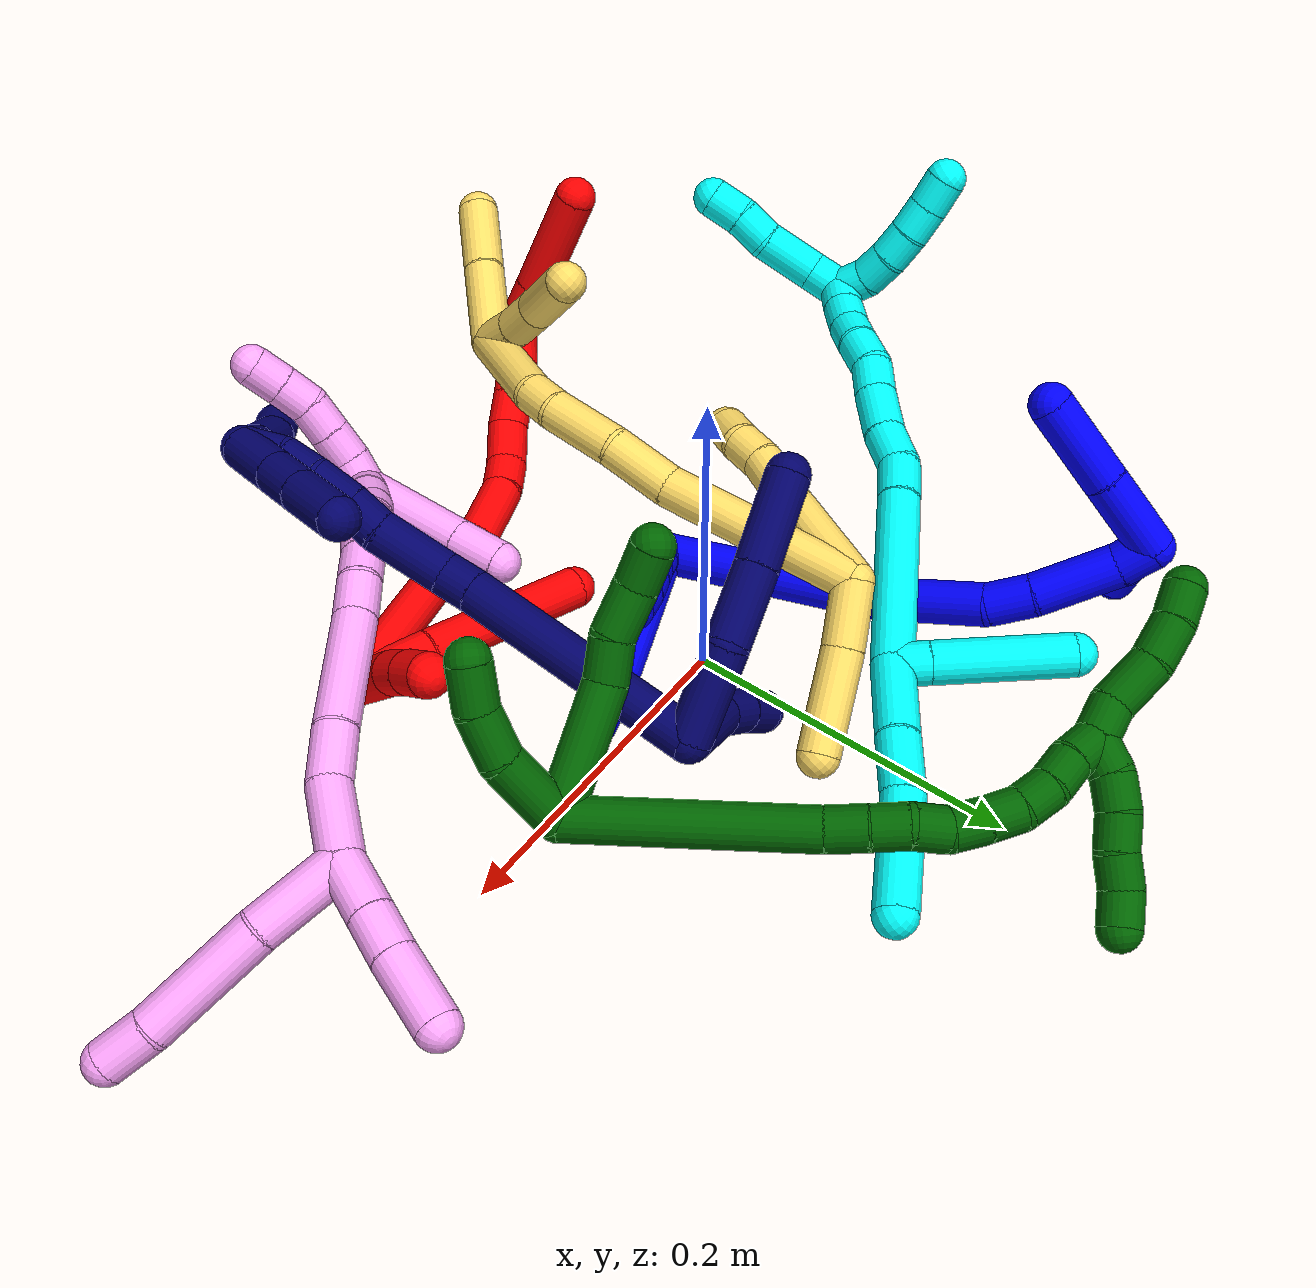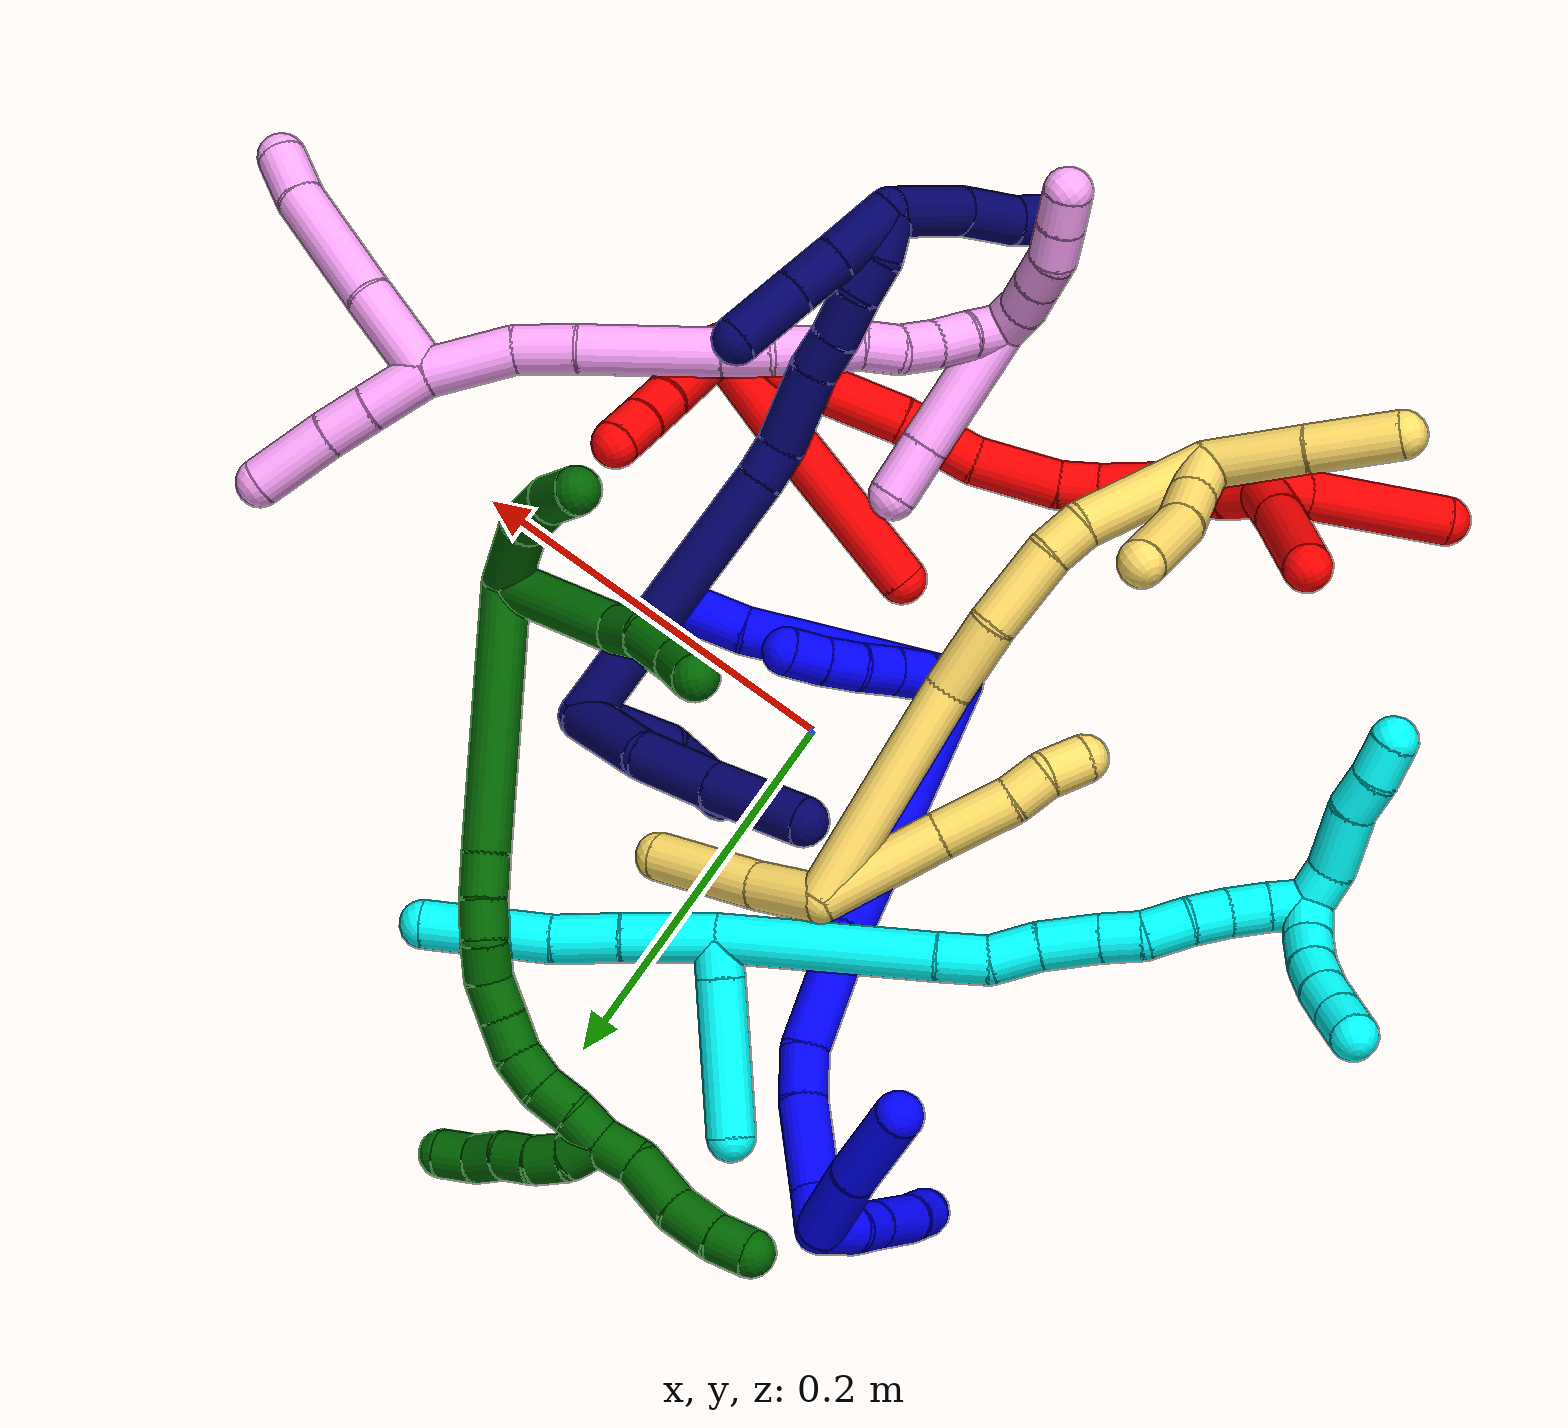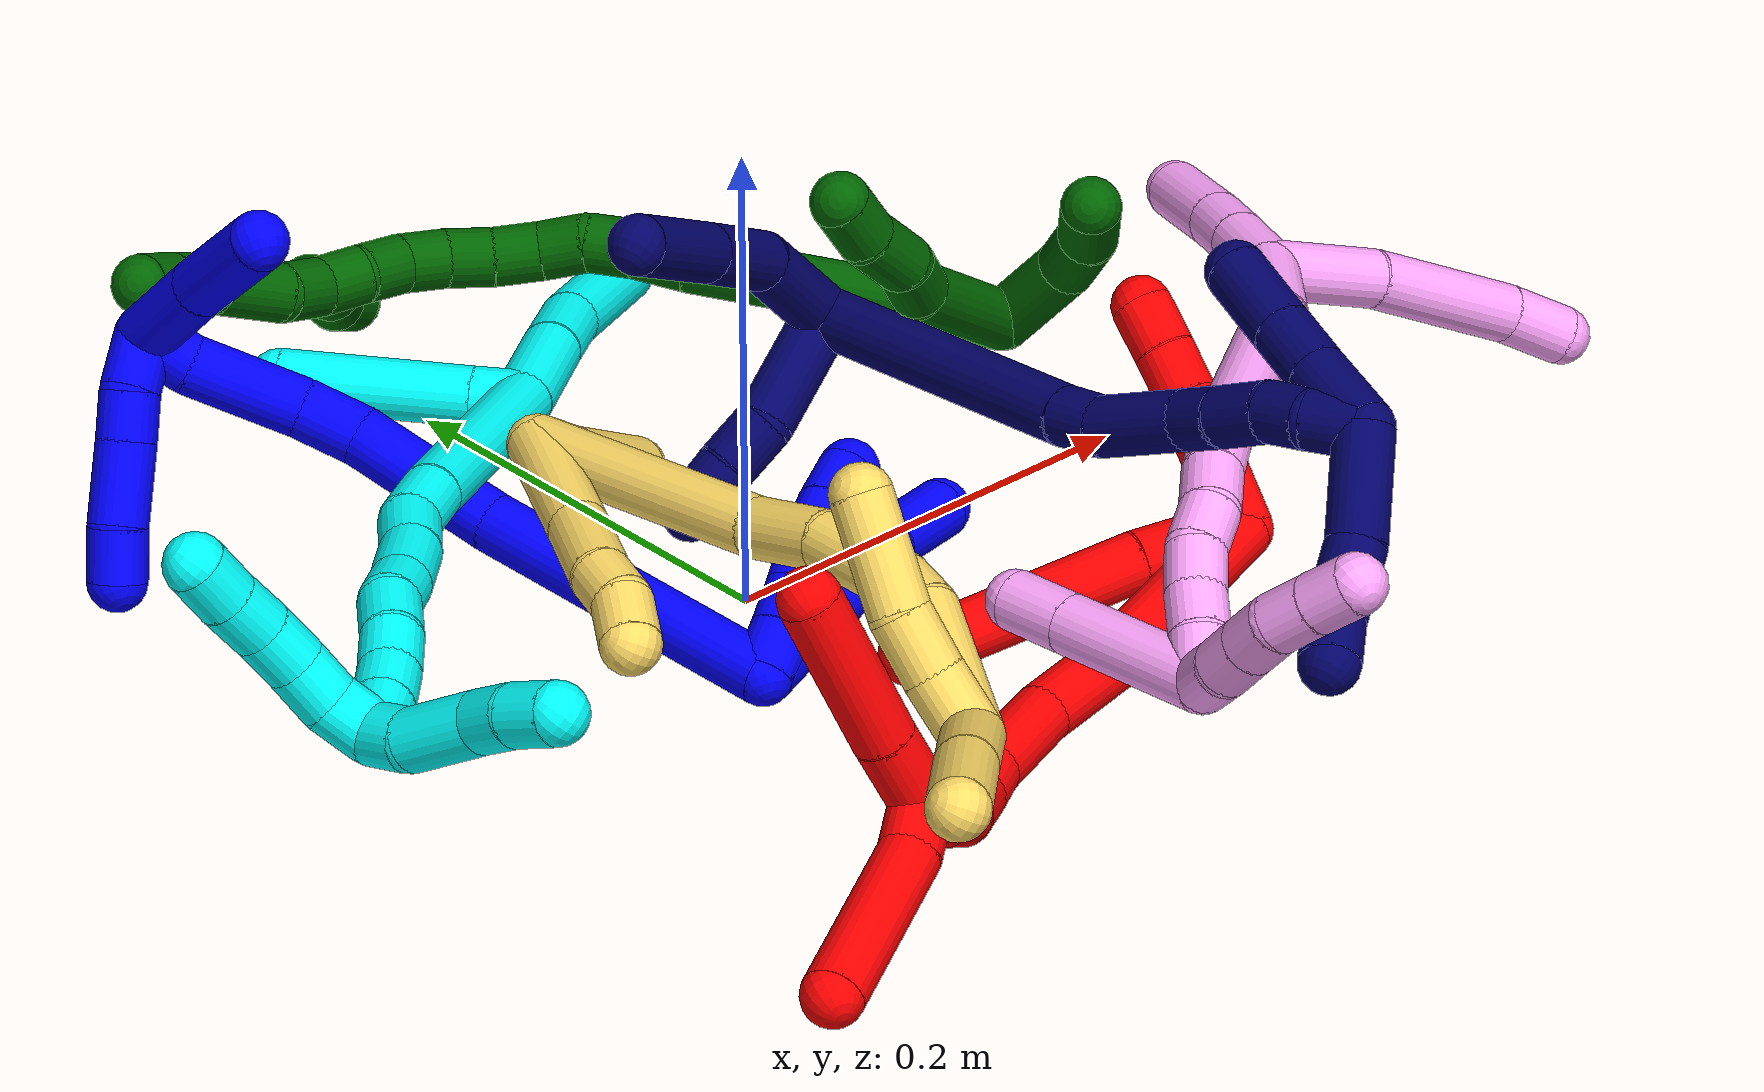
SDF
<sdf version="1.7">
 <world name="default">
  <plugin name="TubeGeneratorPlugin" filename="libtube_generator_plugin.so"/>
  <model name="photoneo_s_sensor">
   <static>1</static>
   <pose>0 0 2 1.57079 1.57079 3.14159</pose>
   <link name="link">
    <inertial><mass>0.1</mass></inertial>
    <sensor name="sensor" type="depth">
     <update_rate>30</update_rate>
     <camera>
      <horizontal_fov>1.22</horizontal_fov>
      <image><width>1920</width><height>1200</height><format>B8G8R8</format></image>
      <clip><near>0.1</near><far>4</far></clip>
      <depth_camera><output>points</output></depth_camera>
     </camera>
     <plugin name="camera_plugin" filename="libgazebo_ros_depth_camera.so">
      <baseline>0.2</baseline>
      <alwaysOn>1</alwaysOn>
      <updateRate>0.0</updateRate>
      <cameraName>camera_ir</cameraName>
      <imageTopicName>/camera/color/image_raw</imageTopicName>
      <cameraInfoTopicName>/camera/color/camera_info</cameraInfoTopicName>
      <depthImageTopicName>/camera/depth/image_raw</depthImageTopicName>
      <depthImageCameraInfoTopicName>/camera/depth/camera_info</depthImageCameraInfoTopicName>
      <pointCloudTopicName>/camera/depth/points</pointCloudTopicName>
      <frameName>fr_optical</frameName>
      <pointCloudCutoff>0.1</pointCloudCutoff>
      <pointCloudCutoffMax>2.0</pointCloudCutoffMax>
      <distortionK1>0</distortionK1>
      <distortionK2>0</distortionK2>
      <distortionK3>0</distortionK3>
      <distortionT1>0</distortionT1>
      <distortionT2>0</distortionT2>
      <CxPrime>0</CxPrime>
      <Cx>0</Cx>
      <Cy>0</Cy>
      <focalLength>0</focalLength>
      <hackBaseline>0</hackBaseline>
     </plugin>
    </sensor>
   </link>
  </model>
  <gravity>0 0 -9.8</gravity>
  <magnetic_field>6e-06 2.3e-05 -4.2e-05</magnetic_field>
  <atmosphere type="adiabatic"/>
  <physics name="default_physics" default="0" type="ode">
   <max_step_size>0.003</max_step_size>
   <real_time_factor>1</real_time_factor>
   <real_time_update_rate>1000</real_time_update_rate>
   <max_contacts>10000</max_contacts>
   <ode>
    <solver>
     <type>quick</type>
     <iters>100</iters>
     <sor>1.3</sor>
     <use_dynamic_moi_rescaling>0</use_dynamic_moi_rescaling>
    </solver>
    <constraints>
     <contact_max_correcting_vel>0</contact_max_correcting_vel>
     <contact_surface_layer>0.001</contact_surface_layer>
     <cfm>0</cfm>
     <erp>0.2</erp>
    </constraints>
   </ode>
  </physics>
  <scene><ambient>0.4 0.4 0.4 1</ambient><background>0.7 0.7 0.7 1</background><shadows>0</shadows></scene>
  <audio><device>default</device></audio>
  <spherical_coordinates>
   <surface_model>EARTH_WGS84</surface_model>
   <latitude_deg>0</latitude_deg>
   <longitude_deg>0</longitude_deg>
   <elevation>0</elevation>
   <heading_deg>0</heading_deg>
  </spherical_coordinates>
  <model name="bin">
   <static>1</static>
   <link name="bottom">
    <collision name="collision-bottom">
     <pose>0 0 -0.01 0 -0 0</pose>
     <geometry><box><size>0.8 0.6 0.02</size></box></geometry>
     <surface>
      <friction><ode><mu>100</mu><mu2>100</mu2></ode></friction>
      <contact><collide_bitmask>65535</collide_bitmask></contact>
     </surface>
    </collision>
   </link>
   <link name="west_wall">
    <collision name="collision-west_wall">
     <pose>-0.41 0 0.1 0 -0 0</pose>
     <geometry><box><size>0.02 0.6 0.2</size></box></geometry>
     <surface>
      <friction><ode><mu>100</mu><mu2>100</mu2></ode></friction>
      <contact><collide_bitmask>65535</collide_bitmask></contact>
     </surface>
    </collision>
   </link>
   <link name="east_wall">
    <collision name="collision-east_wall">
     <pose>0.41 0 0.1 0 -0 0</pose>
     <geometry><box><size>0.02 0.6 0.2</size></box></geometry>
     <surface>
      <friction><ode><mu>100</mu><mu2>100</mu2></ode></friction>
      <contact><collide_bitmask>65535</collide_bitmask></contact>
     </surface>
    </collision>
   </link>
   <link name="south_wall">
    <collision name="collision-south_wall">
     <pose>0 -0.31 0.1 0 -0 0</pose>
     <geometry><box><size>0.8 0.02 0.2</size></box></geometry>
     <surface>
      <friction><ode><mu>100</mu><mu2>100</mu2></ode></friction>
      <contact><collide_bitmask>65535</collide_bitmask></contact>
     </surface>
    </collision>
   </link>
   <link name="north_wall">
    <collision name="collision-north_wall">
     <pose>0 0.31 0.1 0 -0 0</pose>
     <geometry><box><size>0.8 0.02 0.2</size></box></geometry>
     <surface>
      <friction><ode><mu>100</mu><mu2>100</mu2></ode></friction>
      <contact><collide_bitmask>65535</collide_bitmask></contact>
     </surface>
    </collision>
   </link>
  </model>
  <model name="1">
   <static>0</static>
   <link name="1">
    <collision name="collision-cylinder-e_1_2_8">
     <pose>0.043331 0.019047 0.029953 -0.566393 0.884479 -0.273881</pose>
     <geometry><cylinder><radius>0.0125</radius><length>0.112028</length></cylinder></geometry>
     <surface>
      <friction><ode><mu>1.16</mu><mu2>1.16</mu2><slip1>0</slip1><slip2>0</slip2></ode></friction>
      <contact><ode><kp>1e+06</kp><kd>1</kd><max_vel>0</max_vel><min_depth>0.001</min_depth></ode></contact>
     </surface>
    </collision>
    <visual name="visual-cylinder-e_1_2_8">
     <pose>0.043331 0.019047 0.029953 -0.566393 0.884479 -0.273881</pose>
     <geometry><cylinder><radius>0.0125</radius><length>0.112028</length></cylinder></geometry>
     <material><ambient>0 0 1 1</ambient></material>
    </visual>
    <collision name="collision-cylinder-e_2_8_6">
     <pose>0.102914 0.044404 0.067424 -0.698284 1.02742 -0.405192</pose>
     <geometry><cylinder><radius>0.0125</radius><length>0.037972</length></cylinder></geometry>
     <surface>
      <friction><ode><mu>1.16</mu><mu2>1.16</mu2><slip1>0</slip1><slip2>0</slip2></ode></friction>
      <contact><ode><kp>1e+06</kp><kd>1</kd><max_vel>0</max_vel><min_depth>0.001</min_depth></ode></contact>
     </surface>
    </collision>
    <visual name="visual-cylinder-e_2_8_6">
     <pose>0.102914 0.044404 0.067424 -0.698284 1.02742 -0.405192</pose>
     <geometry><cylinder><radius>0.0125</radius><length>0.037972</length></cylinder></geometry>
     <material><ambient>0 0 1 1</ambient></material>
    </visual>
    <collision name="collision-cylinder-e_1_2_9">
     <pose>0.006094 -0.001065 0.007857 0.134735 0.655279 0.045856</pose>
     <geometry><cylinder><radius>0.0125</radius><length>0.02</length></cylinder></geometry>
     <surface>
      <friction><ode><mu>1.16</mu><mu2>1.16</mu2><slip1>0</slip1><slip2>0</slip2></ode></friction>
      <contact><ode><kp>1e+06</kp><kd>1</kd><max_vel>0</max_vel><min_depth>0.001</min_depth></ode></contact>
     </surface>
    </collision>
    <visual name="visual-cylinder-e_1_2_9">
     <pose>0.006094 -0.001065 0.007857 0.134735 0.655279 0.045856</pose>
     <geometry><cylinder><radius>0.0125</radius><length>0.02</length></cylinder></geometry>
     <material><ambient>0 0 1 1</ambient></material>
    </visual>
    <collision name="collision-cylinder-e_2_9_10">
     <pose>0.01809 -0.00271 0.023765 0.071867 0.631391 0.023482</pose>
     <geometry><cylinder><radius>0.0125</radius><length>0.02</length></cylinder></geometry>
     <surface>
      <friction><ode><mu>1.16</mu><mu2>1.16</mu2><slip1>0</slip1><slip2>0</slip2></ode></friction>
      <contact><ode><kp>1e+06</kp><kd>1</kd><max_vel>0</max_vel><min_depth>0.001</min_depth></ode></contact>
     </surface>
    </collision>
    <visual name="visual-cylinder-e_2_9_10">
     <pose>0.01809 -0.00271 0.023765 0.071867 0.631391 0.023482</pose>
     <geometry><cylinder><radius>0.0125</radius><length>0.02</length></cylinder></geometry>
     <material><ambient>0 0 1 1</ambient></material>
    </visual>
    <collision name="collision-cylinder-e_3_10_11">
     <pose>0.0295 -0.0039 0.040141 0.073247 0.583172 0.021993</pose>
     <geometry><cylinder><radius>0.0125</radius><length>0.02</length></cylinder></geometry>
     <surface>
      <friction><ode><mu>1.16</mu><mu2>1.16</mu2><slip1>0</slip1><slip2>0</slip2></ode></friction>
      <contact><ode><kp>1e+06</kp><kd>1</kd><max_vel>0</max_vel><min_depth>0.001</min_depth></ode></contact>
     </surface>
    </collision>
    <visual name="visual-cylinder-e_3_10_11">
     <pose>0.0295 -0.0039 0.040141 0.073247 0.583172 0.021993</pose>
     <geometry><cylinder><radius>0.0125</radius><length>0.02</length></cylinder></geometry>
     <material><ambient>0 0 1 1</ambient></material>
    </visual>
    <collision name="collision-cylinder-e_4_11_12">
     <pose>0.041542 -0.003891 0.05601 -0.082027 0.712235 -0.030527</pose>
     <geometry><cylinder><radius>0.0125</radius><length>0.02</length></cylinder></geometry>
     <surface>
      <friction><ode><mu>1.16</mu><mu2>1.16</mu2><slip1>0</slip1><slip2>0</slip2></ode></friction>
      <contact><ode><kp>1e+06</kp><kd>1</kd><max_vel>0</max_vel><min_depth>0.001</min_depth></ode></contact>
     </surface>
    </collision>
    <visual name="visual-cylinder-e_4_11_12">
     <pose>0.041542 -0.003891 0.05601 -0.082027 0.712235 -0.030527</pose>
     <geometry><cylinder><radius>0.0125</radius><length>0.02</length></cylinder></geometry>
     <material><ambient>0 0 1 1</ambient></material>
    </visual>
    <collision name="collision-cylinder-e_5_12_5">
     <pose>0.055154 -0.003058 0.070615 -0.030165 0.786179 -0.012509</pose>
     <geometry><cylinder><radius>0.0125</radius><length>0.02</length></cylinder></geometry>
     <surface>
      <friction><ode><mu>1.16</mu><mu2>1.16</mu2><slip1>0</slip1><slip2>0</slip2></ode></friction>
      <contact><ode><kp>1e+06</kp><kd>1</kd><max_vel>0</max_vel><min_depth>0.001</min_depth></ode></contact>
     </surface>
    </collision>
    <visual name="visual-cylinder-e_5_12_5">
     <pose>0.055154 -0.003058 0.070615 -0.030165 0.786179 -0.012509</pose>
     <geometry><cylinder><radius>0.0125</radius><length>0.02</length></cylinder></geometry>
     <material><ambient>0 0 1 1</ambient></material>
    </visual>
    <collision name="collision-cylinder-e_1_2_13">
     <pose>-0.032925 0.028428 0.052665 -0.494964 -0.502952 0.129643</pose>
     <geometry><cylinder><radius>0.0125</radius><length>0.136612</length></cylinder></geometry>
     <surface>
      <friction><ode><mu>1.16</mu><mu2>1.16</mu2><slip1>0</slip1><slip2>0</slip2></ode></friction>
      <contact><ode><kp>1e+06</kp><kd>1</kd><max_vel>0</max_vel><min_depth>0.001</min_depth></ode></contact>
     </surface>
    </collision>
    <visual name="visual-cylinder-e_1_2_13">
     <pose>-0.032925 0.028428 0.052665 -0.494964 -0.502952 0.129643</pose>
     <geometry><cylinder><radius>0.0125</radius><length>0.136612</length></cylinder></geometry>
     <material><ambient>0 0 1 1</ambient></material>
    </visual>
    <collision name="collision-cylinder-e_2_13_14">
     <pose>-0.083698 0.065986 0.132351 -0.325879 -0.559155 0.094326</pose>
     <geometry><cylinder><radius>0.0125</radius><length>0.067294</length></cylinder></geometry>
     <surface>
      <friction><ode><mu>1.16</mu><mu2>1.16</mu2><slip1>0</slip1><slip2>0</slip2></ode></friction>
      <contact><ode><kp>1e+06</kp><kd>1</kd><max_vel>0</max_vel><min_depth>0.001</min_depth></ode></contact>
     </surface>
    </collision>
    <visual name="visual-cylinder-e_2_13_14">
     <pose>-0.083698 0.065986 0.132351 -0.325879 -0.559155 0.094326</pose>
     <geometry><cylinder><radius>0.0125</radius><length>0.067294</length></cylinder></geometry>
     <material><ambient>0 0 1 1</ambient></material>
    </visual>
    <collision name="collision-cylinder-e_3_14_15">
     <pose>-0.111416 0.076421 0.168151 -0.147399 -0.838434 0.065782</pose>
     <geometry><cylinder><radius>0.0125</radius><length>0.026544</length></cylinder></geometry>
     <surface>
      <friction><ode><mu>1.16</mu><mu2>1.16</mu2><slip1>0</slip1><slip2>0</slip2></ode></friction>
      <contact><ode><kp>1e+06</kp><kd>1</kd><max_vel>0</max_vel><min_depth>0.001</min_depth></ode></contact>
     </surface>
    </collision>
    <visual name="visual-cylinder-e_3_14_15">
     <pose>-0.111416 0.076421 0.168151 -0.147399 -0.838434 0.065782</pose>
     <geometry><cylinder><radius>0.0125</radius><length>0.026544</length></cylinder></geometry>
     <material><ambient>0 0 1 1</ambient></material>
    </visual>
    <collision name="collision-cylinder-e_4_15_16">
     <pose>-0.141423 0.077911 0.190466 -0.013812 -0.978926 0.007358</pose>
     <geometry><cylinder><radius>0.0125</radius><length>0.048532</length></cylinder></geometry>
     <surface>
      <friction><ode><mu>1.16</mu><mu2>1.16</mu2><slip1>0</slip1><slip2>0</slip2></ode></friction>
      <contact><ode><kp>1e+06</kp><kd>1</kd><max_vel>0</max_vel><min_depth>0.001</min_depth></ode></contact>
     </surface>
    </collision>
    <visual name="visual-cylinder-e_4_15_16">
     <pose>-0.141423 0.077911 0.190466 -0.013812 -0.978926 0.007358</pose>
     <geometry><cylinder><radius>0.0125</radius><length>0.048532</length></cylinder></geometry>
     <material><ambient>0 0 1 1</ambient></material>
    </visual>
    <collision name="collision-cylinder-e_5_16_1">
     <pose>-0.16933 0.076213 0.210823 0.269723 -0.831976 -0.11974</pose>
     <geometry><cylinder><radius>0.0125</radius><length>0.021017</length></cylinder></geometry>
     <surface>
      <friction><ode><mu>1.16</mu><mu2>1.16</mu2><slip1>0</slip1><slip2>0</slip2></ode></friction>
      <contact><ode><kp>1e+06</kp><kd>1</kd><max_vel>0</max_vel><min_depth>0.001</min_depth></ode></contact>
     </surface>
    </collision>
    <visual name="visual-cylinder-e_5_16_1">
     <pose>-0.16933 0.076213 0.210823 0.269723 -0.831976 -0.11974</pose>
     <geometry><cylinder><radius>0.0125</radius><length>0.021017</length></cylinder></geometry>
     <material><ambient>0 0 1 1</ambient></material>
    </visual>
    <collision name="collision-cylinder-e_1_1_17">
     <pose>-0.171383 0.050968 0.216005 1.64085 0.239408 0.256611</pose>
     <geometry><cylinder><radius>0.0125</radius><length>0.048207</length></cylinder></geometry>
     <surface>
      <friction><ode><mu>1.16</mu><mu2>1.16</mu2><slip1>0</slip1><slip2>0</slip2></ode></friction>
      <contact><ode><kp>1e+06</kp><kd>1</kd><max_vel>0</max_vel><min_depth>0.001</min_depth></ode></contact>
     </surface>
    </collision>
    <visual name="visual-cylinder-e_1_1_17">
     <pose>-0.171383 0.050968 0.216005 1.64085 0.239408 0.256611</pose>
     <geometry><cylinder><radius>0.0125</radius><length>0.048207</length></cylinder></geometry>
     <material><ambient>0 0 1 1</ambient></material>
    </visual>
    <collision name="collision-cylinder-e_2_17_4">
     <pose>-0.160511 0.002469 0.210906 1.70758 0.200449 0.229687</pose>
     <geometry><cylinder><radius>0.0125</radius><length>0.051793</length></cylinder></geometry>
     <surface>
      <friction><ode><mu>1.16</mu><mu2>1.16</mu2><slip1>0</slip1><slip2>0</slip2></ode></friction>
      <contact><ode><kp>1e+06</kp><kd>1</kd><max_vel>0</max_vel><min_depth>0.001</min_depth></ode></contact>
     </surface>
    </collision>
    <visual name="visual-cylinder-e_2_17_4">
     <pose>-0.160511 0.002469 0.210906 1.70758 0.200449 0.229687</pose>
     <geometry><cylinder><radius>0.0125</radius><length>0.051793</length></cylinder></geometry>
     <material><ambient>0 0 1 1</ambient></material>
    </visual>
    <collision name="collision-cylinder-e_1_1_18">
     <pose>-0.18237 0.077592 0.20765 -2.82584 -0.464749 1.95722</pose>
     <geometry><cylinder><radius>0.0125</radius><length>0.023523</length></cylinder></geometry>
     <surface>
      <friction><ode><mu>1.16</mu><mu2>1.16</mu2><slip1>0</slip1><slip2>0</slip2></ode></friction>
      <contact><ode><kp>1e+06</kp><kd>1</kd><max_vel>0</max_vel><min_depth>0.001</min_depth></ode></contact>
     </surface>
    </collision>
    <visual name="visual-cylinder-e_1_1_18">
     <pose>-0.18237 0.077592 0.20765 -2.82584 -0.464749 1.95722</pose>
     <geometry><cylinder><radius>0.0125</radius><length>0.023523</length></cylinder></geometry>
     <material><ambient>0 0 1 1</ambient></material>
    </visual>
    <collision name="collision-cylinder-e_2_18_19">
     <pose>-0.189972 0.085278 0.188866 -2.6755 -0.232569 0.914669</pose>
     <geometry><cylinder><radius>0.0125</radius><length>0.020222</length></cylinder></geometry>
     <surface>
      <friction><ode><mu>1.16</mu><mu2>1.16</mu2><slip1>0</slip1><slip2>0</slip2></ode></friction>
      <contact><ode><kp>1e+06</kp><kd>1</kd><max_vel>0</max_vel><min_depth>0.001</min_depth></ode></contact>
     </surface>
    </collision>
    <visual name="visual-cylinder-e_2_18_19">
     <pose>-0.189972 0.085278 0.188866 -2.6755 -0.232569 0.914669</pose>
     <geometry><cylinder><radius>0.0125</radius><length>0.020222</length></cylinder></geometry>
     <material><ambient>0 0 1 1</ambient></material>
    </visual>
    <collision name="collision-cylinder-e_3_19_20">
     <pose>-0.196754 0.096859 0.165313 -2.69006 -0.264895 1.05125</pose>
     <geometry><cylinder><radius>0.0125</radius><length>0.034002</length></cylinder></geometry>
     <surface>
      <friction><ode><mu>1.16</mu><mu2>1.16</mu2><slip1>0</slip1><slip2>0</slip2></ode></friction>
      <contact><ode><kp>1e+06</kp><kd>1</kd><max_vel>0</max_vel><min_depth>0.001</min_depth></ode></contact>
     </surface>
    </collision>
    <visual name="visual-cylinder-e_3_19_20">
     <pose>-0.196754 0.096859 0.165313 -2.69006 -0.264895 1.05125</pose>
     <geometry><cylinder><radius>0.0125</radius><length>0.034002</length></cylinder></geometry>
     <material><ambient>0 0 1 1</ambient></material>
    </visual>
    <collision name="collision-cylinder-e_4_20_3">
     <pose>-0.202623 0.110004 0.141278 -2.56832 -0.127812 0.42758</pose>
     <geometry><cylinder><radius>0.0125</radius><length>0.022252</length></cylinder></geometry>
     <surface>
      <friction><ode><mu>1.16</mu><mu2>1.16</mu2><slip1>0</slip1><slip2>0</slip2></ode></friction>
      <contact><ode><kp>1e+06</kp><kd>1</kd><max_vel>0</max_vel><min_depth>0.001</min_depth></ode></contact>
     </surface>
    </collision>
    <visual name="visual-cylinder-e_4_20_3">
     <pose>-0.202623 0.110004 0.141278 -2.56832 -0.127812 0.42758</pose>
     <geometry><cylinder><radius>0.0125</radius><length>0.022252</length></cylinder></geometry>
     <material><ambient>0 0 1 1</ambient></material>
    </visual>
    <collision name="collision-sphere-3">
     <pose>-0.204041 0.11599 0.132007 0 -0 0</pose>
     <geometry><sphere><radius>0.0125</radius></sphere></geometry>
     <surface>
      <friction><ode><mu>1.16</mu><mu2>1.16</mu2><slip1>0</slip1><slip2>0</slip2></ode></friction>
      <contact><ode><kp>1e+06</kp><kd>1</kd><max_vel>0</max_vel><min_depth>0.001</min_depth></ode></contact>
     </surface>
    </collision>
    <visual name="visual-sphere-3">
     <pose>-0.204041 0.11599 0.132007 0 -0 0</pose>
     <geometry><sphere><radius>0.0125</radius></sphere></geometry>
     <material><ambient>0 0 1 1</ambient></material>
    </visual>
    <collision name="collision-sphere-20">
     <pose>-0.201205 0.104019 0.150549 0 -0 0</pose>
     <geometry><sphere><radius>0.0125</radius></sphere></geometry>
     <surface>
      <friction><ode><mu>1.16</mu><mu2>1.16</mu2><slip1>0</slip1><slip2>0</slip2></ode></friction>
      <contact><ode><kp>1e+06</kp><kd>1</kd><max_vel>0</max_vel><min_depth>0.001</min_depth></ode></contact>
     </surface>
    </collision>
    <visual name="visual-sphere-20">
     <pose>-0.201205 0.104019 0.150549 0 -0 0</pose>
     <geometry><sphere><radius>0.0125</radius></sphere></geometry>
     <material><ambient>0 0 1 1</ambient></material>
    </visual>
    <collision name="collision-sphere-19">
     <pose>-0.192303 0.0897 0.180077 0 -0 0</pose>
     <geometry><sphere><radius>0.0125</radius></sphere></geometry>
     <surface>
      <friction><ode><mu>1.16</mu><mu2>1.16</mu2><slip1>0</slip1><slip2>0</slip2></ode></friction>
      <contact><ode><kp>1e+06</kp><kd>1</kd><max_vel>0</max_vel><min_depth>0.001</min_depth></ode></contact>
     </surface>
    </collision>
    <visual name="visual-sphere-19">
     <pose>-0.192303 0.0897 0.180077 0 -0 0</pose>
     <geometry><sphere><radius>0.0125</radius></sphere></geometry>
     <material><ambient>0 0 1 1</ambient></material>
    </visual>
    <collision name="collision-sphere-11">
     <pose>0.035006 -0.004511 0.048466 0 -0 0</pose>
     <geometry><sphere><radius>0.0125</radius></sphere></geometry>
     <surface>
      <friction><ode><mu>1.16</mu><mu2>1.16</mu2><slip1>0</slip1><slip2>0</slip2></ode></friction>
      <contact><ode><kp>1e+06</kp><kd>1</kd><max_vel>0</max_vel><min_depth>0.001</min_depth></ode></contact>
     </surface>
    </collision>
    <visual name="visual-sphere-11">
     <pose>0.035006 -0.004511 0.048466 0 -0 0</pose>
     <geometry><sphere><radius>0.0125</radius></sphere></geometry>
     <material><ambient>0 0 1 1</ambient></material>
    </visual>
    <collision name="collision-sphere-10">
     <pose>0.023993 -0.003289 0.031816 0 -0 0</pose>
     <geometry><sphere><radius>0.0125</radius></sphere></geometry>
     <surface>
      <friction><ode><mu>1.16</mu><mu2>1.16</mu2><slip1>0</slip1><slip2>0</slip2></ode></friction>
      <contact><ode><kp>1e+06</kp><kd>1</kd><max_vel>0</max_vel><min_depth>0.001</min_depth></ode></contact>
     </surface>
    </collision>
    <visual name="visual-sphere-10">
     <pose>0.023993 -0.003289 0.031816 0 -0 0</pose>
     <geometry><sphere><radius>0.0125</radius></sphere></geometry>
     <material><ambient>0 0 1 1</ambient></material>
    </visual>
    <collision name="collision-sphere-6">
     <pose>0.119166 0.050715 0.074943 0 -0 0</pose>
     <geometry><sphere><radius>0.0125</radius></sphere></geometry>
     <surface>
      <friction><ode><mu>1.16</mu><mu2>1.16</mu2><slip1>0</slip1><slip2>0</slip2></ode></friction>
      <contact><ode><kp>1e+06</kp><kd>1</kd><max_vel>0</max_vel><min_depth>0.001</min_depth></ode></contact>
     </surface>
    </collision>
    <visual name="visual-sphere-6">
     <pose>0.119166 0.050715 0.074943 0 -0 0</pose>
     <geometry><sphere><radius>0.0125</radius></sphere></geometry>
     <material><ambient>0 0 1 1</ambient></material>
    </visual>
    <collision name="collision-sphere-9">
     <pose>0.012188 -0.00213 0.015714 0 -0 0</pose>
     <geometry><sphere><radius>0.0125</radius></sphere></geometry>
     <surface>
      <friction><ode><mu>1.16</mu><mu2>1.16</mu2><slip1>0</slip1><slip2>0</slip2></ode></friction>
      <contact><ode><kp>1e+06</kp><kd>1</kd><max_vel>0</max_vel><min_depth>0.001</min_depth></ode></contact>
     </surface>
    </collision>
    <visual name="visual-sphere-9">
     <pose>0.012188 -0.00213 0.015714 0 -0 0</pose>
     <geometry><sphere><radius>0.0125</radius></sphere></geometry>
     <material><ambient>0 0 1 1</ambient></material>
    </visual>
    <collision name="collision-sphere-2">
     <geometry><sphere><radius>0.0125</radius></sphere></geometry>
     <surface>
      <friction><ode><mu>1.16</mu><mu2>1.16</mu2><slip1>0</slip1><slip2>0</slip2></ode></friction>
      <contact><ode><kp>1e+06</kp><kd>1</kd><max_vel>0</max_vel><min_depth>0.001</min_depth></ode></contact>
     </surface>
    </collision>
    <visual name="visual-sphere-2">
     <geometry><sphere><radius>0.0125</radius></sphere></geometry>
     <material><ambient>0 0 1 1</ambient></material>
    </visual>
    <collision name="collision-sphere-8">
     <pose>0.086663 0.038093 0.059905 0 -0 0</pose>
     <geometry><sphere><radius>0.0125</radius></sphere></geometry>
     <surface>
      <friction><ode><mu>1.16</mu><mu2>1.16</mu2><slip1>0</slip1><slip2>0</slip2></ode></friction>
      <contact><ode><kp>1e+06</kp><kd>1</kd><max_vel>0</max_vel><min_depth>0.001</min_depth></ode></contact>
     </surface>
    </collision>
    <visual name="visual-sphere-8">
     <pose>0.086663 0.038093 0.059905 0 -0 0</pose>
     <geometry><sphere><radius>0.0125</radius></sphere></geometry>
     <material><ambient>0 0 1 1</ambient></material>
    </visual>
    <collision name="collision-sphere-12">
     <pose>0.048077 -0.003271 0.063553 0 -0 0</pose>
     <geometry><sphere><radius>0.0125</radius></sphere></geometry>
     <surface>
      <friction><ode><mu>1.16</mu><mu2>1.16</mu2><slip1>0</slip1><slip2>0</slip2></ode></friction>
      <contact><ode><kp>1e+06</kp><kd>1</kd><max_vel>0</max_vel><min_depth>0.001</min_depth></ode></contact>
     </surface>
    </collision>
    <visual name="visual-sphere-12">
     <pose>0.048077 -0.003271 0.063553 0 -0 0</pose>
     <geometry><sphere><radius>0.0125</radius></sphere></geometry>
     <material><ambient>0 0 1 1</ambient></material>
    </visual>
    <collision name="collision-sphere-5">
     <pose>0.06223 -0.002845 0.077678 0 -0 0</pose>
     <geometry><sphere><radius>0.0125</radius></sphere></geometry>
     <surface>
      <friction><ode><mu>1.16</mu><mu2>1.16</mu2><slip1>0</slip1><slip2>0</slip2></ode></friction>
      <contact><ode><kp>1e+06</kp><kd>1</kd><max_vel>0</max_vel><min_depth>0.001</min_depth></ode></contact>
     </surface>
    </collision>
    <visual name="visual-sphere-5">
     <pose>0.06223 -0.002845 0.077678 0 -0 0</pose>
     <geometry><sphere><radius>0.0125</radius></sphere></geometry>
     <material><ambient>0 0 1 1</ambient></material>
    </visual>
    <collision name="collision-sphere-13">
     <pose>-0.065849 0.056855 0.10533 0 -0 0</pose>
     <geometry><sphere><radius>0.0125</radius></sphere></geometry>
     <surface>
      <friction><ode><mu>1.16</mu><mu2>1.16</mu2><slip1>0</slip1><slip2>0</slip2></ode></friction>
      <contact><ode><kp>1e+06</kp><kd>1</kd><max_vel>0</max_vel><min_depth>0.001</min_depth></ode></contact>
     </surface>
    </collision>
    <visual name="visual-sphere-13">
     <pose>-0.065849 0.056855 0.10533 0 -0 0</pose>
     <geometry><sphere><radius>0.0125</radius></sphere></geometry>
     <material><ambient>0 0 1 1</ambient></material>
    </visual>
    <collision name="collision-sphere-14">
     <pose>-0.101547 0.075118 0.159373 0 -0 0</pose>
     <geometry><sphere><radius>0.0125</radius></sphere></geometry>
     <surface>
      <friction><ode><mu>1.16</mu><mu2>1.16</mu2><slip1>0</slip1><slip2>0</slip2></ode></friction>
      <contact><ode><kp>1e+06</kp><kd>1</kd><max_vel>0</max_vel><min_depth>0.001</min_depth></ode></contact>
     </surface>
    </collision>
    <visual name="visual-sphere-14">
     <pose>-0.101547 0.075118 0.159373 0 -0 0</pose>
     <geometry><sphere><radius>0.0125</radius></sphere></geometry>
     <material><ambient>0 0 1 1</ambient></material>
    </visual>
    <collision name="collision-sphere-15">
     <pose>-0.121285 0.077724 0.176928 0 -0 0</pose>
     <geometry><sphere><radius>0.0125</radius></sphere></geometry>
     <surface>
      <friction><ode><mu>1.16</mu><mu2>1.16</mu2><slip1>0</slip1><slip2>0</slip2></ode></friction>
      <contact><ode><kp>1e+06</kp><kd>1</kd><max_vel>0</max_vel><min_depth>0.001</min_depth></ode></contact>
     </surface>
    </collision>
    <visual name="visual-sphere-15">
     <pose>-0.121285 0.077724 0.176928 0 -0 0</pose>
     <geometry><sphere><radius>0.0125</radius></sphere></geometry>
     <material><ambient>0 0 1 1</ambient></material>
    </visual>
    <collision name="collision-sphere-16">
     <pose>-0.161561 0.078098 0.204003 0 -0 0</pose>
     <geometry><sphere><radius>0.0125</radius></sphere></geometry>
     <surface>
      <friction><ode><mu>1.16</mu><mu2>1.16</mu2><slip1>0</slip1><slip2>0</slip2></ode></friction>
      <contact><ode><kp>1e+06</kp><kd>1</kd><max_vel>0</max_vel><min_depth>0.001</min_depth></ode></contact>
     </surface>
    </collision>
    <visual name="visual-sphere-16">
     <pose>-0.161561 0.078098 0.204003 0 -0 0</pose>
     <geometry><sphere><radius>0.0125</radius></sphere></geometry>
     <material><ambient>0 0 1 1</ambient></material>
    </visual>
    <collision name="collision-sphere-1">
     <pose>-0.177099 0.074327 0.217644 0 -0 0</pose>
     <geometry><sphere><radius>0.0125</radius></sphere></geometry>
     <surface>
      <friction><ode><mu>1.16</mu><mu2>1.16</mu2><slip1>0</slip1><slip2>0</slip2></ode></friction>
      <contact><ode><kp>1e+06</kp><kd>1</kd><max_vel>0</max_vel><min_depth>0.001</min_depth></ode></contact>
     </surface>
    </collision>
    <visual name="visual-sphere-1">
     <pose>-0.177099 0.074327 0.217644 0 -0 0</pose>
     <geometry><sphere><radius>0.0125</radius></sphere></geometry>
     <material><ambient>0 0 1 1</ambient></material>
    </visual>
    <collision name="collision-sphere-18">
     <pose>-0.187642 0.080857 0.197656 0 -0 0</pose>
     <geometry><sphere><radius>0.0125</radius></sphere></geometry>
     <surface>
      <friction><ode><mu>1.16</mu><mu2>1.16</mu2><slip1>0</slip1><slip2>0</slip2></ode></friction>
      <contact><ode><kp>1e+06</kp><kd>1</kd><max_vel>0</max_vel><min_depth>0.001</min_depth></ode></contact>
     </surface>
    </collision>
    <visual name="visual-sphere-18">
     <pose>-0.187642 0.080857 0.197656 0 -0 0</pose>
     <geometry><sphere><radius>0.0125</radius></sphere></geometry>
     <material><ambient>0 0 1 1</ambient></material>
    </visual>
    <collision name="collision-sphere-17">
     <pose>-0.165668 0.02761 0.214366 0 -0 0</pose>
     <geometry><sphere><radius>0.0125</radius></sphere></geometry>
     <surface>
      <friction><ode><mu>1.16</mu><mu2>1.16</mu2><slip1>0</slip1><slip2>0</slip2></ode></friction>
      <contact><ode><kp>1e+06</kp><kd>1</kd><max_vel>0</max_vel><min_depth>0.001</min_depth></ode></contact>
     </surface>
    </collision>
    <visual name="visual-sphere-17">
     <pose>-0.165668 0.02761 0.214366 0 -0 0</pose>
     <geometry><sphere><radius>0.0125</radius></sphere></geometry>
     <material><ambient>0 0 1 1</ambient></material>
    </visual>
    <collision name="collision-sphere-4">
     <pose>-0.155355 -0.022672 0.207446 0 -0 0</pose>
     <geometry><sphere><radius>0.0125</radius></sphere></geometry>
     <surface>
      <friction><ode><mu>1.16</mu><mu2>1.16</mu2><slip1>0</slip1><slip2>0</slip2></ode></friction>
      <contact><ode><kp>1e+06</kp><kd>1</kd><max_vel>0</max_vel><min_depth>0.001</min_depth></ode></contact>
     </surface>
    </collision>
    <visual name="visual-sphere-4">
     <pose>-0.155355 -0.022672 0.207446 0 -0 0</pose>
     <geometry><sphere><radius>0.0125</radius></sphere></geometry>
     <material><ambient>0 0 1 1</ambient></material>
    </visual>
    <inertial>
     <pose>-0.063528 0.041518 0.11057 0 -0 0</pose>
     <mass>0.75</mass>
     <inertia>
      <ixx>0.00035</ixx>
      <ixy>0</ixy>
      <ixz>0</ixz>
      <iyy>0.000384</iyy>
      <iyz>0</iyz>
      <izz>-7.4e-05</izz>
     </inertia>
    </inertial>
   </link>
   <pose>-0.046306 -0.062907 0.0123 -0.915555 0.052481 -0.304359</pose>
  </model>
  <model name="2">
   <static>0</static>
   <link name="2">
    <collision name="collision-cylinder-e_1_2_8">
     <pose>-0.009316 -0.021655 0.001677 1.49352 -0.405169 -0.37574</pose>
     <geometry><cylinder><radius>0.0125</radius><length>0.047266</length></cylinder></geometry>
     <surface>
      <friction><ode><mu>1.16</mu><mu2>1.16</mu2><slip1>0</slip1><slip2>0</slip2></ode></friction>
      <contact><ode><kp>1e+06</kp><kd>1</kd><max_vel>0</max_vel><min_depth>0.001</min_depth></ode></contact>
     </surface>
    </collision>
    <visual name="visual-cylinder-e_1_2_8">
     <pose>-0.009316 -0.021655 0.001677 1.49352 -0.405169 -0.37574</pose>
     <geometry><cylinder><radius>0.0125</radius><length>0.047266</length></cylinder></geometry>
     <material><ambient>1 0 0 1</ambient></material>
    </visual>
    <collision name="collision-cylinder-e_2_8_6">
     <pose>-0.035655 -0.091259 0.010397 1.42494 -0.337812 -0.292518</pose>
     <geometry><cylinder><radius>0.0125</radius><length>0.102734</length></cylinder></geometry>
     <surface>
      <friction><ode><mu>1.16</mu><mu2>1.16</mu2><slip1>0</slip1><slip2>0</slip2></ode></friction>
      <contact><ode><kp>1e+06</kp><kd>1</kd><max_vel>0</max_vel><min_depth>0.001</min_depth></ode></contact>
     </surface>
    </collision>
    <visual name="visual-cylinder-e_2_8_6">
     <pose>-0.035655 -0.091259 0.010397 1.42494 -0.337812 -0.292518</pose>
     <geometry><cylinder><radius>0.0125</radius><length>0.102734</length></cylinder></geometry>
     <material><ambient>1 0 0 1</ambient></material>
    </visual>
    <collision name="collision-cylinder-e_1_2_9">
     <pose>-0.014498 0.002185 -0.024985 -3.05435 -0.524136 2.81898</pose>
     <geometry><cylinder><radius>0.0125</radius><length>0.057938</length></cylinder></geometry>
     <surface>
      <friction><ode><mu>1.16</mu><mu2>1.16</mu2><slip1>0</slip1><slip2>0</slip2></ode></friction>
      <contact><ode><kp>1e+06</kp><kd>1</kd><max_vel>0</max_vel><min_depth>0.001</min_depth></ode></contact>
     </surface>
    </collision>
    <visual name="visual-cylinder-e_1_2_9">
     <pose>-0.014498 0.002185 -0.024985 -3.05435 -0.524136 2.81898</pose>
     <geometry><cylinder><radius>0.0125</radius><length>0.057938</length></cylinder></geometry>
     <material><ambient>1 0 0 1</ambient></material>
    </visual>
    <collision name="collision-cylinder-e_2_9_10">
     <pose>-0.033146 0.004626 -0.059387 -3.1145 -0.414976 3.01305</pose>
     <geometry><cylinder><radius>0.0125</radius><length>0.020588</length></cylinder></geometry>
     <surface>
      <friction><ode><mu>1.16</mu><mu2>1.16</mu2><slip1>0</slip1><slip2>0</slip2></ode></friction>
      <contact><ode><kp>1e+06</kp><kd>1</kd><max_vel>0</max_vel><min_depth>0.001</min_depth></ode></contact>
     </surface>
    </collision>
    <visual name="visual-cylinder-e_2_9_10">
     <pose>-0.033146 0.004626 -0.059387 -3.1145 -0.414976 3.01305</pose>
     <geometry><cylinder><radius>0.0125</radius><length>0.020588</length></cylinder></geometry>
     <material><ambient>1 0 0 1</ambient></material>
    </visual>
    <collision name="collision-cylinder-e_3_10_5">
     <pose>-0.040941 0.004908 -0.078903 -3.13894 -0.346272 3.12645</pose>
     <geometry><cylinder><radius>0.0125</radius><length>0.021473</length></cylinder></geometry>
     <surface>
      <friction><ode><mu>1.16</mu><mu2>1.16</mu2><slip1>0</slip1><slip2>0</slip2></ode></friction>
      <contact><ode><kp>1e+06</kp><kd>1</kd><max_vel>0</max_vel><min_depth>0.001</min_depth></ode></contact>
     </surface>
    </collision>
    <visual name="visual-cylinder-e_3_10_5">
     <pose>-0.040941 0.004908 -0.078903 -3.13894 -0.346272 3.12645</pose>
     <geometry><cylinder><radius>0.0125</radius><length>0.021473</length></cylinder></geometry>
     <material><ambient>1 0 0 1</ambient></material>
    </visual>
    <collision name="collision-cylinder-e_1_2_11">
     <pose>-0.020715 -0.03466 0.028487 0.882839 -0.432568 -0.206902</pose>
     <geometry><cylinder><radius>0.0125</radius><length>0.098832</length></cylinder></geometry>
     <surface>
      <friction><ode><mu>1.16</mu><mu2>1.16</mu2><slip1>0</slip1><slip2>0</slip2></ode></friction>
      <contact><ode><kp>1e+06</kp><kd>1</kd><max_vel>0</max_vel><min_depth>0.001</min_depth></ode></contact>
     </surface>
    </collision>
    <visual name="visual-cylinder-e_1_2_11">
     <pose>-0.020715 -0.03466 0.028487 0.882839 -0.432568 -0.206902</pose>
     <geometry><cylinder><radius>0.0125</radius><length>0.098832</length></cylinder></geometry>
     <material><ambient>1 0 0 1</ambient></material>
    </visual>
    <collision name="collision-cylinder-e_2_11_12">
     <pose>-0.050615 -0.085567 0.066901 1.02234 -0.449422 -0.255017</pose>
     <geometry><cylinder><radius>0.0125</radius><length>0.042279</length></cylinder></geometry>
     <surface>
      <friction><ode><mu>1.16</mu><mu2>1.16</mu2><slip1>0</slip1><slip2>0</slip2></ode></friction>
      <contact><ode><kp>1e+06</kp><kd>1</kd><max_vel>0</max_vel><min_depth>0.001</min_depth></ode></contact>
     </surface>
    </collision>
    <visual name="visual-cylinder-e_2_11_12">
     <pose>-0.050615 -0.085567 0.066901 1.02234 -0.449422 -0.255017</pose>
     <geometry><cylinder><radius>0.0125</radius><length>0.042279</length></cylinder></geometry>
     <material><ambient>1 0 0 1</ambient></material>
    </visual>
    <collision name="collision-cylinder-e_3_12_13">
     <pose>-0.071164 -0.115185 0.090566 0.771848 -0.535162 -0.221863</pose>
     <geometry><cylinder><radius>0.0125</radius><length>0.044572</length></cylinder></geometry>
     <surface>
      <friction><ode><mu>1.16</mu><mu2>1.16</mu2><slip1>0</slip1><slip2>0</slip2></ode></friction>
      <contact><ode><kp>1e+06</kp><kd>1</kd><max_vel>0</max_vel><min_depth>0.001</min_depth></ode></contact>
     </surface>
    </collision>
    <visual name="visual-cylinder-e_3_12_13">
     <pose>-0.071164 -0.115185 0.090566 0.771848 -0.535162 -0.221863</pose>
     <geometry><cylinder><radius>0.0125</radius><length>0.044572</length></cylinder></geometry>
     <material><ambient>1 0 0 1</ambient></material>
    </visual>
    <collision name="collision-cylinder-e_4_13_14">
     <pose>-0.088332 -0.132981 0.112201 0.510751 -0.569981 -0.152675</pose>
     <geometry><cylinder><radius>0.0125</radius><length>0.021504</length></cylinder></geometry>
     <surface>
      <friction><ode><mu>1.16</mu><mu2>1.16</mu2><slip1>0</slip1><slip2>0</slip2></ode></friction>
      <contact><ode><kp>1e+06</kp><kd>1</kd><max_vel>0</max_vel><min_depth>0.001</min_depth></ode></contact>
     </surface>
    </collision>
    <visual name="visual-cylinder-e_4_13_14">
     <pose>-0.088332 -0.132981 0.112201 0.510751 -0.569981 -0.152675</pose>
     <geometry><cylinder><radius>0.0125</radius><length>0.021504</length></cylinder></geometry>
     <material><ambient>1 0 0 1</ambient></material>
    </visual>
    <collision name="collision-cylinder-e_5_14_15">
     <pose>-0.10394 -0.140599 0.129411 0.330303 -0.783449 -0.137476</pose>
     <geometry><cylinder><radius>0.0125</radius><length>0.027791</length></cylinder></geometry>
     <surface>
      <friction><ode><mu>1.16</mu><mu2>1.16</mu2><slip1>0</slip1><slip2>0</slip2></ode></friction>
      <contact><ode><kp>1e+06</kp><kd>1</kd><max_vel>0</max_vel><min_depth>0.001</min_depth></ode></contact>
     </surface>
    </collision>
    <visual name="visual-cylinder-e_5_14_15">
     <pose>-0.10394 -0.140599 0.129411 0.330303 -0.783449 -0.137476</pose>
     <geometry><cylinder><radius>0.0125</radius><length>0.027791</length></cylinder></geometry>
     <material><ambient>1 0 0 1</ambient></material>
    </visual>
    <collision name="collision-cylinder-e_6_15_16">
     <pose>-0.123175 -0.146205 0.143381 0.478094 -1.06309 -0.28466</pose>
     <geometry><cylinder><radius>0.0125</radius><length>0.02158</length></cylinder></geometry>
     <surface>
      <friction><ode><mu>1.16</mu><mu2>1.16</mu2><slip1>0</slip1><slip2>0</slip2></ode></friction>
      <contact><ode><kp>1e+06</kp><kd>1</kd><max_vel>0</max_vel><min_depth>0.001</min_depth></ode></contact>
     </surface>
    </collision>
    <visual name="visual-cylinder-e_6_15_16">
     <pose>-0.123175 -0.146205 0.143381 0.478094 -1.06309 -0.28466</pose>
     <geometry><cylinder><radius>0.0125</radius><length>0.02158</length></cylinder></geometry>
     <material><ambient>1 0 0 1</ambient></material>
    </visual>
    <collision name="collision-cylinder-e_7_16_17">
     <pose>-0.141754 -0.150339 0.152226 0.389889 -1.11134 -0.243991</pose>
     <geometry><cylinder><radius>0.0125</radius><length>0.020415</length></cylinder></geometry>
     <surface>
      <friction><ode><mu>1.16</mu><mu2>1.16</mu2><slip1>0</slip1><slip2>0</slip2></ode></friction>
      <contact><ode><kp>1e+06</kp><kd>1</kd><max_vel>0</max_vel><min_depth>0.001</min_depth></ode></contact>
     </surface>
    </collision>
    <visual name="visual-cylinder-e_7_16_17">
     <pose>-0.141754 -0.150339 0.152226 0.389889 -1.11134 -0.243991</pose>
     <geometry><cylinder><radius>0.0125</radius><length>0.020415</length></cylinder></geometry>
     <material><ambient>1 0 0 1</ambient></material>
    </visual>
    <collision name="collision-cylinder-e_8_17_1">
     <pose>-0.161554 -0.151682 0.160767 -0.086677 -1.18141 0.058144</pose>
     <geometry><cylinder><radius>0.0125</radius><length>0.023026</length></cylinder></geometry>
     <surface>
      <friction><ode><mu>1.16</mu><mu2>1.16</mu2><slip1>0</slip1><slip2>0</slip2></ode></friction>
      <contact><ode><kp>1e+06</kp><kd>1</kd><max_vel>0</max_vel><min_depth>0.001</min_depth></ode></contact>
     </surface>
    </collision>
    <visual name="visual-cylinder-e_8_17_1">
     <pose>-0.161554 -0.151682 0.160767 -0.086677 -1.18141 0.058144</pose>
     <geometry><cylinder><radius>0.0125</radius><length>0.023026</length></cylinder></geometry>
     <material><ambient>1 0 0 1</ambient></material>
    </visual>
    <collision name="collision-cylinder-e_1_1_18">
     <pose>-0.172885 -0.157759 0.17521 0.569222 -0.056722 -0.016598</pose>
     <geometry><cylinder><radius>0.0125</radius><length>0.023993</length></cylinder></geometry>
     <surface>
      <friction><ode><mu>1.16</mu><mu2>1.16</mu2><slip1>0</slip1><slip2>0</slip2></ode></friction>
      <contact><ode><kp>1e+06</kp><kd>1</kd><max_vel>0</max_vel><min_depth>0.001</min_depth></ode></contact>
     </surface>
    </collision>
    <visual name="visual-cylinder-e_1_1_18">
     <pose>-0.172885 -0.157759 0.17521 0.569222 -0.056722 -0.016598</pose>
     <geometry><cylinder><radius>0.0125</radius><length>0.023993</length></cylinder></geometry>
     <material><ambient>1 0 0 1</ambient></material>
    </visual>
    <collision name="collision-cylinder-e_2_18_4">
     <pose>-0.185824 -0.186705 0.213373 0.675424 -0.328432 -0.116251</pose>
     <geometry><cylinder><radius>0.0125</radius><length>0.076007</length></cylinder></geometry>
     <surface>
      <friction><ode><mu>1.16</mu><mu2>1.16</mu2><slip1>0</slip1><slip2>0</slip2></ode></friction>
      <contact><ode><kp>1e+06</kp><kd>1</kd><max_vel>0</max_vel><min_depth>0.001</min_depth></ode></contact>
     </surface>
    </collision>
    <visual name="visual-cylinder-e_2_18_4">
     <pose>-0.185824 -0.186705 0.213373 0.675424 -0.328432 -0.116251</pose>
     <geometry><cylinder><radius>0.0125</radius><length>0.076007</length></cylinder></geometry>
     <material><ambient>1 0 0 1</ambient></material>
    </visual>
    <collision name="collision-cylinder-e_1_1_19">
     <pose>-0.187554 -0.151806 0.159217 3.05664 -1.2024 -3.01782</pose>
     <geometry><cylinder><radius>0.0125</radius><length>0.032905</length></cylinder></geometry>
     <surface>
      <friction><ode><mu>1.16</mu><mu2>1.16</mu2><slip1>0</slip1><slip2>0</slip2></ode></friction>
      <contact><ode><kp>1e+06</kp><kd>1</kd><max_vel>0</max_vel><min_depth>0.001</min_depth></ode></contact>
     </surface>
    </collision>
    <visual name="visual-cylinder-e_1_1_19">
     <pose>-0.187554 -0.151806 0.159217 3.05664 -1.2024 -3.01782</pose>
     <geometry><cylinder><radius>0.0125</radius><length>0.032905</length></cylinder></geometry>
     <material><ambient>1 0 0 1</ambient></material>
    </visual>
    <collision name="collision-cylinder-e_2_19_3">
     <pose>-0.233656 -0.151989 0.139915 -3.11771 -1.15981 3.10513</pose>
     <geometry><cylinder><radius>0.0125</radius><length>0.067095</length></cylinder></geometry>
     <surface>
      <friction><ode><mu>1.16</mu><mu2>1.16</mu2><slip1>0</slip1><slip2>0</slip2></ode></friction>
      <contact><ode><kp>1e+06</kp><kd>1</kd><max_vel>0</max_vel><min_depth>0.001</min_depth></ode></contact>
     </surface>
    </collision>
    <visual name="visual-cylinder-e_2_19_3">
     <pose>-0.233656 -0.151989 0.139915 -3.11771 -1.15981 3.10513</pose>
     <geometry><cylinder><radius>0.0125</radius><length>0.067095</length></cylinder></geometry>
     <material><ambient>1 0 0 1</ambient></material>
    </visual>
    <collision name="collision-sphere-3">
     <pose>-0.26441 -0.151669 0.126516 0 -0 0</pose>
     <geometry><sphere><radius>0.0125</radius></sphere></geometry>
     <surface>
      <friction><ode><mu>1.16</mu><mu2>1.16</mu2><slip1>0</slip1><slip2>0</slip2></ode></friction>
      <contact><ode><kp>1e+06</kp><kd>1</kd><max_vel>0</max_vel><min_depth>0.001</min_depth></ode></contact>
     </surface>
    </collision>
    <visual name="visual-sphere-3">
     <pose>-0.26441 -0.151669 0.126516 0 -0 0</pose>
     <geometry><sphere><radius>0.0125</radius></sphere></geometry>
     <material><ambient>1 0 0 1</ambient></material>
    </visual>
    <collision name="collision-sphere-19">
     <pose>-0.202903 -0.152309 0.153314 0 -0 0</pose>
     <geometry><sphere><radius>0.0125</radius></sphere></geometry>
     <surface>
      <friction><ode><mu>1.16</mu><mu2>1.16</mu2><slip1>0</slip1><slip2>0</slip2></ode></friction>
      <contact><ode><kp>1e+06</kp><kd>1</kd><max_vel>0</max_vel><min_depth>0.001</min_depth></ode></contact>
     </surface>
    </collision>
    <visual name="visual-sphere-19">
     <pose>-0.202903 -0.152309 0.153314 0 -0 0</pose>
     <geometry><sphere><radius>0.0125</radius></sphere></geometry>
     <material><ambient>1 0 0 1</ambient></material>
    </visual>
    <collision name="collision-sphere-5">
     <pose>-0.044585 0.004934 -0.089002 0 -0 0</pose>
     <geometry><sphere><radius>0.0125</radius></sphere></geometry>
     <surface>
      <friction><ode><mu>1.16</mu><mu2>1.16</mu2><slip1>0</slip1><slip2>0</slip2></ode></friction>
      <contact><ode><kp>1e+06</kp><kd>1</kd><max_vel>0</max_vel><min_depth>0.001</min_depth></ode></contact>
     </surface>
    </collision>
    <visual name="visual-sphere-5">
     <pose>-0.044585 0.004934 -0.089002 0 -0 0</pose>
     <geometry><sphere><radius>0.0125</radius></sphere></geometry>
     <material><ambient>1 0 0 1</ambient></material>
    </visual>
    <collision name="collision-sphere-10">
     <pose>-0.037297 0.004881 -0.068804 0 -0 0</pose>
     <geometry><sphere><radius>0.0125</radius></sphere></geometry>
     <surface>
      <friction><ode><mu>1.16</mu><mu2>1.16</mu2><slip1>0</slip1><slip2>0</slip2></ode></friction>
      <contact><ode><kp>1e+06</kp><kd>1</kd><max_vel>0</max_vel><min_depth>0.001</min_depth></ode></contact>
     </surface>
    </collision>
    <visual name="visual-sphere-10">
     <pose>-0.037297 0.004881 -0.068804 0 -0 0</pose>
     <geometry><sphere><radius>0.0125</radius></sphere></geometry>
     <material><ambient>1 0 0 1</ambient></material>
    </visual>
    <collision name="collision-sphere-6">
     <pose>-0.05268 -0.139208 0.017441 0 -0 0</pose>
     <geometry><sphere><radius>0.0125</radius></sphere></geometry>
     <surface>
      <friction><ode><mu>1.16</mu><mu2>1.16</mu2><slip1>0</slip1><slip2>0</slip2></ode></friction>
      <contact><ode><kp>1e+06</kp><kd>1</kd><max_vel>0</max_vel><min_depth>0.001</min_depth></ode></contact>
     </surface>
    </collision>
    <visual name="visual-sphere-6">
     <pose>-0.05268 -0.139208 0.017441 0 -0 0</pose>
     <geometry><sphere><radius>0.0125</radius></sphere></geometry>
     <material><ambient>1 0 0 1</ambient></material>
    </visual>
    <collision name="collision-sphere-9">
     <pose>-0.028996 0.00437 -0.04997 0 -0 0</pose>
     <geometry><sphere><radius>0.0125</radius></sphere></geometry>
     <surface>
      <friction><ode><mu>1.16</mu><mu2>1.16</mu2><slip1>0</slip1><slip2>0</slip2></ode></friction>
      <contact><ode><kp>1e+06</kp><kd>1</kd><max_vel>0</max_vel><min_depth>0.001</min_depth></ode></contact>
     </surface>
    </collision>
    <visual name="visual-sphere-9">
     <pose>-0.028996 0.00437 -0.04997 0 -0 0</pose>
     <geometry><sphere><radius>0.0125</radius></sphere></geometry>
     <material><ambient>1 0 0 1</ambient></material>
    </visual>
    <collision name="collision-sphere-2">
     <geometry><sphere><radius>0.0125</radius></sphere></geometry>
     <surface>
      <friction><ode><mu>1.16</mu><mu2>1.16</mu2><slip1>0</slip1><slip2>0</slip2></ode></friction>
      <contact><ode><kp>1e+06</kp><kd>1</kd><max_vel>0</max_vel><min_depth>0.001</min_depth></ode></contact>
     </surface>
    </collision>
    <visual name="visual-sphere-2">
     <geometry><sphere><radius>0.0125</radius></sphere></geometry>
     <material><ambient>1 0 0 1</ambient></material>
    </visual>
    <collision name="collision-sphere-8">
     <pose>-0.018631 -0.04331 0.003354 0 -0 0</pose>
     <geometry><sphere><radius>0.0125</radius></sphere></geometry>
     <surface>
      <friction><ode><mu>1.16</mu><mu2>1.16</mu2><slip1>0</slip1><slip2>0</slip2></ode></friction>
      <contact><ode><kp>1e+06</kp><kd>1</kd><max_vel>0</max_vel><min_depth>0.001</min_depth></ode></contact>
     </surface>
    </collision>
    <visual name="visual-sphere-8">
     <pose>-0.018631 -0.04331 0.003354 0 -0 0</pose>
     <geometry><sphere><radius>0.0125</radius></sphere></geometry>
     <material><ambient>1 0 0 1</ambient></material>
    </visual>
    <collision name="collision-sphere-11">
     <pose>-0.041431 -0.06932 0.056974 0 -0 0</pose>
     <geometry><sphere><radius>0.0125</radius></sphere></geometry>
     <surface>
      <friction><ode><mu>1.16</mu><mu2>1.16</mu2><slip1>0</slip1><slip2>0</slip2></ode></friction>
      <contact><ode><kp>1e+06</kp><kd>1</kd><max_vel>0</max_vel><min_depth>0.001</min_depth></ode></contact>
     </surface>
    </collision>
    <visual name="visual-sphere-11">
     <pose>-0.041431 -0.06932 0.056974 0 -0 0</pose>
     <geometry><sphere><radius>0.0125</radius></sphere></geometry>
     <material><ambient>1 0 0 1</ambient></material>
    </visual>
    <collision name="collision-sphere-12">
     <pose>-0.059799 -0.101815 0.076829 0 -0 0</pose>
     <geometry><sphere><radius>0.0125</radius></sphere></geometry>
     <surface>
      <friction><ode><mu>1.16</mu><mu2>1.16</mu2><slip1>0</slip1><slip2>0</slip2></ode></friction>
      <contact><ode><kp>1e+06</kp><kd>1</kd><max_vel>0</max_vel><min_depth>0.001</min_depth></ode></contact>
     </surface>
    </collision>
    <visual name="visual-sphere-12">
     <pose>-0.059799 -0.101815 0.076829 0 -0 0</pose>
     <geometry><sphere><radius>0.0125</radius></sphere></geometry>
     <material><ambient>1 0 0 1</ambient></material>
    </visual>
    <collision name="collision-sphere-13">
     <pose>-0.08253 -0.128556 0.104304 0 -0 0</pose>
     <geometry><sphere><radius>0.0125</radius></sphere></geometry>
     <surface>
      <friction><ode><mu>1.16</mu><mu2>1.16</mu2><slip1>0</slip1><slip2>0</slip2></ode></friction>
      <contact><ode><kp>1e+06</kp><kd>1</kd><max_vel>0</max_vel><min_depth>0.001</min_depth></ode></contact>
     </surface>
    </collision>
    <visual name="visual-sphere-13">
     <pose>-0.08253 -0.128556 0.104304 0 -0 0</pose>
     <geometry><sphere><radius>0.0125</radius></sphere></geometry>
     <material><ambient>1 0 0 1</ambient></material>
    </visual>
    <collision name="collision-sphere-14">
     <pose>-0.094134 -0.137406 0.120098 0 -0 0</pose>
     <geometry><sphere><radius>0.0125</radius></sphere></geometry>
     <surface>
      <friction><ode><mu>1.16</mu><mu2>1.16</mu2><slip1>0</slip1><slip2>0</slip2></ode></friction>
      <contact><ode><kp>1e+06</kp><kd>1</kd><max_vel>0</max_vel><min_depth>0.001</min_depth></ode></contact>
     </surface>
    </collision>
    <visual name="visual-sphere-14">
     <pose>-0.094134 -0.137406 0.120098 0 -0 0</pose>
     <geometry><sphere><radius>0.0125</radius></sphere></geometry>
     <material><ambient>1 0 0 1</ambient></material>
    </visual>
    <collision name="collision-sphere-15">
     <pose>-0.113746 -0.143792 0.138723 0 -0 0</pose>
     <geometry><sphere><radius>0.0125</radius></sphere></geometry>
     <surface>
      <friction><ode><mu>1.16</mu><mu2>1.16</mu2><slip1>0</slip1><slip2>0</slip2></ode></friction>
      <contact><ode><kp>1e+06</kp><kd>1</kd><max_vel>0</max_vel><min_depth>0.001</min_depth></ode></contact>
     </surface>
    </collision>
    <visual name="visual-sphere-15">
     <pose>-0.113746 -0.143792 0.138723 0 -0 0</pose>
     <geometry><sphere><radius>0.0125</radius></sphere></geometry>
     <material><ambient>1 0 0 1</ambient></material>
    </visual>
    <collision name="collision-sphere-16">
     <pose>-0.132605 -0.148619 0.148039 0 -0 0</pose>
     <geometry><sphere><radius>0.0125</radius></sphere></geometry>
     <surface>
      <friction><ode><mu>1.16</mu><mu2>1.16</mu2><slip1>0</slip1><slip2>0</slip2></ode></friction>
      <contact><ode><kp>1e+06</kp><kd>1</kd><max_vel>0</max_vel><min_depth>0.001</min_depth></ode></contact>
     </surface>
    </collision>
    <visual name="visual-sphere-16">
     <pose>-0.132605 -0.148619 0.148039 0 -0 0</pose>
     <geometry><sphere><radius>0.0125</radius></sphere></geometry>
     <material><ambient>1 0 0 1</ambient></material>
    </visual>
    <collision name="collision-sphere-17">
     <pose>-0.150903 -0.15206 0.156413 0 -0 0</pose>
     <geometry><sphere><radius>0.0125</radius></sphere></geometry>
     <surface>
      <friction><ode><mu>1.16</mu><mu2>1.16</mu2><slip1>0</slip1><slip2>0</slip2></ode></friction>
      <contact><ode><kp>1e+06</kp><kd>1</kd><max_vel>0</max_vel><min_depth>0.001</min_depth></ode></contact>
     </surface>
    </collision>
    <visual name="visual-sphere-17">
     <pose>-0.150903 -0.15206 0.156413 0 -0 0</pose>
     <geometry><sphere><radius>0.0125</radius></sphere></geometry>
     <material><ambient>1 0 0 1</ambient></material>
    </visual>
    <collision name="collision-sphere-1">
     <pose>-0.172205 -0.151303 0.165121 0 -0 0</pose>
     <geometry><sphere><radius>0.0125</radius></sphere></geometry>
     <surface>
      <friction><ode><mu>1.16</mu><mu2>1.16</mu2><slip1>0</slip1><slip2>0</slip2></ode></friction>
      <contact><ode><kp>1e+06</kp><kd>1</kd><max_vel>0</max_vel><min_depth>0.001</min_depth></ode></contact>
     </surface>
    </collision>
    <visual name="visual-sphere-1">
     <pose>-0.172205 -0.151303 0.165121 0 -0 0</pose>
     <geometry><sphere><radius>0.0125</radius></sphere></geometry>
     <material><ambient>1 0 0 1</ambient></material>
    </visual>
    <collision name="collision-sphere-18">
     <pose>-0.173565 -0.164214 0.185299 0 -0 0</pose>
     <geometry><sphere><radius>0.0125</radius></sphere></geometry>
     <surface>
      <friction><ode><mu>1.16</mu><mu2>1.16</mu2><slip1>0</slip1><slip2>0</slip2></ode></friction>
      <contact><ode><kp>1e+06</kp><kd>1</kd><max_vel>0</max_vel><min_depth>0.001</min_depth></ode></contact>
     </surface>
    </collision>
    <visual name="visual-sphere-18">
     <pose>-0.173565 -0.164214 0.185299 0 -0 0</pose>
     <geometry><sphere><radius>0.0125</radius></sphere></geometry>
     <material><ambient>1 0 0 1</ambient></material>
    </visual>
    <collision name="collision-sphere-4">
     <pose>-0.198082 -0.209196 0.241447 0 -0 0</pose>
     <geometry><sphere><radius>0.0125</radius></sphere></geometry>
     <surface>
      <friction><ode><mu>1.16</mu><mu2>1.16</mu2><slip1>0</slip1><slip2>0</slip2></ode></friction>
      <contact><ode><kp>1e+06</kp><kd>1</kd><max_vel>0</max_vel><min_depth>0.001</min_depth></ode></contact>
     </surface>
    </collision>
    <visual name="visual-sphere-4">
     <pose>-0.198082 -0.209196 0.241447 0 -0 0</pose>
     <geometry><sphere><radius>0.0125</radius></sphere></geometry>
     <material><ambient>1 0 0 1</ambient></material>
    </visual>
    <inertial>
     <pose>-0.090726 -0.095869 0.076566 0 -0 0</pose>
     <mass>0.75</mass>
     <inertia>
      <ixx>0.000119</ixx>
      <ixy>0</ixy>
      <ixz>0</ixz>
      <iyy>0.000115</iyy>
      <iyz>0</iyz>
      <izz>0.000343</izz>
     </inertia>
    </inertial>
   </link>
   <pose>0.150051 -0.130641 0.030921 2.23997 1.00812 0.226608</pose>
  </model>
  <model name="3">
   <static>0</static>
   <link name="3">
    <collision name="collision-cylinder-e_1_2_8">
     <pose>0.012745 0.01998 -0.003844 -1.76085 0.559586 -0.669558</pose>
     <geometry><cylinder><radius>0.0125</radius><length>0.048017</length></cylinder></geometry>
     <surface>
      <friction><ode><mu>1.16</mu><mu2>1.16</mu2><slip1>0</slip1><slip2>0</slip2></ode></friction>
      <contact><ode><kp>1e+06</kp><kd>1</kd><max_vel>0</max_vel><min_depth>0.001</min_depth></ode></contact>
     </surface>
    </collision>
    <visual name="visual-cylinder-e_1_2_8">
     <pose>0.012745 0.01998 -0.003844 -1.76085 0.559586 -0.669558</pose>
     <geometry><cylinder><radius>0.0125</radius><length>0.048017</length></cylinder></geometry>
     <material><ambient>0.003922 1 0.996078 1</ambient></material>
    </visual>
    <collision name="collision-cylinder-e_2_8_9">
     <pose>0.033257 0.055106 -0.011115 -1.79333 0.463807 -0.574756</pose>
     <geometry><cylinder><radius>0.0125</radius><length>0.034726</length></cylinder></geometry>
     <surface>
      <friction><ode><mu>1.16</mu><mu2>1.16</mu2><slip1>0</slip1><slip2>0</slip2></ode></friction>
      <contact><ode><kp>1e+06</kp><kd>1</kd><max_vel>0</max_vel><min_depth>0.001</min_depth></ode></contact>
     </surface>
    </collision>
    <visual name="visual-cylinder-e_2_8_9">
     <pose>0.033257 0.055106 -0.011115 -1.79333 0.463807 -0.574756</pose>
     <geometry><cylinder><radius>0.0125</radius><length>0.034726</length></cylinder></geometry>
     <material><ambient>0.003922 1 0.996078 1</ambient></material>
    </visual>
    <collision name="collision-cylinder-e_3_9_6">
     <pose>0.057229 0.09768 -0.025311 -1.94495 0.502807 -0.720653</pose>
     <geometry><cylinder><radius>0.0125</radius><length>0.067257</length></cylinder></geometry>
     <surface>
      <friction><ode><mu>1.16</mu><mu2>1.16</mu2><slip1>0</slip1><slip2>0</slip2></ode></friction>
      <contact><ode><kp>1e+06</kp><kd>1</kd><max_vel>0</max_vel><min_depth>0.001</min_depth></ode></contact>
     </surface>
    </collision>
    <visual name="visual-cylinder-e_3_9_6">
     <pose>0.057229 0.09768 -0.025311 -1.94495 0.502807 -0.720653</pose>
     <geometry><cylinder><radius>0.0125</radius><length>0.067257</length></cylinder></geometry>
     <material><ambient>0.003922 1 0.996078 1</ambient></material>
    </visual>
    <collision name="collision-cylinder-e_1_2_10">
     <pose>-0.005086 0.003832 0.007901 -0.451541 -0.524989 0.123274</pose>
     <geometry><cylinder><radius>0.0125</radius><length>0.020295</length></cylinder></geometry>
     <surface>
      <friction><ode><mu>1.16</mu><mu2>1.16</mu2><slip1>0</slip1><slip2>0</slip2></ode></friction>
      <contact><ode><kp>1e+06</kp><kd>1</kd><max_vel>0</max_vel><min_depth>0.001</min_depth></ode></contact>
     </surface>
    </collision>
    <visual name="visual-cylinder-e_1_2_10">
     <pose>-0.005086 0.003832 0.007901 -0.451541 -0.524989 0.123274</pose>
     <geometry><cylinder><radius>0.0125</radius><length>0.020295</length></cylinder></geometry>
     <material><ambient>0.003922 1 0.996078 1</ambient></material>
    </visual>
    <collision name="collision-cylinder-e_2_10_5">
     <pose>-0.029868 0.022974 0.04688 -0.457742 -0.516941 0.123023</pose>
     <geometry><cylinder><radius>0.0125</radius><length>0.079705</length></cylinder></geometry>
     <surface>
      <friction><ode><mu>1.16</mu><mu2>1.16</mu2><slip1>0</slip1><slip2>0</slip2></ode></friction>
      <contact><ode><kp>1e+06</kp><kd>1</kd><max_vel>0</max_vel><min_depth>0.001</min_depth></ode></contact>
     </surface>
    </collision>
    <visual name="visual-cylinder-e_2_10_5">
     <pose>-0.029868 0.022974 0.04688 -0.457742 -0.516941 0.123023</pose>
     <geometry><cylinder><radius>0.0125</radius><length>0.079705</length></cylinder></geometry>
     <material><ambient>0.003922 1 0.996078 1</ambient></material>
    </visual>
    <collision name="collision-cylinder-e_1_2_11">
     <pose>-0.027039 -0.045864 0.01605 1.23418 -0.50778 -0.364149</pose>
     <geometry><cylinder><radius>0.0125</radius><length>0.111216</length></cylinder></geometry>
     <surface>
      <friction><ode><mu>1.16</mu><mu2>1.16</mu2><slip1>0</slip1><slip2>0</slip2></ode></friction>
      <contact><ode><kp>1e+06</kp><kd>1</kd><max_vel>0</max_vel><min_depth>0.001</min_depth></ode></contact>
     </surface>
    </collision>
    <visual name="visual-cylinder-e_1_2_11">
     <pose>-0.027039 -0.045864 0.01605 1.23418 -0.50778 -0.364149</pose>
     <geometry><cylinder><radius>0.0125</radius><length>0.111216</length></cylinder></geometry>
     <material><ambient>0.003922 1 0.996078 1</ambient></material>
    </visual>
    <collision name="collision-cylinder-e_2_11_12">
     <pose>-0.061356 -0.102417 0.035006 1.30532 -0.581356 -0.449618</pose>
     <geometry><cylinder><radius>0.0125</radius><length>0.026507</length></cylinder></geometry>
     <surface>
      <friction><ode><mu>1.16</mu><mu2>1.16</mu2><slip1>0</slip1><slip2>0</slip2></ode></friction>
      <contact><ode><kp>1e+06</kp><kd>1</kd><max_vel>0</max_vel><min_depth>0.001</min_depth></ode></contact>
     </surface>
    </collision>
    <visual name="visual-cylinder-e_2_11_12">
     <pose>-0.061356 -0.102417 0.035006 1.30532 -0.581356 -0.449618</pose>
     <geometry><cylinder><radius>0.0125</radius><length>0.026507</length></cylinder></geometry>
     <material><ambient>0.003922 1 0.996078 1</ambient></material>
    </visual>
    <collision name="collision-cylinder-e_3_12_13">
     <pose>-0.073466 -0.124996 0.037289 1.62309 -0.385543 -0.405701</pose>
     <geometry><cylinder><radius>0.0125</radius><length>0.025701</length></cylinder></geometry>
     <surface>
      <friction><ode><mu>1.16</mu><mu2>1.16</mu2><slip1>0</slip1><slip2>0</slip2></ode></friction>
      <contact><ode><kp>1e+06</kp><kd>1</kd><max_vel>0</max_vel><min_depth>0.001</min_depth></ode></contact>
     </surface>
    </collision>
    <visual name="visual-cylinder-e_3_12_13">
     <pose>-0.073466 -0.124996 0.037289 1.62309 -0.385543 -0.405701</pose>
     <geometry><cylinder><radius>0.0125</radius><length>0.025701</length></cylinder></geometry>
     <material><ambient>0.003922 1 0.996078 1</ambient></material>
    </visual>
    <collision name="collision-cylinder-e_4_13_14">
     <pose>-0.084707 -0.15077 0.038217 1.45958 -0.430108 -0.385928</pose>
     <geometry><cylinder><radius>0.0125</radius><length>0.030738</length></cylinder></geometry>
     <surface>
      <friction><ode><mu>1.16</mu><mu2>1.16</mu2><slip1>0</slip1><slip2>0</slip2></ode></friction>
      <contact><ode><kp>1e+06</kp><kd>1</kd><max_vel>0</max_vel><min_depth>0.001</min_depth></ode></contact>
     </surface>
    </collision>
    <visual name="visual-cylinder-e_4_13_14">
     <pose>-0.084707 -0.15077 0.038217 1.45958 -0.430108 -0.385928</pose>
     <geometry><cylinder><radius>0.0125</radius><length>0.030738</length></cylinder></geometry>
     <material><ambient>0.003922 1 0.996078 1</ambient></material>
    </visual>
    <collision name="collision-cylinder-e_5_14_15">
     <pose>-0.095361 -0.17439 0.041909 1.35439 -0.402562 -0.325219</pose>
     <geometry><cylinder><radius>0.0125</radius><length>0.021671</length></cylinder></geometry>
     <surface>
      <friction><ode><mu>1.16</mu><mu2>1.16</mu2><slip1>0</slip1><slip2>0</slip2></ode></friction>
      <contact><ode><kp>1e+06</kp><kd>1</kd><max_vel>0</max_vel><min_depth>0.001</min_depth></ode></contact>
     </surface>
    </collision>
    <visual name="visual-cylinder-e_5_14_15">
     <pose>-0.095361 -0.17439 0.041909 1.35439 -0.402562 -0.325219</pose>
     <geometry><cylinder><radius>0.0125</radius><length>0.021671</length></cylinder></geometry>
     <material><ambient>0.003922 1 0.996078 1</ambient></material>
    </visual>
    <collision name="collision-cylinder-e_6_15_16">
     <pose>-0.104586 -0.194644 0.042475 1.71934 -0.437963 -0.505613</pose>
     <geometry><cylinder><radius>0.0125</radius><length>0.023485</length></cylinder></geometry>
     <surface>
      <friction><ode><mu>1.16</mu><mu2>1.16</mu2><slip1>0</slip1><slip2>0</slip2></ode></friction>
      <contact><ode><kp>1e+06</kp><kd>1</kd><max_vel>0</max_vel><min_depth>0.001</min_depth></ode></contact>
     </surface>
    </collision>
    <visual name="visual-cylinder-e_6_15_16">
     <pose>-0.104586 -0.194644 0.042475 1.71934 -0.437963 -0.505613</pose>
     <geometry><cylinder><radius>0.0125</radius><length>0.023485</length></cylinder></geometry>
     <material><ambient>0.003922 1 0.996078 1</ambient></material>
    </visual>
    <collision name="collision-cylinder-e_7_16_17">
     <pose>-0.115414 -0.213232 0.039388 1.75616 -0.618786 -0.735315</pose>
     <geometry><cylinder><radius>0.0125</radius><length>0.020162</length></cylinder></geometry>
     <surface>
      <friction><ode><mu>1.16</mu><mu2>1.16</mu2><slip1>0</slip1><slip2>0</slip2></ode></friction>
      <contact><ode><kp>1e+06</kp><kd>1</kd><max_vel>0</max_vel><min_depth>0.001</min_depth></ode></contact>
     </surface>
    </collision>
    <visual name="visual-cylinder-e_7_16_17">
     <pose>-0.115414 -0.213232 0.039388 1.75616 -0.618786 -0.735315</pose>
     <geometry><cylinder><radius>0.0125</radius><length>0.020162</length></cylinder></geometry>
     <material><ambient>0.003922 1 0.996078 1</ambient></material>
    </visual>
    <collision name="collision-cylinder-e_8_17_18">
     <pose>-0.126773 -0.229892 0.037651 1.59681 -0.570396 -0.584601</pose>
     <geometry><cylinder><radius>0.0125</radius><length>0.020416</length></cylinder></geometry>
     <surface>
      <friction><ode><mu>1.16</mu><mu2>1.16</mu2><slip1>0</slip1><slip2>0</slip2></ode></friction>
      <contact><ode><kp>1e+06</kp><kd>1</kd><max_vel>0</max_vel><min_depth>0.001</min_depth></ode></contact>
     </surface>
    </collision>
    <visual name="visual-cylinder-e_8_17_18">
     <pose>-0.126773 -0.229892 0.037651 1.59681 -0.570396 -0.584601</pose>
     <geometry><cylinder><radius>0.0125</radius><length>0.020416</length></cylinder></geometry>
     <material><ambient>0.003922 1 0.996078 1</ambient></material>
    </visual>
    <collision name="collision-cylinder-e_9_18_1">
     <pose>-0.137696 -0.246937 0.037941 1.51014 -0.568411 -0.536568</pose>
     <geometry><cylinder><radius>0.0125</radius><length>0.020104</length></cylinder></geometry>
     <surface>
      <friction><ode><mu>1.16</mu><mu2>1.16</mu2><slip1>0</slip1><slip2>0</slip2></ode></friction>
      <contact><ode><kp>1e+06</kp><kd>1</kd><max_vel>0</max_vel><min_depth>0.001</min_depth></ode></contact>
     </surface>
    </collision>
    <visual name="visual-cylinder-e_9_18_1">
     <pose>-0.137696 -0.246937 0.037941 1.51014 -0.568411 -0.536568</pose>
     <geometry><cylinder><radius>0.0125</radius><length>0.020104</length></cylinder></geometry>
     <material><ambient>0.003922 1 0.996078 1</ambient></material>
    </visual>
    <collision name="collision-cylinder-e_1_1_19">
     <pose>-0.143079 -0.253092 0.048186 -0.232124 0.002769 -0.000323</pose>
     <geometry><cylinder><radius>0.0125</radius><length>0.02</length></cylinder></geometry>
     <surface>
      <friction><ode><mu>1.16</mu><mu2>1.16</mu2><slip1>0</slip1><slip2>0</slip2></ode></friction>
      <contact><ode><kp>1e+06</kp><kd>1</kd><max_vel>0</max_vel><min_depth>0.001</min_depth></ode></contact>
     </surface>
    </collision>
    <visual name="visual-cylinder-e_1_1_19">
     <pose>-0.143079 -0.253092 0.048186 -0.232124 0.002769 -0.000323</pose>
     <geometry><cylinder><radius>0.0125</radius><length>0.02</length></cylinder></geometry>
     <material><ambient>0.003922 1 0.996078 1</ambient></material>
    </visual>
    <collision name="collision-cylinder-e_2_19_20">
     <pose>-0.140955 -0.251074 0.067692 0.028903 0.211169 0.003063</pose>
     <geometry><cylinder><radius>0.0125</radius><length>0.02</length></cylinder></geometry>
     <surface>
      <friction><ode><mu>1.16</mu><mu2>1.16</mu2><slip1>0</slip1><slip2>0</slip2></ode></friction>
      <contact><ode><kp>1e+06</kp><kd>1</kd><max_vel>0</max_vel><min_depth>0.001</min_depth></ode></contact>
     </surface>
    </collision>
    <visual name="visual-cylinder-e_2_19_20">
     <pose>-0.140955 -0.251074 0.067692 0.028903 0.211169 0.003063</pose>
     <geometry><cylinder><radius>0.0125</radius><length>0.02</length></cylinder></geometry>
     <material><ambient>0.003922 1 0.996078 1</ambient></material>
    </visual>
    <collision name="collision-cylinder-e_3_20_21">
     <pose>-0.137324 -0.253294 0.087155 0.197271 0.154126 0.015282</pose>
     <geometry><cylinder><radius>0.0125</radius><length>0.02</length></cylinder></geometry>
     <surface>
      <friction><ode><mu>1.16</mu><mu2>1.16</mu2><slip1>0</slip1><slip2>0</slip2></ode></friction>
      <contact><ode><kp>1e+06</kp><kd>1</kd><max_vel>0</max_vel><min_depth>0.001</min_depth></ode></contact>
     </surface>
    </collision>
    <visual name="visual-cylinder-e_3_20_21">
     <pose>-0.137324 -0.253294 0.087155 0.197271 0.154126 0.015282</pose>
     <geometry><cylinder><radius>0.0125</radius><length>0.02</length></cylinder></geometry>
     <material><ambient>0.003922 1 0.996078 1</ambient></material>
    </visual>
    <collision name="collision-cylinder-e_4_21_22">
     <pose>-0.134798 -0.258288 0.106314 0.312362 0.099292 0.015647</pose>
     <geometry><cylinder><radius>0.0125</radius><length>0.02</length></cylinder></geometry>
     <surface>
      <friction><ode><mu>1.16</mu><mu2>1.16</mu2><slip1>0</slip1><slip2>0</slip2></ode></friction>
      <contact><ode><kp>1e+06</kp><kd>1</kd><max_vel>0</max_vel><min_depth>0.001</min_depth></ode></contact>
     </surface>
    </collision>
    <visual name="visual-cylinder-e_4_21_22">
     <pose>-0.134798 -0.258288 0.106314 0.312362 0.099292 0.015647</pose>
     <geometry><cylinder><radius>0.0125</radius><length>0.02</length></cylinder></geometry>
     <material><ambient>0.003922 1 0.996078 1</ambient></material>
    </visual>
    <collision name="collision-cylinder-e_5_22_4">
     <pose>-0.132186 -0.264604 0.125098 0.336488 0.162739 0.027701</pose>
     <geometry><cylinder><radius>0.0125</radius><length>0.02</length></cylinder></geometry>
     <surface>
      <friction><ode><mu>1.16</mu><mu2>1.16</mu2><slip1>0</slip1><slip2>0</slip2></ode></friction>
      <contact><ode><kp>1e+06</kp><kd>1</kd><max_vel>0</max_vel><min_depth>0.001</min_depth></ode></contact>
     </surface>
    </collision>
    <visual name="visual-cylinder-e_5_22_4">
     <pose>-0.132186 -0.264604 0.125098 0.336488 0.162739 0.027701</pose>
     <geometry><cylinder><radius>0.0125</radius><length>0.02</length></cylinder></geometry>
     <material><ambient>0.003922 1 0.996078 1</ambient></material>
    </visual>
    <collision name="collision-cylinder-e_1_1_23">
     <pose>-0.140129 -0.264747 0.034406 1.97922 0.284213 0.428916</pose>
     <geometry><cylinder><radius>0.0125</radius><length>0.021237</length></cylinder></geometry>
     <surface>
      <friction><ode><mu>1.16</mu><mu2>1.16</mu2><slip1>0</slip1><slip2>0</slip2></ode></friction>
      <contact><ode><kp>1e+06</kp><kd>1</kd><max_vel>0</max_vel><min_depth>0.001</min_depth></ode></contact>
     </surface>
    </collision>
    <visual name="visual-cylinder-e_1_1_23">
     <pose>-0.140129 -0.264747 0.034406 1.97922 0.284213 0.428916</pose>
     <geometry><cylinder><radius>0.0125</radius><length>0.021237</length></cylinder></geometry>
     <material><ambient>0.003922 1 0.996078 1</ambient></material>
    </visual>
    <collision name="collision-cylinder-e_2_23_24">
     <pose>-0.126743 -0.287631 0.025122 1.94009 0.622369 0.877694</pose>
     <geometry><cylinder><radius>0.0125</radius><length>0.035712</length></cylinder></geometry>
     <surface>
      <friction><ode><mu>1.16</mu><mu2>1.16</mu2><slip1>0</slip1><slip2>0</slip2></ode></friction>
      <contact><ode><kp>1e+06</kp><kd>1</kd><max_vel>0</max_vel><min_depth>0.001</min_depth></ode></contact>
     </surface>
    </collision>
    <visual name="visual-cylinder-e_2_23_24">
     <pose>-0.126743 -0.287631 0.025122 1.94009 0.622369 0.877694</pose>
     <geometry><cylinder><radius>0.0125</radius><length>0.035712</length></cylinder></geometry>
     <material><ambient>0.003922 1 0.996078 1</ambient></material>
    </visual>
    <collision name="collision-cylinder-e_3_24_25">
     <pose>-0.11176 -0.310666 0.018088 1.75767 0.44161 0.529073</pose>
     <geometry><cylinder><radius>0.0125</radius><length>0.021399</length></cylinder></geometry>
     <surface>
      <friction><ode><mu>1.16</mu><mu2>1.16</mu2><slip1>0</slip1><slip2>0</slip2></ode></friction>
      <contact><ode><kp>1e+06</kp><kd>1</kd><max_vel>0</max_vel><min_depth>0.001</min_depth></ode></contact>
     </surface>
    </collision>
    <visual name="visual-cylinder-e_3_24_25">
     <pose>-0.11176 -0.310666 0.018088 1.75767 0.44161 0.529073</pose>
     <geometry><cylinder><radius>0.0125</radius><length>0.021399</length></cylinder></geometry>
     <material><ambient>0.003922 1 0.996078 1</ambient></material>
    </visual>
    <collision name="collision-cylinder-e_4_25_3">
     <pose>-0.102526 -0.329226 0.012621 1.95585 0.445156 0.648182</pose>
     <geometry><cylinder><radius>0.0125</radius><length>0.021652</length></cylinder></geometry>
     <surface>
      <friction><ode><mu>1.16</mu><mu2>1.16</mu2><slip1>0</slip1><slip2>0</slip2></ode></friction>
      <contact><ode><kp>1e+06</kp><kd>1</kd><max_vel>0</max_vel><min_depth>0.001</min_depth></ode></contact>
     </surface>
    </collision>
    <visual name="visual-cylinder-e_4_25_3">
     <pose>-0.102526 -0.329226 0.012621 1.95585 0.445156 0.648182</pose>
     <geometry><cylinder><radius>0.0125</radius><length>0.021652</length></cylinder></geometry>
     <material><ambient>0.003922 1 0.996078 1</ambient></material>
    </visual>
    <collision name="collision-sphere-3">
     <pose>-0.097864 -0.338281 0.008951 0 -0 0</pose>
     <geometry><sphere><radius>0.0125</radius></sphere></geometry>
     <surface>
      <friction><ode><mu>1.16</mu><mu2>1.16</mu2><slip1>0</slip1><slip2>0</slip2></ode></friction>
      <contact><ode><kp>1e+06</kp><kd>1</kd><max_vel>0</max_vel><min_depth>0.001</min_depth></ode></contact>
     </surface>
    </collision>
    <visual name="visual-sphere-3">
     <pose>-0.097864 -0.338281 0.008951 0 -0 0</pose>
     <geometry><sphere><radius>0.0125</radius></sphere></geometry>
     <material><ambient>0.003922 1 0.996078 1</ambient></material>
    </visual>
    <collision name="collision-sphere-25">
     <pose>-0.107187 -0.320171 0.01629 0 -0 0</pose>
     <geometry><sphere><radius>0.0125</radius></sphere></geometry>
     <surface>
      <friction><ode><mu>1.16</mu><mu2>1.16</mu2><slip1>0</slip1><slip2>0</slip2></ode></friction>
      <contact><ode><kp>1e+06</kp><kd>1</kd><max_vel>0</max_vel><min_depth>0.001</min_depth></ode></contact>
     </surface>
    </collision>
    <visual name="visual-sphere-25">
     <pose>-0.107187 -0.320171 0.01629 0 -0 0</pose>
     <geometry><sphere><radius>0.0125</radius></sphere></geometry>
     <material><ambient>0.003922 1 0.996078 1</ambient></material>
    </visual>
    <collision name="collision-sphere-24">
     <pose>-0.116333 -0.301161 0.019885 0 -0 0</pose>
     <geometry><sphere><radius>0.0125</radius></sphere></geometry>
     <surface>
      <friction><ode><mu>1.16</mu><mu2>1.16</mu2><slip1>0</slip1><slip2>0</slip2></ode></friction>
      <contact><ode><kp>1e+06</kp><kd>1</kd><max_vel>0</max_vel><min_depth>0.001</min_depth></ode></contact>
     </surface>
    </collision>
    <visual name="visual-sphere-24">
     <pose>-0.116333 -0.301161 0.019885 0 -0 0</pose>
     <geometry><sphere><radius>0.0125</radius></sphere></geometry>
     <material><ambient>0.003922 1 0.996078 1</ambient></material>
    </visual>
    <collision name="collision-sphere-23">
     <pose>-0.137152 -0.274101 0.030358 0 -0 0</pose>
     <geometry><sphere><radius>0.0125</radius></sphere></geometry>
     <surface>
      <friction><ode><mu>1.16</mu><mu2>1.16</mu2><slip1>0</slip1><slip2>0</slip2></ode></friction>
      <contact><ode><kp>1e+06</kp><kd>1</kd><max_vel>0</max_vel><min_depth>0.001</min_depth></ode></contact>
     </surface>
    </collision>
    <visual name="visual-sphere-23">
     <pose>-0.137152 -0.274101 0.030358 0 -0 0</pose>
     <geometry><sphere><radius>0.0125</radius></sphere></geometry>
     <material><ambient>0.003922 1 0.996078 1</ambient></material>
    </visual>
    <collision name="collision-sphere-4">
     <pose>-0.130566 -0.267863 0.134413 0 -0 0</pose>
     <geometry><sphere><radius>0.0125</radius></sphere></geometry>
     <surface>
      <friction><ode><mu>1.16</mu><mu2>1.16</mu2><slip1>0</slip1><slip2>0</slip2></ode></friction>
      <contact><ode><kp>1e+06</kp><kd>1</kd><max_vel>0</max_vel><min_depth>0.001</min_depth></ode></contact>
     </surface>
    </collision>
    <visual name="visual-sphere-4">
     <pose>-0.130566 -0.267863 0.134413 0 -0 0</pose>
     <geometry><sphere><radius>0.0125</radius></sphere></geometry>
     <material><ambient>0.003922 1 0.996078 1</ambient></material>
    </visual>
    <collision name="collision-sphere-22">
     <pose>-0.133806 -0.261346 0.115784 0 -0 0</pose>
     <geometry><sphere><radius>0.0125</radius></sphere></geometry>
     <surface>
      <friction><ode><mu>1.16</mu><mu2>1.16</mu2><slip1>0</slip1><slip2>0</slip2></ode></friction>
      <contact><ode><kp>1e+06</kp><kd>1</kd><max_vel>0</max_vel><min_depth>0.001</min_depth></ode></contact>
     </surface>
    </collision>
    <visual name="visual-sphere-22">
     <pose>-0.133806 -0.261346 0.115784 0 -0 0</pose>
     <geometry><sphere><radius>0.0125</radius></sphere></geometry>
     <material><ambient>0.003922 1 0.996078 1</ambient></material>
    </visual>
    <collision name="collision-sphere-21">
     <pose>-0.135789 -0.25523 0.096845 0 -0 0</pose>
     <geometry><sphere><radius>0.0125</radius></sphere></geometry>
     <surface>
      <friction><ode><mu>1.16</mu><mu2>1.16</mu2><slip1>0</slip1><slip2>0</slip2></ode></friction>
      <contact><ode><kp>1e+06</kp><kd>1</kd><max_vel>0</max_vel><min_depth>0.001</min_depth></ode></contact>
     </surface>
    </collision>
    <visual name="visual-sphere-21">
     <pose>-0.135789 -0.25523 0.096845 0 -0 0</pose>
     <geometry><sphere><radius>0.0125</radius></sphere></geometry>
     <material><ambient>0.003922 1 0.996078 1</ambient></material>
    </visual>
    <collision name="collision-sphere-20">
     <pose>-0.138859 -0.251357 0.077466 0 -0 0</pose>
     <geometry><sphere><radius>0.0125</radius></sphere></geometry>
     <surface>
      <friction><ode><mu>1.16</mu><mu2>1.16</mu2><slip1>0</slip1><slip2>0</slip2></ode></friction>
      <contact><ode><kp>1e+06</kp><kd>1</kd><max_vel>0</max_vel><min_depth>0.001</min_depth></ode></contact>
     </surface>
    </collision>
    <visual name="visual-sphere-20">
     <pose>-0.138859 -0.251357 0.077466 0 -0 0</pose>
     <geometry><sphere><radius>0.0125</radius></sphere></geometry>
     <material><ambient>0.003922 1 0.996078 1</ambient></material>
    </visual>
    <collision name="collision-sphere-5">
     <pose>-0.049564 0.038284 0.077959 0 -0 0</pose>
     <geometry><sphere><radius>0.0125</radius></sphere></geometry>
     <surface>
      <friction><ode><mu>1.16</mu><mu2>1.16</mu2><slip1>0</slip1><slip2>0</slip2></ode></friction>
      <contact><ode><kp>1e+06</kp><kd>1</kd><max_vel>0</max_vel><min_depth>0.001</min_depth></ode></contact>
     </surface>
    </collision>
    <visual name="visual-sphere-5">
     <pose>-0.049564 0.038284 0.077959 0 -0 0</pose>
     <geometry><sphere><radius>0.0125</radius></sphere></geometry>
     <material><ambient>0.003922 1 0.996078 1</ambient></material>
    </visual>
    <collision name="collision-sphere-10">
     <pose>-0.010172 0.007663 0.015801 0 -0 0</pose>
     <geometry><sphere><radius>0.0125</radius></sphere></geometry>
     <surface>
      <friction><ode><mu>1.16</mu><mu2>1.16</mu2><slip1>0</slip1><slip2>0</slip2></ode></friction>
      <contact><ode><kp>1e+06</kp><kd>1</kd><max_vel>0</max_vel><min_depth>0.001</min_depth></ode></contact>
     </surface>
    </collision>
    <visual name="visual-sphere-10">
     <pose>-0.010172 0.007663 0.015801 0 -0 0</pose>
     <geometry><sphere><radius>0.0125</radius></sphere></geometry>
     <material><ambient>0.003922 1 0.996078 1</ambient></material>
    </visual>
    <collision name="collision-sphere-6">
     <pose>0.073434 0.125108 -0.036081 0 -0 0</pose>
     <geometry><sphere><radius>0.0125</radius></sphere></geometry>
     <surface>
      <friction><ode><mu>1.16</mu><mu2>1.16</mu2><slip1>0</slip1><slip2>0</slip2></ode></friction>
      <contact><ode><kp>1e+06</kp><kd>1</kd><max_vel>0</max_vel><min_depth>0.001</min_depth></ode></contact>
     </surface>
    </collision>
    <visual name="visual-sphere-6">
     <pose>0.073434 0.125108 -0.036081 0 -0 0</pose>
     <geometry><sphere><radius>0.0125</radius></sphere></geometry>
     <material><ambient>0.003922 1 0.996078 1</ambient></material>
    </visual>
    <collision name="collision-sphere-9">
     <pose>0.041024 0.070252 -0.014542 0 -0 0</pose>
     <geometry><sphere><radius>0.0125</radius></sphere></geometry>
     <surface>
      <friction><ode><mu>1.16</mu><mu2>1.16</mu2><slip1>0</slip1><slip2>0</slip2></ode></friction>
      <contact><ode><kp>1e+06</kp><kd>1</kd><max_vel>0</max_vel><min_depth>0.001</min_depth></ode></contact>
     </surface>
    </collision>
    <visual name="visual-sphere-9">
     <pose>0.041024 0.070252 -0.014542 0 -0 0</pose>
     <geometry><sphere><radius>0.0125</radius></sphere></geometry>
     <material><ambient>0.003922 1 0.996078 1</ambient></material>
    </visual>
    <collision name="collision-sphere-2">
     <geometry><sphere><radius>0.0125</radius></sphere></geometry>
     <surface>
      <friction><ode><mu>1.16</mu><mu2>1.16</mu2><slip1>0</slip1><slip2>0</slip2></ode></friction>
      <contact><ode><kp>1e+06</kp><kd>1</kd><max_vel>0</max_vel><min_depth>0.001</min_depth></ode></contact>
     </surface>
    </collision>
    <visual name="visual-sphere-2">
     <geometry><sphere><radius>0.0125</radius></sphere></geometry>
     <material><ambient>0.003922 1 0.996078 1</ambient></material>
    </visual>
    <collision name="collision-sphere-19">
     <pose>-0.143051 -0.250792 0.057918 0 -0 0</pose>
     <geometry><sphere><radius>0.0125</radius></sphere></geometry>
     <surface>
      <friction><ode><mu>1.16</mu><mu2>1.16</mu2><slip1>0</slip1><slip2>0</slip2></ode></friction>
      <contact><ode><kp>1e+06</kp><kd>1</kd><max_vel>0</max_vel><min_depth>0.001</min_depth></ode></contact>
     </surface>
    </collision>
    <visual name="visual-sphere-19">
     <pose>-0.143051 -0.250792 0.057918 0 -0 0</pose>
     <geometry><sphere><radius>0.0125</radius></sphere></geometry>
     <material><ambient>0.003922 1 0.996078 1</ambient></material>
    </visual>
    <collision name="collision-sphere-8">
     <pose>0.025489 0.039961 -0.007687 0 -0 0</pose>
     <geometry><sphere><radius>0.0125</radius></sphere></geometry>
     <surface>
      <friction><ode><mu>1.16</mu><mu2>1.16</mu2><slip1>0</slip1><slip2>0</slip2></ode></friction>
      <contact><ode><kp>1e+06</kp><kd>1</kd><max_vel>0</max_vel><min_depth>0.001</min_depth></ode></contact>
     </surface>
    </collision>
    <visual name="visual-sphere-8">
     <pose>0.025489 0.039961 -0.007687 0 -0 0</pose>
     <geometry><sphere><radius>0.0125</radius></sphere></geometry>
     <material><ambient>0.003922 1 0.996078 1</ambient></material>
    </visual>
    <collision name="collision-sphere-11">
     <pose>-0.054077 -0.091729 0.0321 0 -0 0</pose>
     <geometry><sphere><radius>0.0125</radius></sphere></geometry>
     <surface>
      <friction><ode><mu>1.16</mu><mu2>1.16</mu2><slip1>0</slip1><slip2>0</slip2></ode></friction>
      <contact><ode><kp>1e+06</kp><kd>1</kd><max_vel>0</max_vel><min_depth>0.001</min_depth></ode></contact>
     </surface>
    </collision>
    <visual name="visual-sphere-11">
     <pose>-0.054077 -0.091729 0.0321 0 -0 0</pose>
     <geometry><sphere><radius>0.0125</radius></sphere></geometry>
     <material><ambient>0.003922 1 0.996078 1</ambient></material>
    </visual>
    <collision name="collision-sphere-12">
     <pose>-0.068634 -0.113105 0.037912 0 -0 0</pose>
     <geometry><sphere><radius>0.0125</radius></sphere></geometry>
     <surface>
      <friction><ode><mu>1.16</mu><mu2>1.16</mu2><slip1>0</slip1><slip2>0</slip2></ode></friction>
      <contact><ode><kp>1e+06</kp><kd>1</kd><max_vel>0</max_vel><min_depth>0.001</min_depth></ode></contact>
     </surface>
    </collision>
    <visual name="visual-sphere-12">
     <pose>-0.068634 -0.113105 0.037912 0 -0 0</pose>
     <geometry><sphere><radius>0.0125</radius></sphere></geometry>
     <material><ambient>0.003922 1 0.996078 1</ambient></material>
    </visual>
    <collision name="collision-sphere-13">
     <pose>-0.078299 -0.136887 0.036667 0 -0 0</pose>
     <geometry><sphere><radius>0.0125</radius></sphere></geometry>
     <surface>
      <friction><ode><mu>1.16</mu><mu2>1.16</mu2><slip1>0</slip1><slip2>0</slip2></ode></friction>
      <contact><ode><kp>1e+06</kp><kd>1</kd><max_vel>0</max_vel><min_depth>0.001</min_depth></ode></contact>
     </surface>
    </collision>
    <visual name="visual-sphere-13">
     <pose>-0.078299 -0.136887 0.036667 0 -0 0</pose>
     <geometry><sphere><radius>0.0125</radius></sphere></geometry>
     <material><ambient>0.003922 1 0.996078 1</ambient></material>
    </visual>
    <collision name="collision-sphere-14">
     <pose>-0.091116 -0.164653 0.039768 0 -0 0</pose>
     <geometry><sphere><radius>0.0125</radius></sphere></geometry>
     <surface>
      <friction><ode><mu>1.16</mu><mu2>1.16</mu2><slip1>0</slip1><slip2>0</slip2></ode></friction>
      <contact><ode><kp>1e+06</kp><kd>1</kd><max_vel>0</max_vel><min_depth>0.001</min_depth></ode></contact>
     </surface>
    </collision>
    <visual name="visual-sphere-14">
     <pose>-0.091116 -0.164653 0.039768 0 -0 0</pose>
     <geometry><sphere><radius>0.0125</radius></sphere></geometry>
     <material><ambient>0.003922 1 0.996078 1</ambient></material>
    </visual>
    <collision name="collision-sphere-15">
     <pose>-0.099606 -0.184127 0.044049 0 -0 0</pose>
     <geometry><sphere><radius>0.0125</radius></sphere></geometry>
     <surface>
      <friction><ode><mu>1.16</mu><mu2>1.16</mu2><slip1>0</slip1><slip2>0</slip2></ode></friction>
      <contact><ode><kp>1e+06</kp><kd>1</kd><max_vel>0</max_vel><min_depth>0.001</min_depth></ode></contact>
     </surface>
    </collision>
    <visual name="visual-sphere-15">
     <pose>-0.099606 -0.184127 0.044049 0 -0 0</pose>
     <geometry><sphere><radius>0.0125</radius></sphere></geometry>
     <material><ambient>0.003922 1 0.996078 1</ambient></material>
    </visual>
    <collision name="collision-sphere-16">
     <pose>-0.109566 -0.205161 0.040901 0 -0 0</pose>
     <geometry><sphere><radius>0.0125</radius></sphere></geometry>
     <surface>
      <friction><ode><mu>1.16</mu><mu2>1.16</mu2><slip1>0</slip1><slip2>0</slip2></ode></friction>
      <contact><ode><kp>1e+06</kp><kd>1</kd><max_vel>0</max_vel><min_depth>0.001</min_depth></ode></contact>
     </surface>
    </collision>
    <visual name="visual-sphere-16">
     <pose>-0.109566 -0.205161 0.040901 0 -0 0</pose>
     <geometry><sphere><radius>0.0125</radius></sphere></geometry>
     <material><ambient>0.003922 1 0.996078 1</ambient></material>
    </visual>
    <collision name="collision-sphere-17">
     <pose>-0.121261 -0.221303 0.037874 0 -0 0</pose>
     <geometry><sphere><radius>0.0125</radius></sphere></geometry>
     <surface>
      <friction><ode><mu>1.16</mu><mu2>1.16</mu2><slip1>0</slip1><slip2>0</slip2></ode></friction>
      <contact><ode><kp>1e+06</kp><kd>1</kd><max_vel>0</max_vel><min_depth>0.001</min_depth></ode></contact>
     </surface>
    </collision>
    <visual name="visual-sphere-17">
     <pose>-0.121261 -0.221303 0.037874 0 -0 0</pose>
     <geometry><sphere><radius>0.0125</radius></sphere></geometry>
     <material><ambient>0.003922 1 0.996078 1</ambient></material>
    </visual>
    <collision name="collision-sphere-18">
     <pose>-0.132285 -0.238481 0.037427 0 -0 0</pose>
     <geometry><sphere><radius>0.0125</radius></sphere></geometry>
     <surface>
      <friction><ode><mu>1.16</mu><mu2>1.16</mu2><slip1>0</slip1><slip2>0</slip2></ode></friction>
      <contact><ode><kp>1e+06</kp><kd>1</kd><max_vel>0</max_vel><min_depth>0.001</min_depth></ode></contact>
     </surface>
    </collision>
    <visual name="visual-sphere-18">
     <pose>-0.132285 -0.238481 0.037427 0 -0 0</pose>
     <geometry><sphere><radius>0.0125</radius></sphere></geometry>
     <material><ambient>0.003922 1 0.996078 1</ambient></material>
    </visual>
    <collision name="collision-sphere-1">
     <pose>-0.143107 -0.255393 0.038454 0 -0 0</pose>
     <geometry><sphere><radius>0.0125</radius></sphere></geometry>
     <surface>
      <friction><ode><mu>1.16</mu><mu2>1.16</mu2><slip1>0</slip1><slip2>0</slip2></ode></friction>
      <contact><ode><kp>1e+06</kp><kd>1</kd><max_vel>0</max_vel><min_depth>0.001</min_depth></ode></contact>
     </surface>
    </collision>
    <visual name="visual-sphere-1">
     <pose>-0.143107 -0.255393 0.038454 0 -0 0</pose>
     <geometry><sphere><radius>0.0125</radius></sphere></geometry>
     <material><ambient>0.003922 1 0.996078 1</ambient></material>
    </visual>
    <inertial>
     <pose>-0.058773 -0.109195 0.028905 0 -0 0</pose>
     <mass>0.75</mass>
     <inertia>
      <ixx>0.000132</ixx>
      <ixy>0</ixy>
      <ixz>0</ixz>
      <iyy>4.2e-05</iyy>
      <iyz>0</iyz>
      <izz>0.000141</izz>
     </inertia>
    </inertial>
   </link>
   <pose>-0.021576 0.111326 0.054125 -0.517336 -0.745863 -0.078922</pose>
  </model>
  <model name="4">
   <static>0</static>
   <link name="4">
    <collision name="collision-cylinder-e_1_2_8">
     <pose>0.024394 0.007771 -0.00159 -1.7726 1.2564 -1.45455</pose>
     <geometry><cylinder><radius>0.0125</radius><length>0.051302</length></cylinder></geometry>
     <surface>
      <friction><ode><mu>1.16</mu><mu2>1.16</mu2><slip1>0</slip1><slip2>0</slip2></ode></friction>
      <contact><ode><kp>1e+06</kp><kd>1</kd><max_vel>0</max_vel><min_depth>0.001</min_depth></ode></contact>
     </surface>
    </collision>
    <visual name="visual-cylinder-e_1_2_8">
     <pose>0.024394 0.007771 -0.00159 -1.7726 1.2564 -1.45455</pose>
     <geometry><cylinder><radius>0.0125</radius><length>0.051302</length></cylinder></geometry>
     <material><ambient>1 0.65098 0.996078 1</ambient></material>
    </visual>
    <collision name="collision-cylinder-e_2_8_9">
     <pose>0.08029 0.030787 -0.006246 -1.76928 1.11228 -1.29855</pose>
     <geometry><cylinder><radius>0.0125</radius><length>0.070263</length></cylinder></geometry>
     <surface>
      <friction><ode><mu>1.16</mu><mu2>1.16</mu2><slip1>0</slip1><slip2>0</slip2></ode></friction>
      <contact><ode><kp>1e+06</kp><kd>1</kd><max_vel>0</max_vel><min_depth>0.001</min_depth></ode></contact>
     </surface>
    </collision>
    <visual name="visual-cylinder-e_2_8_9">
     <pose>0.08029 0.030787 -0.006246 -1.76928 1.11228 -1.29855</pose>
     <geometry><cylinder><radius>0.0125</radius><length>0.070263</length></cylinder></geometry>
     <material><ambient>1 0.65098 0.996078 1</ambient></material>
    </visual>
    <collision name="collision-cylinder-e_3_9_6">
     <pose>0.123909 0.052584 -0.012834 -2.06391 1.02019 -1.50451</pose>
     <geometry><cylinder><radius>0.0125</radius><length>0.028435</length></cylinder></geometry>
     <surface>
      <friction><ode><mu>1.16</mu><mu2>1.16</mu2><slip1>0</slip1><slip2>0</slip2></ode></friction>
      <contact><ode><kp>1e+06</kp><kd>1</kd><max_vel>0</max_vel><min_depth>0.001</min_depth></ode></contact>
     </surface>
    </collision>
    <visual name="visual-cylinder-e_3_9_6">
     <pose>0.123909 0.052584 -0.012834 -2.06391 1.02019 -1.50451</pose>
     <geometry><cylinder><radius>0.0125</radius><length>0.028435</length></cylinder></geometry>
     <material><ambient>1 0.65098 0.996078 1</ambient></material>
    </visual>
    <collision name="collision-cylinder-e_1_2_10">
     <pose>0.00198 0.003338 0.016075 -0.204748 0.120036 -0.012346</pose>
     <geometry><cylinder><radius>0.0125</radius><length>0.033074</length></cylinder></geometry>
     <surface>
      <friction><ode><mu>1.16</mu><mu2>1.16</mu2><slip1>0</slip1><slip2>0</slip2></ode></friction>
      <contact><ode><kp>1e+06</kp><kd>1</kd><max_vel>0</max_vel><min_depth>0.001</min_depth></ode></contact>
     </surface>
    </collision>
    <visual name="visual-cylinder-e_1_2_10">
     <pose>0.00198 0.003338 0.016075 -0.204748 0.120036 -0.012346</pose>
     <geometry><cylinder><radius>0.0125</radius><length>0.033074</length></cylinder></geometry>
     <material><ambient>1 0.65098 0.996078 1</ambient></material>
    </visual>
    <collision name="collision-cylinder-e_2_10_11">
     <pose>0.005423 0.009645 0.044313 -0.239371 0.116302 -0.014002</pose>
     <geometry><cylinder><radius>0.0125</radius><length>0.025209</length></cylinder></geometry>
     <surface>
      <friction><ode><mu>1.16</mu><mu2>1.16</mu2><slip1>0</slip1><slip2>0</slip2></ode></friction>
      <contact><ode><kp>1e+06</kp><kd>1</kd><max_vel>0</max_vel><min_depth>0.001</min_depth></ode></contact>
     </surface>
    </collision>
    <visual name="visual-cylinder-e_2_10_11">
     <pose>0.005423 0.009645 0.044313 -0.239371 0.116302 -0.014002</pose>
     <geometry><cylinder><radius>0.0125</radius><length>0.025209</length></cylinder></geometry>
     <material><ambient>1 0.65098 0.996078 1</ambient></material>
    </visual>
    <collision name="collision-cylinder-e_3_11_5">
     <pose>0.008218 0.017771 0.076642 -0.250402 0.063888 -0.008044</pose>
     <geometry><cylinder><radius>0.0125</radius><length>0.041717</length></cylinder></geometry>
     <surface>
      <friction><ode><mu>1.16</mu><mu2>1.16</mu2><slip1>0</slip1><slip2>0</slip2></ode></friction>
      <contact><ode><kp>1e+06</kp><kd>1</kd><max_vel>0</max_vel><min_depth>0.001</min_depth></ode></contact>
     </surface>
    </collision>
    <visual name="visual-cylinder-e_3_11_5">
     <pose>0.008218 0.017771 0.076642 -0.250402 0.063888 -0.008044</pose>
     <geometry><cylinder><radius>0.0125</radius><length>0.041717</length></cylinder></geometry>
     <material><ambient>1 0.65098 0.996078 1</ambient></material>
    </visual>
    <collision name="collision-cylinder-e_1_2_12">
     <pose>-0.00943 -0.003854 -0.02092 2.95942 -0.417252 -2.32695</pose>
     <geometry><cylinder><radius>0.0125</radius><length>0.046537</length></cylinder></geometry>
     <surface>
      <friction><ode><mu>1.16</mu><mu2>1.16</mu2><slip1>0</slip1><slip2>0</slip2></ode></friction>
      <contact><ode><kp>1e+06</kp><kd>1</kd><max_vel>0</max_vel><min_depth>0.001</min_depth></ode></contact>
     </surface>
    </collision>
    <visual name="visual-cylinder-e_1_2_12">
     <pose>-0.00943 -0.003854 -0.02092 2.95942 -0.417252 -2.32695</pose>
     <geometry><cylinder><radius>0.0125</radius><length>0.046537</length></cylinder></geometry>
     <material><ambient>1 0.65098 0.996078 1</ambient></material>
    </visual>
    <collision name="collision-cylinder-e_2_12_13">
     <pose>-0.028654 -0.012206 -0.053637 2.77733 -0.659825 -2.15466</pose>
     <geometry><cylinder><radius>0.0125</radius><length>0.031957</length></cylinder></geometry>
     <surface>
      <friction><ode><mu>1.16</mu><mu2>1.16</mu2><slip1>0</slip1><slip2>0</slip2></ode></friction>
      <contact><ode><kp>1e+06</kp><kd>1</kd><max_vel>0</max_vel><min_depth>0.001</min_depth></ode></contact>
     </surface>
    </collision>
    <visual name="visual-cylinder-e_2_12_13">
     <pose>-0.028654 -0.012206 -0.053637 2.77733 -0.659825 -2.15466</pose>
     <geometry><cylinder><radius>0.0125</radius><length>0.031957</length></cylinder></geometry>
     <material><ambient>1 0.65098 0.996078 1</ambient></material>
    </visual>
    <collision name="collision-cylinder-e_3_13_14">
     <pose>-0.061423 -0.021897 -0.09237 2.95111 -0.69719 -2.62752</pose>
     <geometry><cylinder><radius>0.0125</radius><length>0.071564</length></cylinder></geometry>
     <surface>
      <friction><ode><mu>1.16</mu><mu2>1.16</mu2><slip1>0</slip1><slip2>0</slip2></ode></friction>
      <contact><ode><kp>1e+06</kp><kd>1</kd><max_vel>0</max_vel><min_depth>0.001</min_depth></ode></contact>
     </surface>
    </collision>
    <visual name="visual-cylinder-e_3_13_14">
     <pose>-0.061423 -0.021897 -0.09237 2.95111 -0.69719 -2.62752</pose>
     <geometry><cylinder><radius>0.0125</radius><length>0.071564</length></cylinder></geometry>
     <material><ambient>1 0.65098 0.996078 1</ambient></material>
    </visual>
    <collision name="collision-cylinder-e_4_14_15">
     <pose>-0.092085 -0.029452 -0.128927 2.90093 -0.65993 -2.4628</pose>
     <geometry><cylinder><radius>0.0125</radius><length>0.025078</length></cylinder></geometry>
     <surface>
      <friction><ode><mu>1.16</mu><mu2>1.16</mu2><slip1>0</slip1><slip2>0</slip2></ode></friction>
      <contact><ode><kp>1e+06</kp><kd>1</kd><max_vel>0</max_vel><min_depth>0.001</min_depth></ode></contact>
     </surface>
    </collision>
    <visual name="visual-cylinder-e_4_14_15">
     <pose>-0.092085 -0.029452 -0.128927 2.90093 -0.65993 -2.4628</pose>
     <geometry><cylinder><radius>0.0125</radius><length>0.025078</length></cylinder></geometry>
     <material><ambient>1 0.65098 0.996078 1</ambient></material>
    </visual>
    <collision name="collision-cylinder-e_5_15_16">
     <pose>-0.106086 -0.031707 -0.14719 -3.12932 -0.630951 3.10398</pose>
     <geometry><cylinder><radius>0.0125</radius><length>0.021408</length></cylinder></geometry>
     <surface>
      <friction><ode><mu>1.16</mu><mu2>1.16</mu2><slip1>0</slip1><slip2>0</slip2></ode></friction>
      <contact><ode><kp>1e+06</kp><kd>1</kd><max_vel>0</max_vel><min_depth>0.001</min_depth></ode></contact>
     </surface>
    </collision>
    <visual name="visual-cylinder-e_5_15_16">
     <pose>-0.106086 -0.031707 -0.14719 -3.12932 -0.630951 3.10398</pose>
     <geometry><cylinder><radius>0.0125</radius><length>0.021408</length></cylinder></geometry>
     <material><ambient>1 0.65098 0.996078 1</ambient></material>
    </visual>
    <collision name="collision-cylinder-e_6_16_17">
     <pose>-0.118112 -0.030594 -0.165545 -3.03824 -0.52923 2.76439</pose>
     <geometry><cylinder><radius>0.0125</radius><length>0.022626</length></cylinder></geometry>
     <surface>
      <friction><ode><mu>1.16</mu><mu2>1.16</mu2><slip1>0</slip1><slip2>0</slip2></ode></friction>
      <contact><ode><kp>1e+06</kp><kd>1</kd><max_vel>0</max_vel><min_depth>0.001</min_depth></ode></contact>
     </surface>
    </collision>
    <visual name="visual-cylinder-e_6_16_17">
     <pose>-0.118112 -0.030594 -0.165545 -3.03824 -0.52923 2.76439</pose>
     <geometry><cylinder><radius>0.0125</radius><length>0.022626</length></cylinder></geometry>
     <material><ambient>1 0.65098 0.996078 1</ambient></material>
    </visual>
    <collision name="collision-cylinder-e_7_17_18">
     <pose>-0.13059 -0.027001 -0.18253 -2.80005 -0.719876 2.28221</pose>
     <geometry><cylinder><radius>0.0125</radius><length>0.020527</length></cylinder></geometry>
     <surface>
      <friction><ode><mu>1.16</mu><mu2>1.16</mu2><slip1>0</slip1><slip2>0</slip2></ode></friction>
      <contact><ode><kp>1e+06</kp><kd>1</kd><max_vel>0</max_vel><min_depth>0.001</min_depth></ode></contact>
     </surface>
    </collision>
    <visual name="visual-cylinder-e_7_17_18">
     <pose>-0.13059 -0.027001 -0.18253 -2.80005 -0.719876 2.28221</pose>
     <geometry><cylinder><radius>0.0125</radius><length>0.020527</length></cylinder></geometry>
     <material><ambient>1 0.65098 0.996078 1</ambient></material>
    </visual>
    <collision name="collision-cylinder-e_8_18_19">
     <pose>-0.141573 -0.020439 -0.198054 -2.6925 -0.431266 1.52896</pose>
     <geometry><cylinder><radius>0.0125</radius><length>0.020171</length></cylinder></geometry>
     <surface>
      <friction><ode><mu>1.16</mu><mu2>1.16</mu2><slip1>0</slip1><slip2>0</slip2></ode></friction>
      <contact><ode><kp>1e+06</kp><kd>1</kd><max_vel>0</max_vel><min_depth>0.001</min_depth></ode></contact>
     </surface>
    </collision>
    <visual name="visual-cylinder-e_8_18_19">
     <pose>-0.141573 -0.020439 -0.198054 -2.6925 -0.431266 1.52896</pose>
     <geometry><cylinder><radius>0.0125</radius><length>0.020171</length></cylinder></geometry>
     <material><ambient>1 0.65098 0.996078 1</ambient></material>
    </visual>
    <collision name="collision-cylinder-e_9_19_20">
     <pose>-0.149359 -0.013579 -0.215231 -2.82912 -0.363804 1.72521</pose>
     <geometry><cylinder><radius>0.0125</radius><length>0.020067</length></cylinder></geometry>
     <surface>
      <friction><ode><mu>1.16</mu><mu2>1.16</mu2><slip1>0</slip1><slip2>0</slip2></ode></friction>
      <contact><ode><kp>1e+06</kp><kd>1</kd><max_vel>0</max_vel><min_depth>0.001</min_depth></ode></contact>
     </surface>
    </collision>
    <visual name="visual-cylinder-e_9_19_20">
     <pose>-0.149359 -0.013579 -0.215231 -2.82912 -0.363804 1.72521</pose>
     <geometry><cylinder><radius>0.0125</radius><length>0.020067</length></cylinder></geometry>
     <material><ambient>1 0.65098 0.996078 1</ambient></material>
    </visual>
    <collision name="collision-cylinder-e_10_20_1">
     <pose>-0.156543 -0.006427 -0.232482 -2.66794 -0.368468 1.31497</pose>
     <geometry><cylinder><radius>0.0125</radius><length>0.020064</length></cylinder></geometry>
     <surface>
      <friction><ode><mu>1.16</mu><mu2>1.16</mu2><slip1>0</slip1><slip2>0</slip2></ode></friction>
      <contact><ode><kp>1e+06</kp><kd>1</kd><max_vel>0</max_vel><min_depth>0.001</min_depth></ode></contact>
     </surface>
    </collision>
    <visual name="visual-cylinder-e_10_20_1">
     <pose>-0.156543 -0.006427 -0.232482 -2.66794 -0.368468 1.31497</pose>
     <geometry><cylinder><radius>0.0125</radius><length>0.020064</length></cylinder></geometry>
     <material><ambient>1 0.65098 0.996078 1</ambient></material>
    </visual>
    <collision name="collision-cylinder-e_1_1_21">
     <pose>-0.171209 0.003446 -0.207861 -0.16846 -0.319384 0.027195</pose>
     <geometry><cylinder><radius>0.0125</radius><length>0.070405</length></cylinder></geometry>
     <surface>
      <friction><ode><mu>1.16</mu><mu2>1.16</mu2><slip1>0</slip1><slip2>0</slip2></ode></friction>
      <contact><ode><kp>1e+06</kp><kd>1</kd><max_vel>0</max_vel><min_depth>0.001</min_depth></ode></contact>
     </surface>
    </collision>
    <visual name="visual-cylinder-e_1_1_21">
     <pose>-0.171209 0.003446 -0.207861 -0.16846 -0.319384 0.027195</pose>
     <geometry><cylinder><radius>0.0125</radius><length>0.070405</length></cylinder></geometry>
     <material><ambient>1 0.65098 0.996078 1</ambient></material>
    </visual>
    <collision name="collision-cylinder-e_2_21_4">
     <pose>-0.187011 0.011316 -0.161082 -0.16242 -0.326737 0.02683</pose>
     <geometry><cylinder><radius>0.0125</radius><length>0.029595</length></cylinder></geometry>
     <surface>
      <friction><ode><mu>1.16</mu><mu2>1.16</mu2><slip1>0</slip1><slip2>0</slip2></ode></friction>
      <contact><ode><kp>1e+06</kp><kd>1</kd><max_vel>0</max_vel><min_depth>0.001</min_depth></ode></contact>
     </surface>
    </collision>
    <visual name="visual-cylinder-e_2_21_4">
     <pose>-0.187011 0.011316 -0.161082 -0.16242 -0.326737 0.02683</pose>
     <geometry><cylinder><radius>0.0125</radius><length>0.029595</length></cylinder></geometry>
     <material><ambient>1 0.65098 0.996078 1</ambient></material>
    </visual>
    <collision name="collision-cylinder-e_1_1_22">
     <pose>-0.159563 -0.009929 -0.247077 2.24943 0.059349 0.123979</pose>
     <geometry><cylinder><radius>0.0125</radius><length>0.02</length></cylinder></geometry>
     <surface>
      <friction><ode><mu>1.16</mu><mu2>1.16</mu2><slip1>0</slip1><slip2>0</slip2></ode></friction>
      <contact><ode><kp>1e+06</kp><kd>1</kd><max_vel>0</max_vel><min_depth>0.001</min_depth></ode></contact>
     </surface>
    </collision>
    <visual name="visual-cylinder-e_1_1_22">
     <pose>-0.159563 -0.009929 -0.247077 2.24943 0.059349 0.123979</pose>
     <geometry><cylinder><radius>0.0125</radius><length>0.02</length></cylinder></geometry>
     <material><ambient>1 0.65098 0.996078 1</ambient></material>
    </visual>
    <collision name="collision-cylinder-e_2_22_23">
     <pose>-0.15668 -0.025963 -0.258488 2.12769 0.231069 0.412</pose>
     <geometry><cylinder><radius>0.0125</radius><length>0.02</length></cylinder></geometry>
     <surface>
      <friction><ode><mu>1.16</mu><mu2>1.16</mu2><slip1>0</slip1><slip2>0</slip2></ode></friction>
      <contact><ode><kp>1e+06</kp><kd>1</kd><max_vel>0</max_vel><min_depth>0.001</min_depth></ode></contact>
     </surface>
    </collision>
    <visual name="visual-cylinder-e_2_22_23">
     <pose>-0.15668 -0.025963 -0.258488 2.12769 0.231069 0.412</pose>
     <geometry><cylinder><radius>0.0125</radius><length>0.02</length></cylinder></geometry>
     <material><ambient>1 0.65098 0.996078 1</ambient></material>
    </visual>
    <collision name="collision-cylinder-e_3_23_24">
     <pose>-0.152139 -0.04241 -0.268921 2.14444 0.226951 0.41268</pose>
     <geometry><cylinder><radius>0.0125</radius><length>0.02</length></cylinder></geometry>
     <surface>
      <friction><ode><mu>1.16</mu><mu2>1.16</mu2><slip1>0</slip1><slip2>0</slip2></ode></friction>
      <contact><ode><kp>1e+06</kp><kd>1</kd><max_vel>0</max_vel><min_depth>0.001</min_depth></ode></contact>
     </surface>
    </collision>
    <visual name="visual-cylinder-e_3_23_24">
     <pose>-0.152139 -0.04241 -0.268921 2.14444 0.226951 0.41268</pose>
     <geometry><cylinder><radius>0.0125</radius><length>0.02</length></cylinder></geometry>
     <material><ambient>1 0.65098 0.996078 1</ambient></material>
    </visual>
    <collision name="collision-cylinder-e_4_24_25">
     <pose>-0.144952 -0.057445 -0.279564 2.23425 0.516413 0.992812</pose>
     <geometry><cylinder><radius>0.0125</radius><length>0.02</length></cylinder></geometry>
     <surface>
      <friction><ode><mu>1.16</mu><mu2>1.16</mu2><slip1>0</slip1><slip2>0</slip2></ode></friction>
      <contact><ode><kp>1e+06</kp><kd>1</kd><max_vel>0</max_vel><min_depth>0.001</min_depth></ode></contact>
     </surface>
    </collision>
    <visual name="visual-cylinder-e_4_24_25">
     <pose>-0.144952 -0.057445 -0.279564 2.23425 0.516413 0.992812</pose>
     <geometry><cylinder><radius>0.0125</radius><length>0.02</length></cylinder></geometry>
     <material><ambient>1 0.65098 0.996078 1</ambient></material>
    </visual>
    <collision name="collision-cylinder-e_5_25_3">
     <pose>-0.13486 -0.071002 -0.290255 2.24299 0.54148 1.04458</pose>
     <geometry><cylinder><radius>0.0125</radius><length>0.02</length></cylinder></geometry>
     <surface>
      <friction><ode><mu>1.16</mu><mu2>1.16</mu2><slip1>0</slip1><slip2>0</slip2></ode></friction>
      <contact><ode><kp>1e+06</kp><kd>1</kd><max_vel>0</max_vel><min_depth>0.001</min_depth></ode></contact>
     </surface>
    </collision>
    <visual name="visual-cylinder-e_5_25_3">
     <pose>-0.13486 -0.071002 -0.290255 2.24299 0.54148 1.04458</pose>
     <geometry><cylinder><radius>0.0125</radius><length>0.02</length></cylinder></geometry>
     <material><ambient>1 0.65098 0.996078 1</ambient></material>
    </visual>
    <collision name="collision-sphere-3">
     <pose>-0.129706 -0.077707 -0.295592 0 -0 0</pose>
     <geometry><sphere><radius>0.0125</radius></sphere></geometry>
     <surface>
      <friction><ode><mu>1.16</mu><mu2>1.16</mu2><slip1>0</slip1><slip2>0</slip2></ode></friction>
      <contact><ode><kp>1e+06</kp><kd>1</kd><max_vel>0</max_vel><min_depth>0.001</min_depth></ode></contact>
     </surface>
    </collision>
    <visual name="visual-sphere-3">
     <pose>-0.129706 -0.077707 -0.295592 0 -0 0</pose>
     <geometry><sphere><radius>0.0125</radius></sphere></geometry>
     <material><ambient>1 0.65098 0.996078 1</ambient></material>
    </visual>
    <collision name="collision-sphere-25">
     <pose>-0.140014 -0.064297 -0.284919 0 -0 0</pose>
     <geometry><sphere><radius>0.0125</radius></sphere></geometry>
     <surface>
      <friction><ode><mu>1.16</mu><mu2>1.16</mu2><slip1>0</slip1><slip2>0</slip2></ode></friction>
      <contact><ode><kp>1e+06</kp><kd>1</kd><max_vel>0</max_vel><min_depth>0.001</min_depth></ode></contact>
     </surface>
    </collision>
    <visual name="visual-sphere-25">
     <pose>-0.140014 -0.064297 -0.284919 0 -0 0</pose>
     <geometry><sphere><radius>0.0125</radius></sphere></geometry>
     <material><ambient>1 0.65098 0.996078 1</ambient></material>
    </visual>
    <collision name="collision-sphere-24">
     <pose>-0.149889 -0.050594 -0.274209 0 -0 0</pose>
     <geometry><sphere><radius>0.0125</radius></sphere></geometry>
     <surface>
      <friction><ode><mu>1.16</mu><mu2>1.16</mu2><slip1>0</slip1><slip2>0</slip2></ode></friction>
      <contact><ode><kp>1e+06</kp><kd>1</kd><max_vel>0</max_vel><min_depth>0.001</min_depth></ode></contact>
     </surface>
    </collision>
    <visual name="visual-sphere-24">
     <pose>-0.149889 -0.050594 -0.274209 0 -0 0</pose>
     <geometry><sphere><radius>0.0125</radius></sphere></geometry>
     <material><ambient>1 0.65098 0.996078 1</ambient></material>
    </visual>
    <collision name="collision-sphere-23">
     <pose>-0.154389 -0.034226 -0.263633 0 -0 0</pose>
     <geometry><sphere><radius>0.0125</radius></sphere></geometry>
     <surface>
      <friction><ode><mu>1.16</mu><mu2>1.16</mu2><slip1>0</slip1><slip2>0</slip2></ode></friction>
      <contact><ode><kp>1e+06</kp><kd>1</kd><max_vel>0</max_vel><min_depth>0.001</min_depth></ode></contact>
     </surface>
    </collision>
    <visual name="visual-sphere-23">
     <pose>-0.154389 -0.034226 -0.263633 0 -0 0</pose>
     <geometry><sphere><radius>0.0125</radius></sphere></geometry>
     <material><ambient>1 0.65098 0.996078 1</ambient></material>
    </visual>
    <collision name="collision-sphere-22">
     <pose>-0.15897 -0.017699 -0.253343 0 -0 0</pose>
     <geometry><sphere><radius>0.0125</radius></sphere></geometry>
     <surface>
      <friction><ode><mu>1.16</mu><mu2>1.16</mu2><slip1>0</slip1><slip2>0</slip2></ode></friction>
      <contact><ode><kp>1e+06</kp><kd>1</kd><max_vel>0</max_vel><min_depth>0.001</min_depth></ode></contact>
     </surface>
    </collision>
    <visual name="visual-sphere-22">
     <pose>-0.15897 -0.017699 -0.253343 0 -0 0</pose>
     <geometry><sphere><radius>0.0125</radius></sphere></geometry>
     <material><ambient>1 0.65098 0.996078 1</ambient></material>
    </visual>
    <collision name="collision-sphere-4">
     <pose>-0.191761 0.013582 -0.147252 0 -0 0</pose>
     <geometry><sphere><radius>0.0125</radius></sphere></geometry>
     <surface>
      <friction><ode><mu>1.16</mu><mu2>1.16</mu2><slip1>0</slip1><slip2>0</slip2></ode></friction>
      <contact><ode><kp>1e+06</kp><kd>1</kd><max_vel>0</max_vel><min_depth>0.001</min_depth></ode></contact>
     </surface>
    </collision>
    <visual name="visual-sphere-4">
     <pose>-0.191761 0.013582 -0.147252 0 -0 0</pose>
     <geometry><sphere><radius>0.0125</radius></sphere></geometry>
     <material><ambient>1 0.65098 0.996078 1</ambient></material>
    </visual>
    <collision name="collision-sphere-21">
     <pose>-0.182262 0.009049 -0.174912 0 -0 0</pose>
     <geometry><sphere><radius>0.0125</radius></sphere></geometry>
     <surface>
      <friction><ode><mu>1.16</mu><mu2>1.16</mu2><slip1>0</slip1><slip2>0</slip2></ode></friction>
      <contact><ode><kp>1e+06</kp><kd>1</kd><max_vel>0</max_vel><min_depth>0.001</min_depth></ode></contact>
     </surface>
    </collision>
    <visual name="visual-sphere-21">
     <pose>-0.182262 0.009049 -0.174912 0 -0 0</pose>
     <geometry><sphere><radius>0.0125</radius></sphere></geometry>
     <material><ambient>1 0.65098 0.996078 1</ambient></material>
    </visual>
    <collision name="collision-sphere-1">
     <pose>-0.160156 -0.002158 -0.240811 0 -0 0</pose>
     <geometry><sphere><radius>0.0125</radius></sphere></geometry>
     <surface>
      <friction><ode><mu>1.16</mu><mu2>1.16</mu2><slip1>0</slip1><slip2>0</slip2></ode></friction>
      <contact><ode><kp>1e+06</kp><kd>1</kd><max_vel>0</max_vel><min_depth>0.001</min_depth></ode></contact>
     </surface>
    </collision>
    <visual name="visual-sphere-1">
     <pose>-0.160156 -0.002158 -0.240811 0 -0 0</pose>
     <geometry><sphere><radius>0.0125</radius></sphere></geometry>
     <material><ambient>1 0.65098 0.996078 1</ambient></material>
    </visual>
    <collision name="collision-sphere-11">
     <pose>0.006886 0.012613 0.056475 0 -0 0</pose>
     <geometry><sphere><radius>0.0125</radius></sphere></geometry>
     <surface>
      <friction><ode><mu>1.16</mu><mu2>1.16</mu2><slip1>0</slip1><slip2>0</slip2></ode></friction>
      <contact><ode><kp>1e+06</kp><kd>1</kd><max_vel>0</max_vel><min_depth>0.001</min_depth></ode></contact>
     </surface>
    </collision>
    <visual name="visual-sphere-11">
     <pose>0.006886 0.012613 0.056475 0 -0 0</pose>
     <geometry><sphere><radius>0.0125</radius></sphere></geometry>
     <material><ambient>1 0.65098 0.996078 1</ambient></material>
    </visual>
    <collision name="collision-sphere-10">
     <pose>0.003961 0.006676 0.032151 0 -0 0</pose>
     <geometry><sphere><radius>0.0125</radius></sphere></geometry>
     <surface>
      <friction><ode><mu>1.16</mu><mu2>1.16</mu2><slip1>0</slip1><slip2>0</slip2></ode></friction>
      <contact><ode><kp>1e+06</kp><kd>1</kd><max_vel>0</max_vel><min_depth>0.001</min_depth></ode></contact>
     </surface>
    </collision>
    <visual name="visual-sphere-10">
     <pose>0.003961 0.006676 0.032151 0 -0 0</pose>
     <geometry><sphere><radius>0.0125</radius></sphere></geometry>
     <material><ambient>1 0.65098 0.996078 1</ambient></material>
    </visual>
    <collision name="collision-sphere-6">
     <pose>0.136026 0.059136 -0.016355 0 -0 0</pose>
     <geometry><sphere><radius>0.0125</radius></sphere></geometry>
     <surface>
      <friction><ode><mu>1.16</mu><mu2>1.16</mu2><slip1>0</slip1><slip2>0</slip2></ode></friction>
      <contact><ode><kp>1e+06</kp><kd>1</kd><max_vel>0</max_vel><min_depth>0.001</min_depth></ode></contact>
     </surface>
    </collision>
    <visual name="visual-sphere-6">
     <pose>0.136026 0.059136 -0.016355 0 -0 0</pose>
     <geometry><sphere><radius>0.0125</radius></sphere></geometry>
     <material><ambient>1 0.65098 0.996078 1</ambient></material>
    </visual>
    <collision name="collision-sphere-9">
     <pose>0.111793 0.046032 -0.009312 0 -0 0</pose>
     <geometry><sphere><radius>0.0125</radius></sphere></geometry>
     <surface>
      <friction><ode><mu>1.16</mu><mu2>1.16</mu2><slip1>0</slip1><slip2>0</slip2></ode></friction>
      <contact><ode><kp>1e+06</kp><kd>1</kd><max_vel>0</max_vel><min_depth>0.001</min_depth></ode></contact>
     </surface>
    </collision>
    <visual name="visual-sphere-9">
     <pose>0.111793 0.046032 -0.009312 0 -0 0</pose>
     <geometry><sphere><radius>0.0125</radius></sphere></geometry>
     <material><ambient>1 0.65098 0.996078 1</ambient></material>
    </visual>
    <collision name="collision-sphere-2">
     <geometry><sphere><radius>0.0125</radius></sphere></geometry>
     <surface>
      <friction><ode><mu>1.16</mu><mu2>1.16</mu2><slip1>0</slip1><slip2>0</slip2></ode></friction>
      <contact><ode><kp>1e+06</kp><kd>1</kd><max_vel>0</max_vel><min_depth>0.001</min_depth></ode></contact>
     </surface>
    </collision>
    <visual name="visual-sphere-2">
     <geometry><sphere><radius>0.0125</radius></sphere></geometry>
     <material><ambient>1 0.65098 0.996078 1</ambient></material>
    </visual>
    <collision name="collision-sphere-19">
     <pose>-0.145789 -0.016461 -0.206308 0 -0 0</pose>
     <geometry><sphere><radius>0.0125</radius></sphere></geometry>
     <surface>
      <friction><ode><mu>1.16</mu><mu2>1.16</mu2><slip1>0</slip1><slip2>0</slip2></ode></friction>
      <contact><ode><kp>1e+06</kp><kd>1</kd><max_vel>0</max_vel><min_depth>0.001</min_depth></ode></contact>
     </surface>
    </collision>
    <visual name="visual-sphere-19">
     <pose>-0.145789 -0.016461 -0.206308 0 -0 0</pose>
     <geometry><sphere><radius>0.0125</radius></sphere></geometry>
     <material><ambient>1 0.65098 0.996078 1</ambient></material>
    </visual>
    <collision name="collision-sphere-8">
     <pose>0.048787 0.015542 -0.00318 0 -0 0</pose>
     <geometry><sphere><radius>0.0125</radius></sphere></geometry>
     <surface>
      <friction><ode><mu>1.16</mu><mu2>1.16</mu2><slip1>0</slip1><slip2>0</slip2></ode></friction>
      <contact><ode><kp>1e+06</kp><kd>1</kd><max_vel>0</max_vel><min_depth>0.001</min_depth></ode></contact>
     </surface>
    </collision>
    <visual name="visual-sphere-8">
     <pose>0.048787 0.015542 -0.00318 0 -0 0</pose>
     <geometry><sphere><radius>0.0125</radius></sphere></geometry>
     <material><ambient>1 0.65098 0.996078 1</ambient></material>
    </visual>
    <collision name="collision-sphere-5">
     <pose>0.009549 0.022929 0.096808 0 -0 0</pose>
     <geometry><sphere><radius>0.0125</radius></sphere></geometry>
     <surface>
      <friction><ode><mu>1.16</mu><mu2>1.16</mu2><slip1>0</slip1><slip2>0</slip2></ode></friction>
      <contact><ode><kp>1e+06</kp><kd>1</kd><max_vel>0</max_vel><min_depth>0.001</min_depth></ode></contact>
     </surface>
    </collision>
    <visual name="visual-sphere-5">
     <pose>0.009549 0.022929 0.096808 0 -0 0</pose>
     <geometry><sphere><radius>0.0125</radius></sphere></geometry>
     <material><ambient>1 0.65098 0.996078 1</ambient></material>
    </visual>
    <collision name="collision-sphere-12">
     <pose>-0.018859 -0.007708 -0.041841 0 -0 0</pose>
     <geometry><sphere><radius>0.0125</radius></sphere></geometry>
     <surface>
      <friction><ode><mu>1.16</mu><mu2>1.16</mu2><slip1>0</slip1><slip2>0</slip2></ode></friction>
      <contact><ode><kp>1e+06</kp><kd>1</kd><max_vel>0</max_vel><min_depth>0.001</min_depth></ode></contact>
     </surface>
    </collision>
    <visual name="visual-sphere-12">
     <pose>-0.018859 -0.007708 -0.041841 0 -0 0</pose>
     <geometry><sphere><radius>0.0125</radius></sphere></geometry>
     <material><ambient>1 0.65098 0.996078 1</ambient></material>
    </visual>
    <collision name="collision-sphere-13">
     <pose>-0.038448 -0.016703 -0.065433 0 -0 0</pose>
     <geometry><sphere><radius>0.0125</radius></sphere></geometry>
     <surface>
      <friction><ode><mu>1.16</mu><mu2>1.16</mu2><slip1>0</slip1><slip2>0</slip2></ode></friction>
      <contact><ode><kp>1e+06</kp><kd>1</kd><max_vel>0</max_vel><min_depth>0.001</min_depth></ode></contact>
     </surface>
    </collision>
    <visual name="visual-sphere-13">
     <pose>-0.038448 -0.016703 -0.065433 0 -0 0</pose>
     <geometry><sphere><radius>0.0125</radius></sphere></geometry>
     <material><ambient>1 0.65098 0.996078 1</ambient></material>
    </visual>
    <collision name="collision-sphere-14">
     <pose>-0.084397 -0.027091 -0.119306 0 -0 0</pose>
     <geometry><sphere><radius>0.0125</radius></sphere></geometry>
     <surface>
      <friction><ode><mu>1.16</mu><mu2>1.16</mu2><slip1>0</slip1><slip2>0</slip2></ode></friction>
      <contact><ode><kp>1e+06</kp><kd>1</kd><max_vel>0</max_vel><min_depth>0.001</min_depth></ode></contact>
     </surface>
    </collision>
    <visual name="visual-sphere-14">
     <pose>-0.084397 -0.027091 -0.119306 0 -0 0</pose>
     <geometry><sphere><radius>0.0125</radius></sphere></geometry>
     <material><ambient>1 0.65098 0.996078 1</ambient></material>
    </visual>
    <collision name="collision-sphere-15">
     <pose>-0.099772 -0.031813 -0.138547 0 -0 0</pose>
     <geometry><sphere><radius>0.0125</radius></sphere></geometry>
     <surface>
      <friction><ode><mu>1.16</mu><mu2>1.16</mu2><slip1>0</slip1><slip2>0</slip2></ode></friction>
      <contact><ode><kp>1e+06</kp><kd>1</kd><max_vel>0</max_vel><min_depth>0.001</min_depth></ode></contact>
     </surface>
    </collision>
    <visual name="visual-sphere-15">
     <pose>-0.099772 -0.031813 -0.138547 0 -0 0</pose>
     <geometry><sphere><radius>0.0125</radius></sphere></geometry>
     <material><ambient>1 0.65098 0.996078 1</ambient></material>
    </visual>
    <collision name="collision-sphere-16">
     <pose>-0.1124 -0.031601 -0.155832 0 -0 0</pose>
     <geometry><sphere><radius>0.0125</radius></sphere></geometry>
     <surface>
      <friction><ode><mu>1.16</mu><mu2>1.16</mu2><slip1>0</slip1><slip2>0</slip2></ode></friction>
      <contact><ode><kp>1e+06</kp><kd>1</kd><max_vel>0</max_vel><min_depth>0.001</min_depth></ode></contact>
     </surface>
    </collision>
    <visual name="visual-sphere-16">
     <pose>-0.1124 -0.031601 -0.155832 0 -0 0</pose>
     <geometry><sphere><radius>0.0125</radius></sphere></geometry>
     <material><ambient>1 0.65098 0.996078 1</ambient></material>
    </visual>
    <collision name="collision-sphere-17">
     <pose>-0.123824 -0.029586 -0.175259 0 -0 0</pose>
     <geometry><sphere><radius>0.0125</radius></sphere></geometry>
     <surface>
      <friction><ode><mu>1.16</mu><mu2>1.16</mu2><slip1>0</slip1><slip2>0</slip2></ode></friction>
      <contact><ode><kp>1e+06</kp><kd>1</kd><max_vel>0</max_vel><min_depth>0.001</min_depth></ode></contact>
     </surface>
    </collision>
    <visual name="visual-sphere-17">
     <pose>-0.123824 -0.029586 -0.175259 0 -0 0</pose>
     <geometry><sphere><radius>0.0125</radius></sphere></geometry>
     <material><ambient>1 0.65098 0.996078 1</ambient></material>
    </visual>
    <collision name="collision-sphere-18">
     <pose>-0.137357 -0.024417 -0.189801 0 -0 0</pose>
     <geometry><sphere><radius>0.0125</radius></sphere></geometry>
     <surface>
      <friction><ode><mu>1.16</mu><mu2>1.16</mu2><slip1>0</slip1><slip2>0</slip2></ode></friction>
      <contact><ode><kp>1e+06</kp><kd>1</kd><max_vel>0</max_vel><min_depth>0.001</min_depth></ode></contact>
     </surface>
    </collision>
    <visual name="visual-sphere-18">
     <pose>-0.137357 -0.024417 -0.189801 0 -0 0</pose>
     <geometry><sphere><radius>0.0125</radius></sphere></geometry>
     <material><ambient>1 0.65098 0.996078 1</ambient></material>
    </visual>
    <collision name="collision-sphere-20">
     <pose>-0.152929 -0.010696 -0.224153 0 -0 0</pose>
     <geometry><sphere><radius>0.0125</radius></sphere></geometry>
     <surface>
      <friction><ode><mu>1.16</mu><mu2>1.16</mu2><slip1>0</slip1><slip2>0</slip2></ode></friction>
      <contact><ode><kp>1e+06</kp><kd>1</kd><max_vel>0</max_vel><min_depth>0.001</min_depth></ode></contact>
     </surface>
    </collision>
    <visual name="visual-sphere-20">
     <pose>-0.152929 -0.010696 -0.224153 0 -0 0</pose>
     <geometry><sphere><radius>0.0125</radius></sphere></geometry>
     <material><ambient>1 0.65098 0.996078 1</ambient></material>
    </visual>
    <inertial>
     <pose>-0.061691 -0.005359 -0.104641 0 -0 0</pose>
     <mass>0.75</mass>
     <inertia>
      <ixx>-1.2e-05</ixx>
      <ixy>0</ixy>
      <ixz>0</ixz>
      <iyy>0.000103</iyy>
      <iyz>0</iyz>
      <izz>-2.8e-05</izz>
     </inertia>
    </inertial>
   </link>
   <pose>0.259728 -0.033359 0.070705 -1.457 -0.010274 -0.27814</pose>
  </model>
  <model name="5">
   <static>0</static>
   <link name="5">
    <collision name="collision-cylinder-e_1_2_8">
     <pose>-0.023593 -0.02376 0.002569 1.46311 -0.778971 -0.706069</pose>
     <geometry><cylinder><radius>0.0125</radius><length>0.067165</length></cylinder></geometry>
     <surface>
      <friction><ode><mu>1.16</mu><mu2>1.16</mu2><slip1>0</slip1><slip2>0</slip2></ode></friction>
      <contact><ode><kp>1e+06</kp><kd>1</kd><max_vel>0</max_vel><min_depth>0.001</min_depth></ode></contact>
     </surface>
    </collision>
    <visual name="visual-cylinder-e_1_2_8">
     <pose>-0.023593 -0.02376 0.002569 1.46311 -0.778971 -0.706069</pose>
     <geometry><cylinder><radius>0.0125</radius><length>0.067165</length></cylinder></geometry>
     <material><ambient>1 0.858824 0.4 1</ambient></material>
    </visual>
    <collision name="collision-cylinder-e_2_8_9">
     <pose>-0.060828 -0.061896 0.007606 1.40074 -0.751956 -0.642447</pose>
     <geometry><cylinder><radius>0.0125</radius><length>0.039943</length></cylinder></geometry>
     <surface>
      <friction><ode><mu>1.16</mu><mu2>1.16</mu2><slip1>0</slip1><slip2>0</slip2></ode></friction>
      <contact><ode><kp>1e+06</kp><kd>1</kd><max_vel>0</max_vel><min_depth>0.001</min_depth></ode></contact>
     </surface>
    </collision>
    <visual name="visual-cylinder-e_2_8_9">
     <pose>-0.060828 -0.061896 0.007606 1.40074 -0.751956 -0.642447</pose>
     <geometry><cylinder><radius>0.0125</radius><length>0.039943</length></cylinder></geometry>
     <material><ambient>1 0.858824 0.4 1</ambient></material>
    </visual>
    <collision name="collision-cylinder-e_3_9_10">
     <pose>-0.081328 -0.084058 0.009346 1.66414 -0.719957 -0.783771</pose>
     <geometry><cylinder><radius>0.0125</radius><length>0.020802</length></cylinder></geometry>
     <surface>
      <friction><ode><mu>1.16</mu><mu2>1.16</mu2><slip1>0</slip1><slip2>0</slip2></ode></friction>
      <contact><ode><kp>1e+06</kp><kd>1</kd><max_vel>0</max_vel><min_depth>0.001</min_depth></ode></contact>
     </surface>
    </collision>
    <visual name="visual-cylinder-e_3_9_10">
     <pose>-0.081328 -0.084058 0.009346 1.66414 -0.719957 -0.783771</pose>
     <geometry><cylinder><radius>0.0125</radius><length>0.020802</length></cylinder></geometry>
     <material><ambient>1 0.858824 0.4 1</ambient></material>
    </visual>
    <collision name="collision-cylinder-e_4_10_6">
     <pose>-0.09781 -0.09726 0.008845 1.52858 -1.0578 -1.02139</pose>
     <geometry><cylinder><radius>0.0125</radius><length>0.02209</length></cylinder></geometry>
     <surface>
      <friction><ode><mu>1.16</mu><mu2>1.16</mu2><slip1>0</slip1><slip2>0</slip2></ode></friction>
      <contact><ode><kp>1e+06</kp><kd>1</kd><max_vel>0</max_vel><min_depth>0.001</min_depth></ode></contact>
     </surface>
    </collision>
    <visual name="visual-cylinder-e_4_10_6">
     <pose>-0.09781 -0.09726 0.008845 1.52858 -1.0578 -1.02139</pose>
     <geometry><cylinder><radius>0.0125</radius><length>0.02209</length></cylinder></geometry>
     <material><ambient>1 0.858824 0.4 1</ambient></material>
    </visual>
    <collision name="collision-cylinder-e_1_2_11">
     <pose>0.004785 0.011175 -0.015408 -2.51411 0.246281 -0.728837</pose>
     <geometry><cylinder><radius>0.0125</radius><length>0.039251</length></cylinder></geometry>
     <surface>
      <friction><ode><mu>1.16</mu><mu2>1.16</mu2><slip1>0</slip1><slip2>0</slip2></ode></friction>
      <contact><ode><kp>1e+06</kp><kd>1</kd><max_vel>0</max_vel><min_depth>0.001</min_depth></ode></contact>
     </surface>
    </collision>
    <visual name="visual-cylinder-e_1_2_11">
     <pose>0.004785 0.011175 -0.015408 -2.51411 0.246281 -0.728837</pose>
     <geometry><cylinder><radius>0.0125</radius><length>0.039251</length></cylinder></geometry>
     <material><ambient>1 0.858824 0.4 1</ambient></material>
    </visual>
    <collision name="collision-cylinder-e_2_11_5">
     <pose>0.0185 0.037383 -0.055651 -2.59726 0.298429 -0.988174</pose>
     <geometry><cylinder><radius>0.0125</radius><length>0.060749</length></cylinder></geometry>
     <surface>
      <friction><ode><mu>1.16</mu><mu2>1.16</mu2><slip1>0</slip1><slip2>0</slip2></ode></friction>
      <contact><ode><kp>1e+06</kp><kd>1</kd><max_vel>0</max_vel><min_depth>0.001</min_depth></ode></contact>
     </surface>
    </collision>
    <visual name="visual-cylinder-e_2_11_5">
     <pose>0.0185 0.037383 -0.055651 -2.59726 0.298429 -0.988174</pose>
     <geometry><cylinder><radius>0.0125</radius><length>0.060749</length></cylinder></geometry>
     <material><ambient>1 0.858824 0.4 1</ambient></material>
    </visual>
    <collision name="collision-cylinder-e_1_2_12">
     <pose>-0.022837 -0.05317 -0.019428 1.92112 -0.38345 -0.541542</pose>
     <geometry><cylinder><radius>0.0125</radius><length>0.122082</length></cylinder></geometry>
     <surface>
      <friction><ode><mu>1.16</mu><mu2>1.16</mu2><slip1>0</slip1><slip2>0</slip2></ode></friction>
      <contact><ode><kp>1e+06</kp><kd>1</kd><max_vel>0</max_vel><min_depth>0.001</min_depth></ode></contact>
     </surface>
    </collision>
    <visual name="visual-cylinder-e_1_2_12">
     <pose>-0.022837 -0.05317 -0.019428 1.92112 -0.38345 -0.541542</pose>
     <geometry><cylinder><radius>0.0125</radius><length>0.122082</length></cylinder></geometry>
     <material><ambient>1 0.858824 0.4 1</ambient></material>
    </visual>
    <collision name="collision-cylinder-e_2_12_13">
     <pose>-0.05128 -0.125313 -0.042562 1.76371 -0.282279 -0.341688</pose>
     <geometry><cylinder><radius>0.0125</radius><length>0.040257</length></cylinder></geometry>
     <surface>
      <friction><ode><mu>1.16</mu><mu2>1.16</mu2><slip1>0</slip1><slip2>0</slip2></ode></friction>
      <contact><ode><kp>1e+06</kp><kd>1</kd><max_vel>0</max_vel><min_depth>0.001</min_depth></ode></contact>
     </surface>
    </collision>
    <visual name="visual-cylinder-e_2_12_13">
     <pose>-0.05128 -0.125313 -0.042562 1.76371 -0.282279 -0.341688</pose>
     <geometry><cylinder><radius>0.0125</radius><length>0.040257</length></cylinder></geometry>
     <material><ambient>1 0.858824 0.4 1</ambient></material>
    </visual>
    <collision name="collision-cylinder-e_3_13_14">
     <pose>-0.06756 -0.163483 -0.051621 1.84271 -0.491664 -0.638278</pose>
     <geometry><cylinder><radius>0.0125</radius><length>0.045215</length></cylinder></geometry>
     <surface>
      <friction><ode><mu>1.16</mu><mu2>1.16</mu2><slip1>0</slip1><slip2>0</slip2></ode></friction>
      <contact><ode><kp>1e+06</kp><kd>1</kd><max_vel>0</max_vel><min_depth>0.001</min_depth></ode></contact>
     </surface>
    </collision>
    <visual name="visual-cylinder-e_3_13_14">
     <pose>-0.06756 -0.163483 -0.051621 1.84271 -0.491664 -0.638278</pose>
     <geometry><cylinder><radius>0.0125</radius><length>0.045215</length></cylinder></geometry>
     <material><ambient>1 0.858824 0.4 1</ambient></material>
    </visual>
    <collision name="collision-cylinder-e_4_14_15">
     <pose>-0.08529 -0.190769 -0.058496 1.75681 -0.708809 -0.839308</pose>
     <geometry><cylinder><radius>0.0125</radius><length>0.021683</length></cylinder></geometry>
     <surface>
      <friction><ode><mu>1.16</mu><mu2>1.16</mu2><slip1>0</slip1><slip2>0</slip2></ode></friction>
      <contact><ode><kp>1e+06</kp><kd>1</kd><max_vel>0</max_vel><min_depth>0.001</min_depth></ode></contact>
     </surface>
    </collision>
    <visual name="visual-cylinder-e_4_14_15">
     <pose>-0.08529 -0.190769 -0.058496 1.75681 -0.708809 -0.839308</pose>
     <geometry><cylinder><radius>0.0125</radius><length>0.021683</length></cylinder></geometry>
     <material><ambient>1 0.858824 0.4 1</ambient></material>
    </visual>
    <collision name="collision-cylinder-e_5_15_1">
     <pose>-0.1214 -0.219048 -0.059721 1.55607 -0.963397 -0.951355</pose>
     <geometry><cylinder><radius>0.0125</radius><length>0.070764</length></cylinder></geometry>
     <surface>
      <friction><ode><mu>1.16</mu><mu2>1.16</mu2><slip1>0</slip1><slip2>0</slip2></ode></friction>
      <contact><ode><kp>1e+06</kp><kd>1</kd><max_vel>0</max_vel><min_depth>0.001</min_depth></ode></contact>
     </surface>
    </collision>
    <visual name="visual-cylinder-e_5_15_1">
     <pose>-0.1214 -0.219048 -0.059721 1.55607 -0.963397 -0.951355</pose>
     <geometry><cylinder><radius>0.0125</radius><length>0.070764</length></cylinder></geometry>
     <material><ambient>1 0.858824 0.4 1</ambient></material>
    </visual>
    <collision name="collision-cylinder-e_1_1_16">
     <pose>-0.163768 -0.257297 -0.046035 0.932797 -0.534758 -0.274096</pose>
     <geometry><cylinder><radius>0.0125</radius><length>0.052254</length></cylinder></geometry>
     <surface>
      <friction><ode><mu>1.16</mu><mu2>1.16</mu2><slip1>0</slip1><slip2>0</slip2></ode></friction>
      <contact><ode><kp>1e+06</kp><kd>1</kd><max_vel>0</max_vel><min_depth>0.001</min_depth></ode></contact>
     </surface>
    </collision>
    <visual name="visual-cylinder-e_1_1_16">
     <pose>-0.163768 -0.257297 -0.046035 0.932797 -0.534758 -0.274096</pose>
     <geometry><cylinder><radius>0.0125</radius><length>0.052254</length></cylinder></geometry>
     <material><ambient>1 0.858824 0.4 1</ambient></material>
    </visual>
    <collision name="collision-cylinder-e_2_16_4">
     <pose>-0.191183 -0.290867 -0.021223 0.936036 -0.631821 -0.327478</pose>
     <geometry><cylinder><radius>0.0125</radius><length>0.047746</length></cylinder></geometry>
     <surface>
      <friction><ode><mu>1.16</mu><mu2>1.16</mu2><slip1>0</slip1><slip2>0</slip2></ode></friction>
      <contact><ode><kp>1e+06</kp><kd>1</kd><max_vel>0</max_vel><min_depth>0.001</min_depth></ode></contact>
     </surface>
    </collision>
    <visual name="visual-cylinder-e_2_16_4">
     <pose>-0.191183 -0.290867 -0.021223 0.936036 -0.631821 -0.327478</pose>
     <geometry><cylinder><radius>0.0125</radius><length>0.047746</length></cylinder></geometry>
     <material><ambient>1 0.858824 0.4 1</ambient></material>
    </visual>
    <collision name="collision-cylinder-e_1_1_17">
     <pose>-0.140476 -0.236972 -0.05041 -0.246484 0.820811 -0.107691</pose>
     <geometry><cylinder><radius>0.0125</radius><length>0.02727</length></cylinder></geometry>
     <surface>
      <friction><ode><mu>1.16</mu><mu2>1.16</mu2><slip1>0</slip1><slip2>0</slip2></ode></friction>
      <contact><ode><kp>1e+06</kp><kd>1</kd><max_vel>0</max_vel><min_depth>0.001</min_depth></ode></contact>
     </surface>
    </collision>
    <visual name="visual-cylinder-e_1_1_17">
     <pose>-0.140476 -0.236972 -0.05041 -0.246484 0.820811 -0.107691</pose>
     <geometry><cylinder><radius>0.0125</radius><length>0.02727</length></cylinder></geometry>
     <material><ambient>1 0.858824 0.4 1</ambient></material>
    </visual>
    <collision name="collision-cylinder-e_2_17_18">
     <pose>-0.120949 -0.233936 -0.032591 -0.087022 0.824041 -0.038051</pose>
     <geometry><cylinder><radius>0.0125</radius><length>0.026027</length></cylinder></geometry>
     <surface>
      <friction><ode><mu>1.16</mu><mu2>1.16</mu2><slip1>0</slip1><slip2>0</slip2></ode></friction>
      <contact><ode><kp>1e+06</kp><kd>1</kd><max_vel>0</max_vel><min_depth>0.001</min_depth></ode></contact>
     </surface>
    </collision>
    <visual name="visual-cylinder-e_2_17_18">
     <pose>-0.120949 -0.233936 -0.032591 -0.087022 0.824041 -0.038051</pose>
     <geometry><cylinder><radius>0.0125</radius><length>0.026027</length></cylinder></geometry>
     <material><ambient>1 0.858824 0.4 1</ambient></material>
    </visual>
    <collision name="collision-cylinder-e_3_18_3">
     <pose>-0.091135 -0.232394 -0.012206 -0.066721 1.0507 -0.038687</pose>
     <geometry><cylinder><radius>0.0125</radius><length>0.046703</length></cylinder></geometry>
     <surface>
      <friction><ode><mu>1.16</mu><mu2>1.16</mu2><slip1>0</slip1><slip2>0</slip2></ode></friction>
      <contact><ode><kp>1e+06</kp><kd>1</kd><max_vel>0</max_vel><min_depth>0.001</min_depth></ode></contact>
     </surface>
    </collision>
    <visual name="visual-cylinder-e_3_18_3">
     <pose>-0.091135 -0.232394 -0.012206 -0.066721 1.0507 -0.038687</pose>
     <geometry><cylinder><radius>0.0125</radius><length>0.046703</length></cylinder></geometry>
     <material><ambient>1 0.858824 0.4 1</ambient></material>
    </visual>
    <collision name="collision-sphere-3">
     <pose>-0.070871 -0.23162 -0.000627 0 -0 0</pose>
     <geometry><sphere><radius>0.0125</radius></sphere></geometry>
     <surface>
      <friction><ode><mu>1.16</mu><mu2>1.16</mu2><slip1>0</slip1><slip2>0</slip2></ode></friction>
      <contact><ode><kp>1e+06</kp><kd>1</kd><max_vel>0</max_vel><min_depth>0.001</min_depth></ode></contact>
     </surface>
    </collision>
    <visual name="visual-sphere-3">
     <pose>-0.070871 -0.23162 -0.000627 0 -0 0</pose>
     <geometry><sphere><radius>0.0125</radius></sphere></geometry>
     <material><ambient>1 0.858824 0.4 1</ambient></material>
    </visual>
    <collision name="collision-sphere-11">
     <pose>0.009569 0.022349 -0.030816 0 -0 0</pose>
     <geometry><sphere><radius>0.0125</radius></sphere></geometry>
     <surface>
      <friction><ode><mu>1.16</mu><mu2>1.16</mu2><slip1>0</slip1><slip2>0</slip2></ode></friction>
      <contact><ode><kp>1e+06</kp><kd>1</kd><max_vel>0</max_vel><min_depth>0.001</min_depth></ode></contact>
     </surface>
    </collision>
    <visual name="visual-sphere-11">
     <pose>0.009569 0.022349 -0.030816 0 -0 0</pose>
     <geometry><sphere><radius>0.0125</radius></sphere></geometry>
     <material><ambient>1 0.858824 0.4 1</ambient></material>
    </visual>
    <collision name="collision-sphere-6">
     <pose>-0.107433 -0.102676 0.009074 0 -0 0</pose>
     <geometry><sphere><radius>0.0125</radius></sphere></geometry>
     <surface>
      <friction><ode><mu>1.16</mu><mu2>1.16</mu2><slip1>0</slip1><slip2>0</slip2></ode></friction>
      <contact><ode><kp>1e+06</kp><kd>1</kd><max_vel>0</max_vel><min_depth>0.001</min_depth></ode></contact>
     </surface>
    </collision>
    <visual name="visual-sphere-6">
     <pose>-0.107433 -0.102676 0.009074 0 -0 0</pose>
     <geometry><sphere><radius>0.0125</radius></sphere></geometry>
     <material><ambient>1 0.858824 0.4 1</ambient></material>
    </visual>
    <collision name="collision-sphere-10">
     <pose>-0.088186 -0.091844 0.008617 0 -0 0</pose>
     <geometry><sphere><radius>0.0125</radius></sphere></geometry>
     <surface>
      <friction><ode><mu>1.16</mu><mu2>1.16</mu2><slip1>0</slip1><slip2>0</slip2></ode></friction>
      <contact><ode><kp>1e+06</kp><kd>1</kd><max_vel>0</max_vel><min_depth>0.001</min_depth></ode></contact>
     </surface>
    </collision>
    <visual name="visual-sphere-10">
     <pose>-0.088186 -0.091844 0.008617 0 -0 0</pose>
     <geometry><sphere><radius>0.0125</radius></sphere></geometry>
     <material><ambient>1 0.858824 0.4 1</ambient></material>
    </visual>
    <collision name="collision-sphere-9">
     <pose>-0.07447 -0.076272 0.010075 0 -0 0</pose>
     <geometry><sphere><radius>0.0125</radius></sphere></geometry>
     <surface>
      <friction><ode><mu>1.16</mu><mu2>1.16</mu2><slip1>0</slip1><slip2>0</slip2></ode></friction>
      <contact><ode><kp>1e+06</kp><kd>1</kd><max_vel>0</max_vel><min_depth>0.001</min_depth></ode></contact>
     </surface>
    </collision>
    <visual name="visual-sphere-9">
     <pose>-0.07447 -0.076272 0.010075 0 -0 0</pose>
     <geometry><sphere><radius>0.0125</radius></sphere></geometry>
     <material><ambient>1 0.858824 0.4 1</ambient></material>
    </visual>
    <collision name="collision-sphere-2">
     <geometry><sphere><radius>0.0125</radius></sphere></geometry>
     <surface>
      <friction><ode><mu>1.16</mu><mu2>1.16</mu2><slip1>0</slip1><slip2>0</slip2></ode></friction>
      <contact><ode><kp>1e+06</kp><kd>1</kd><max_vel>0</max_vel><min_depth>0.001</min_depth></ode></contact>
     </surface>
    </collision>
    <visual name="visual-sphere-2">
     <geometry><sphere><radius>0.0125</radius></sphere></geometry>
     <material><ambient>1 0.858824 0.4 1</ambient></material>
    </visual>
    <collision name="collision-sphere-8">
     <pose>-0.047187 -0.04752 0.005137 0 -0 0</pose>
     <geometry><sphere><radius>0.0125</radius></sphere></geometry>
     <surface>
      <friction><ode><mu>1.16</mu><mu2>1.16</mu2><slip1>0</slip1><slip2>0</slip2></ode></friction>
      <contact><ode><kp>1e+06</kp><kd>1</kd><max_vel>0</max_vel><min_depth>0.001</min_depth></ode></contact>
     </surface>
    </collision>
    <visual name="visual-sphere-8">
     <pose>-0.047187 -0.04752 0.005137 0 -0 0</pose>
     <geometry><sphere><radius>0.0125</radius></sphere></geometry>
     <material><ambient>1 0.858824 0.4 1</ambient></material>
    </visual>
    <collision name="collision-sphere-5">
     <pose>0.027431 0.052417 -0.080487 0 -0 0</pose>
     <geometry><sphere><radius>0.0125</radius></sphere></geometry>
     <surface>
      <friction><ode><mu>1.16</mu><mu2>1.16</mu2><slip1>0</slip1><slip2>0</slip2></ode></friction>
      <contact><ode><kp>1e+06</kp><kd>1</kd><max_vel>0</max_vel><min_depth>0.001</min_depth></ode></contact>
     </surface>
    </collision>
    <visual name="visual-sphere-5">
     <pose>0.027431 0.052417 -0.080487 0 -0 0</pose>
     <geometry><sphere><radius>0.0125</radius></sphere></geometry>
     <material><ambient>1 0.858824 0.4 1</ambient></material>
    </visual>
    <collision name="collision-sphere-12">
     <pose>-0.045673 -0.106339 -0.038856 0 -0 0</pose>
     <geometry><sphere><radius>0.0125</radius></sphere></geometry>
     <surface>
      <friction><ode><mu>1.16</mu><mu2>1.16</mu2><slip1>0</slip1><slip2>0</slip2></ode></friction>
      <contact><ode><kp>1e+06</kp><kd>1</kd><max_vel>0</max_vel><min_depth>0.001</min_depth></ode></contact>
     </surface>
    </collision>
    <visual name="visual-sphere-12">
     <pose>-0.045673 -0.106339 -0.038856 0 -0 0</pose>
     <geometry><sphere><radius>0.0125</radius></sphere></geometry>
     <material><ambient>1 0.858824 0.4 1</ambient></material>
    </visual>
    <collision name="collision-sphere-13">
     <pose>-0.056887 -0.144286 -0.046269 0 -0 0</pose>
     <geometry><sphere><radius>0.0125</radius></sphere></geometry>
     <surface>
      <friction><ode><mu>1.16</mu><mu2>1.16</mu2><slip1>0</slip1><slip2>0</slip2></ode></friction>
      <contact><ode><kp>1e+06</kp><kd>1</kd><max_vel>0</max_vel><min_depth>0.001</min_depth></ode></contact>
     </surface>
    </collision>
    <visual name="visual-sphere-13">
     <pose>-0.056887 -0.144286 -0.046269 0 -0 0</pose>
     <geometry><sphere><radius>0.0125</radius></sphere></geometry>
     <material><ambient>1 0.858824 0.4 1</ambient></material>
    </visual>
    <collision name="collision-sphere-14">
     <pose>-0.078232 -0.18268 -0.056974 0 -0 0</pose>
     <geometry><sphere><radius>0.0125</radius></sphere></geometry>
     <surface>
      <friction><ode><mu>1.16</mu><mu2>1.16</mu2><slip1>0</slip1><slip2>0</slip2></ode></friction>
      <contact><ode><kp>1e+06</kp><kd>1</kd><max_vel>0</max_vel><min_depth>0.001</min_depth></ode></contact>
     </surface>
    </collision>
    <visual name="visual-sphere-14">
     <pose>-0.078232 -0.18268 -0.056974 0 -0 0</pose>
     <geometry><sphere><radius>0.0125</radius></sphere></geometry>
     <material><ambient>1 0.858824 0.4 1</ambient></material>
    </visual>
    <collision name="collision-sphere-15">
     <pose>-0.092347 -0.198857 -0.060018 0 -0 0</pose>
     <geometry><sphere><radius>0.0125</radius></sphere></geometry>
     <surface>
      <friction><ode><mu>1.16</mu><mu2>1.16</mu2><slip1>0</slip1><slip2>0</slip2></ode></friction>
      <contact><ode><kp>1e+06</kp><kd>1</kd><max_vel>0</max_vel><min_depth>0.001</min_depth></ode></contact>
     </surface>
    </collision>
    <visual name="visual-sphere-15">
     <pose>-0.092347 -0.198857 -0.060018 0 -0 0</pose>
     <geometry><sphere><radius>0.0125</radius></sphere></geometry>
     <material><ambient>1 0.858824 0.4 1</ambient></material>
    </visual>
    <collision name="collision-sphere-1">
     <pose>-0.150453 -0.23924 -0.059423 0 -0 0</pose>
     <geometry><sphere><radius>0.0125</radius></sphere></geometry>
     <surface>
      <friction><ode><mu>1.16</mu><mu2>1.16</mu2><slip1>0</slip1><slip2>0</slip2></ode></friction>
      <contact><ode><kp>1e+06</kp><kd>1</kd><max_vel>0</max_vel><min_depth>0.001</min_depth></ode></contact>
     </surface>
    </collision>
    <visual name="visual-sphere-1">
     <pose>-0.150453 -0.23924 -0.059423 0 -0 0</pose>
     <geometry><sphere><radius>0.0125</radius></sphere></geometry>
     <material><ambient>1 0.858824 0.4 1</ambient></material>
    </visual>
    <collision name="collision-sphere-18">
     <pose>-0.111399 -0.233168 -0.023785 0 -0 0</pose>
     <geometry><sphere><radius>0.0125</radius></sphere></geometry>
     <surface>
      <friction><ode><mu>1.16</mu><mu2>1.16</mu2><slip1>0</slip1><slip2>0</slip2></ode></friction>
      <contact><ode><kp>1e+06</kp><kd>1</kd><max_vel>0</max_vel><min_depth>0.001</min_depth></ode></contact>
     </surface>
    </collision>
    <visual name="visual-sphere-18">
     <pose>-0.111399 -0.233168 -0.023785 0 -0 0</pose>
     <geometry><sphere><radius>0.0125</radius></sphere></geometry>
     <material><ambient>1 0.858824 0.4 1</ambient></material>
    </visual>
    <collision name="collision-sphere-16">
     <pose>-0.177084 -0.275355 -0.032646 0 -0 0</pose>
     <geometry><sphere><radius>0.0125</radius></sphere></geometry>
     <surface>
      <friction><ode><mu>1.16</mu><mu2>1.16</mu2><slip1>0</slip1><slip2>0</slip2></ode></friction>
      <contact><ode><kp>1e+06</kp><kd>1</kd><max_vel>0</max_vel><min_depth>0.001</min_depth></ode></contact>
     </surface>
    </collision>
    <visual name="visual-sphere-16">
     <pose>-0.177084 -0.275355 -0.032646 0 -0 0</pose>
     <geometry><sphere><radius>0.0125</radius></sphere></geometry>
     <material><ambient>1 0.858824 0.4 1</ambient></material>
    </visual>
    <collision name="collision-sphere-4">
     <pose>-0.205283 -0.306379 -0.009799 0 -0 0</pose>
     <geometry><sphere><radius>0.0125</radius></sphere></geometry>
     <surface>
      <friction><ode><mu>1.16</mu><mu2>1.16</mu2><slip1>0</slip1><slip2>0</slip2></ode></friction>
      <contact><ode><kp>1e+06</kp><kd>1</kd><max_vel>0</max_vel><min_depth>0.001</min_depth></ode></contact>
     </surface>
    </collision>
    <visual name="visual-sphere-4">
     <pose>-0.205283 -0.306379 -0.009799 0 -0 0</pose>
     <geometry><sphere><radius>0.0125</radius></sphere></geometry>
     <material><ambient>1 0.858824 0.4 1</ambient></material>
    </visual>
    <collision name="collision-sphere-17">
     <pose>-0.1305 -0.234704 -0.041397 0 -0 0</pose>
     <geometry><sphere><radius>0.0125</radius></sphere></geometry>
     <surface>
      <friction><ode><mu>1.16</mu><mu2>1.16</mu2><slip1>0</slip1><slip2>0</slip2></ode></friction>
      <contact><ode><kp>1e+06</kp><kd>1</kd><max_vel>0</max_vel><min_depth>0.001</min_depth></ode></contact>
     </surface>
    </collision>
    <visual name="visual-sphere-17">
     <pose>-0.1305 -0.234704 -0.041397 0 -0 0</pose>
     <geometry><sphere><radius>0.0125</radius></sphere></geometry>
     <material><ambient>1 0.858824 0.4 1</ambient></material>
    </visual>
    <inertial>
     <pose>-0.071764 -0.126076 -0.028326 0 -0 0</pose>
     <mass>0.75</mass>
     <inertia>
      <ixx>5.5e-05</ixx>
      <ixy>0</ixy>
      <ixz>0</ixz>
      <iyy>-0.000123</iyy>
      <iyz>0</iyz>
      <izz>0.00031</izz>
     </inertia>
    </inertial>
   </link>
   <pose>-0.052356 0.065075 0.064693 -0.829277 -0.703315 0.674112</pose>
  </model>
  <model name="6">
   <static>0</static>
   <link name="6">
    <collision name="collision-cylinder-e_1_2_8">
     <pose>-0.010868 0.011911 -0.033235 -2.79746 -0.298627 1.42699</pose>
     <geometry><cylinder><radius>0.0125</radius><length>0.073879</length></cylinder></geometry>
     <surface>
      <friction><ode><mu>1.16</mu><mu2>1.16</mu2><slip1>0</slip1><slip2>0</slip2></ode></friction>
      <contact><ode><kp>1e+06</kp><kd>1</kd><max_vel>0</max_vel><min_depth>0.001</min_depth></ode></contact>
     </surface>
    </collision>
    <visual name="visual-cylinder-e_1_2_8">
     <pose>-0.010868 0.011911 -0.033235 -2.79746 -0.298627 1.42699</pose>
     <geometry><cylinder><radius>0.0125</radius><length>0.073879</length></cylinder></geometry>
     <material><ambient>0 0.392157 0.003922 1</ambient></material>
    </visual>
    <collision name="collision-cylinder-e_2_8_9">
     <pose>-0.027231 0.023999 -0.077381 -3.12541 -0.466478 3.0735</pose>
     <geometry><cylinder><radius>0.0125</radius><length>0.024437</length></cylinder></geometry>
     <surface>
      <friction><ode><mu>1.16</mu><mu2>1.16</mu2><slip1>0</slip1><slip2>0</slip2></ode></friction>
      <contact><ode><kp>1e+06</kp><kd>1</kd><max_vel>0</max_vel><min_depth>0.001</min_depth></ode></contact>
     </surface>
    </collision>
    <visual name="visual-cylinder-e_2_8_9">
     <pose>-0.027231 0.023999 -0.077381 -3.12541 -0.466478 3.0735</pose>
     <geometry><cylinder><radius>0.0125</radius><length>0.024437</length></cylinder></geometry>
     <material><ambient>0 0.392157 0.003922 1</ambient></material>
    </visual>
    <collision name="collision-cylinder-e_3_9_10">
     <pose>-0.040126 0.028372 -0.099769 -2.79102 -0.544492 2.01096</pose>
     <geometry><cylinder><radius>0.0125</radius><length>0.02857</length></cylinder></geometry>
     <surface>
      <friction><ode><mu>1.16</mu><mu2>1.16</mu2><slip1>0</slip1><slip2>0</slip2></ode></friction>
      <contact><ode><kp>1e+06</kp><kd>1</kd><max_vel>0</max_vel><min_depth>0.001</min_depth></ode></contact>
     </surface>
    </collision>
    <visual name="visual-cylinder-e_3_9_10">
     <pose>-0.040126 0.028372 -0.099769 -2.79102 -0.544492 2.01096</pose>
     <geometry><cylinder><radius>0.0125</radius><length>0.02857</length></cylinder></geometry>
     <material><ambient>0 0.392157 0.003922 1</ambient></material>
    </visual>
    <collision name="collision-cylinder-e_4_10_6">
     <pose>-0.055308 0.034007 -0.119666 -2.97236 -0.738859 2.7103</pose>
     <geometry><cylinder><radius>0.0125</radius><length>0.023114</length></cylinder></geometry>
     <surface>
      <friction><ode><mu>1.16</mu><mu2>1.16</mu2><slip1>0</slip1><slip2>0</slip2></ode></friction>
      <contact><ode><kp>1e+06</kp><kd>1</kd><max_vel>0</max_vel><min_depth>0.001</min_depth></ode></contact>
     </surface>
    </collision>
    <visual name="visual-cylinder-e_4_10_6">
     <pose>-0.055308 0.034007 -0.119666 -2.97236 -0.738859 2.7103</pose>
     <geometry><cylinder><radius>0.0125</radius><length>0.023114</length></cylinder></geometry>
     <material><ambient>0 0.392157 0.003922 1</ambient></material>
    </visual>
    <collision name="collision-cylinder-e_1_2_11">
     <pose>-0.003796 -0.016679 -0.01517 2.30884 -0.166796 -0.373635</pose>
     <geometry><cylinder><radius>0.0125</radius><length>0.045726</length></cylinder></geometry>
     <surface>
      <friction><ode><mu>1.16</mu><mu2>1.16</mu2><slip1>0</slip1><slip2>0</slip2></ode></friction>
      <contact><ode><kp>1e+06</kp><kd>1</kd><max_vel>0</max_vel><min_depth>0.001</min_depth></ode></contact>
     </surface>
    </collision>
    <visual name="visual-cylinder-e_1_2_11">
     <pose>-0.003796 -0.016679 -0.01517 2.30884 -0.166796 -0.373635</pose>
     <geometry><cylinder><radius>0.0125</radius><length>0.045726</length></cylinder></geometry>
     <material><ambient>0 0.392157 0.003922 1</ambient></material>
    </visual>
    <collision name="collision-cylinder-e_2_11_12">
     <pose>-0.010546 -0.040109 -0.042419 2.63198 -0.210307 -0.769978</pose>
     <geometry><cylinder><radius>0.0125</radius><length>0.028299</length></cylinder></geometry>
     <surface>
      <friction><ode><mu>1.16</mu><mu2>1.16</mu2><slip1>0</slip1><slip2>0</slip2></ode></friction>
      <contact><ode><kp>1e+06</kp><kd>1</kd><max_vel>0</max_vel><min_depth>0.001</min_depth></ode></contact>
     </surface>
    </collision>
    <visual name="visual-cylinder-e_2_11_12">
     <pose>-0.010546 -0.040109 -0.042419 2.63198 -0.210307 -0.769978</pose>
     <geometry><cylinder><radius>0.0125</radius><length>0.028299</length></cylinder></geometry>
     <material><ambient>0 0.392157 0.003922 1</ambient></material>
    </visual>
    <collision name="collision-cylinder-e_3_12_5">
     <pose>-0.018101 -0.050159 -0.066186 2.86645 -0.36218 -1.84675</pose>
     <geometry><cylinder><radius>0.0125</radius><length>0.025975</length></cylinder></geometry>
     <surface>
      <friction><ode><mu>1.16</mu><mu2>1.16</mu2><slip1>0</slip1><slip2>0</slip2></ode></friction>
      <contact><ode><kp>1e+06</kp><kd>1</kd><max_vel>0</max_vel><min_depth>0.001</min_depth></ode></contact>
     </surface>
    </collision>
    <visual name="visual-cylinder-e_3_12_5">
     <pose>-0.018101 -0.050159 -0.066186 2.86645 -0.36218 -1.84675</pose>
     <geometry><cylinder><radius>0.0125</radius><length>0.025975</length></cylinder></geometry>
     <material><ambient>0 0.392157 0.003922 1</ambient></material>
    </visual>
    <collision name="collision-cylinder-e_1_2_13">
     <pose>-0.038735 0.05471 0.010486 -1.38143 -0.607589 0.507085</pose>
     <geometry><cylinder><radius>0.0125</radius><length>0.135699</length></cylinder></geometry>
     <surface>
      <friction><ode><mu>1.16</mu><mu2>1.16</mu2><slip1>0</slip1><slip2>0</slip2></ode></friction>
      <contact><ode><kp>1e+06</kp><kd>1</kd><max_vel>0</max_vel><min_depth>0.001</min_depth></ode></contact>
     </surface>
    </collision>
    <visual name="visual-cylinder-e_1_2_13">
     <pose>-0.038735 0.05471 0.010486 -1.38143 -0.607589 0.507085</pose>
     <geometry><cylinder><radius>0.0125</radius><length>0.135699</length></cylinder></geometry>
     <material><ambient>0 0.392157 0.003922 1</ambient></material>
    </visual>
    <collision name="collision-cylinder-e_2_13_14">
     <pose>-0.084687 0.118252 0.021896 -1.46654 -0.682539 0.619299</pose>
     <geometry><cylinder><radius>0.0125</radius><length>0.022887</length></cylinder></geometry>
     <surface>
      <friction><ode><mu>1.16</mu><mu2>1.16</mu2><slip1>0</slip1><slip2>0</slip2></ode></friction>
      <contact><ode><kp>1e+06</kp><kd>1</kd><max_vel>0</max_vel><min_depth>0.001</min_depth></ode></contact>
     </surface>
    </collision>
    <visual name="visual-cylinder-e_2_13_14">
     <pose>-0.084687 0.118252 0.021896 -1.46654 -0.682539 0.619299</pose>
     <geometry><cylinder><radius>0.0125</radius><length>0.022887</length></cylinder></geometry>
     <material><ambient>0 0.392157 0.003922 1</ambient></material>
    </visual>
    <collision name="collision-cylinder-e_3_14_15">
     <pose>-0.097418 0.135629 0.023455 -1.4966 -0.571667 0.532728</pose>
     <geometry><cylinder><radius>0.0125</radius><length>0.020376</length></cylinder></geometry>
     <surface>
      <friction><ode><mu>1.16</mu><mu2>1.16</mu2><slip1>0</slip1><slip2>0</slip2></ode></friction>
      <contact><ode><kp>1e+06</kp><kd>1</kd><max_vel>0</max_vel><min_depth>0.001</min_depth></ode></contact>
     </surface>
    </collision>
    <visual name="visual-cylinder-e_3_14_15">
     <pose>-0.097418 0.135629 0.023455 -1.4966 -0.571667 0.532728</pose>
     <geometry><cylinder><radius>0.0125</radius><length>0.020376</length></cylinder></geometry>
     <material><ambient>0 0.392157 0.003922 1</ambient></material>
    </visual>
    <collision name="collision-cylinder-e_4_15_16">
     <pose>-0.105499 0.153717 0.025907 -1.38272 -0.258534 0.214345</pose>
     <geometry><cylinder><radius>0.0125</radius><length>0.020097</length></cylinder></geometry>
     <surface>
      <friction><ode><mu>1.16</mu><mu2>1.16</mu2><slip1>0</slip1><slip2>0</slip2></ode></friction>
      <contact><ode><kp>1e+06</kp><kd>1</kd><max_vel>0</max_vel><min_depth>0.001</min_depth></ode></contact>
     </surface>
    </collision>
    <visual name="visual-cylinder-e_4_15_16">
     <pose>-0.105499 0.153717 0.025907 -1.38272 -0.258534 0.214345</pose>
     <geometry><cylinder><radius>0.0125</radius><length>0.020097</length></cylinder></geometry>
     <material><ambient>0 0.392157 0.003922 1</ambient></material>
    </visual>
    <collision name="collision-cylinder-e_5_16_17">
     <pose>-0.111076 0.173116 0.026214 -1.72277 -0.292973 0.340397</pose>
     <geometry><cylinder><radius>0.0125</radius><length>0.02083</length></cylinder></geometry>
     <surface>
      <friction><ode><mu>1.16</mu><mu2>1.16</mu2><slip1>0</slip1><slip2>0</slip2></ode></friction>
      <contact><ode><kp>1e+06</kp><kd>1</kd><max_vel>0</max_vel><min_depth>0.001</min_depth></ode></contact>
     </surface>
    </collision>
    <visual name="visual-cylinder-e_5_16_17">
     <pose>-0.111076 0.173116 0.026214 -1.72277 -0.292973 0.340397</pose>
     <geometry><cylinder><radius>0.0125</radius><length>0.02083</length></cylinder></geometry>
     <material><ambient>0 0.392157 0.003922 1</ambient></material>
    </visual>
    <collision name="collision-cylinder-e_6_17_18">
     <pose>-0.117831 0.192 0.022579 -1.80202 -0.384006 0.48144</pose>
     <geometry><cylinder><radius>0.0125</radius><length>0.020006</length></cylinder></geometry>
     <surface>
      <friction><ode><mu>1.16</mu><mu2>1.16</mu2><slip1>0</slip1><slip2>0</slip2></ode></friction>
      <contact><ode><kp>1e+06</kp><kd>1</kd><max_vel>0</max_vel><min_depth>0.001</min_depth></ode></contact>
     </surface>
    </collision>
    <visual name="visual-cylinder-e_6_17_18">
     <pose>-0.117831 0.192 0.022579 -1.80202 -0.384006 0.48144</pose>
     <geometry><cylinder><radius>0.0125</radius><length>0.020006</length></cylinder></geometry>
     <material><ambient>0 0.392157 0.003922 1</ambient></material>
    </visual>
    <collision name="collision-cylinder-e_7_18_19">
     <pose>-0.12406 0.209509 0.015707 -2.08096 -0.249947 0.422133</pose>
     <geometry><cylinder><radius>0.0125</radius><length>0.020062</length></cylinder></geometry>
     <surface>
      <friction><ode><mu>1.16</mu><mu2>1.16</mu2><slip1>0</slip1><slip2>0</slip2></ode></friction>
      <contact><ode><kp>1e+06</kp><kd>1</kd><max_vel>0</max_vel><min_depth>0.001</min_depth></ode></contact>
     </surface>
    </collision>
    <visual name="visual-cylinder-e_7_18_19">
     <pose>-0.12406 0.209509 0.015707 -2.08096 -0.249947 0.422133</pose>
     <geometry><cylinder><radius>0.0125</radius><length>0.020062</length></cylinder></geometry>
     <material><ambient>0 0.392157 0.003922 1</ambient></material>
    </visual>
    <collision name="collision-cylinder-e_8_19_20">
     <pose>-0.127355 0.225535 0.00444 -2.28357 -0.081441 0.177673</pose>
     <geometry><cylinder><radius>0.0125</radius><length>0.02001</length></cylinder></geometry>
     <surface>
      <friction><ode><mu>1.16</mu><mu2>1.16</mu2><slip1>0</slip1><slip2>0</slip2></ode></friction>
      <contact><ode><kp>1e+06</kp><kd>1</kd><max_vel>0</max_vel><min_depth>0.001</min_depth></ode></contact>
     </surface>
    </collision>
    <visual name="visual-cylinder-e_8_19_20">
     <pose>-0.127355 0.225535 0.00444 -2.28357 -0.081441 0.177673</pose>
     <geometry><cylinder><radius>0.0125</radius><length>0.02001</length></cylinder></geometry>
     <material><ambient>0 0.392157 0.003922 1</ambient></material>
    </visual>
    <collision name="collision-cylinder-e_9_20_1">
     <pose>-0.129017 0.241767 -0.006994 -2.08548 -0.084821 0.145246</pose>
     <geometry><cylinder><radius>0.0125</radius><length>0.020033</length></cylinder></geometry>
     <surface>
      <friction><ode><mu>1.16</mu><mu2>1.16</mu2><slip1>0</slip1><slip2>0</slip2></ode></friction>
      <contact><ode><kp>1e+06</kp><kd>1</kd><max_vel>0</max_vel><min_depth>0.001</min_depth></ode></contact>
     </surface>
    </collision>
    <visual name="visual-cylinder-e_9_20_1">
     <pose>-0.129017 0.241767 -0.006994 -2.08548 -0.084821 0.145246</pose>
     <geometry><cylinder><radius>0.0125</radius><length>0.020033</length></cylinder></geometry>
     <material><ambient>0 0.392157 0.003922 1</ambient></material>
    </visual>
    <collision name="collision-cylinder-e_1_1_21">
     <pose>-0.132088 0.252863 -0.002459 -0.249646 -0.224082 0.028233</pose>
     <geometry><cylinder><radius>0.0125</radius><length>0.02</length></cylinder></geometry>
     <surface>
      <friction><ode><mu>1.16</mu><mu2>1.16</mu2><slip1>0</slip1><slip2>0</slip2></ode></friction>
      <contact><ode><kp>1e+06</kp><kd>1</kd><max_vel>0</max_vel><min_depth>0.001</min_depth></ode></contact>
     </surface>
    </collision>
    <visual name="visual-cylinder-e_1_1_21">
     <pose>-0.132088 0.252863 -0.002459 -0.249646 -0.224082 0.028233</pose>
     <geometry><cylinder><radius>0.0125</radius><length>0.02</length></cylinder></geometry>
     <material><ambient>0 0.392157 0.003922 1</ambient></material>
    </visual>
    <collision name="collision-cylinder-e_2_21_22">
     <pose>-0.134463 0.255222 0.016987 0.004988 -0.015277 -3.8e-05</pose>
     <geometry><cylinder><radius>0.0125</radius><length>0.02</length></cylinder></geometry>
     <surface>
      <friction><ode><mu>1.16</mu><mu2>1.16</mu2><slip1>0</slip1><slip2>0</slip2></ode></friction>
      <contact><ode><kp>1e+06</kp><kd>1</kd><max_vel>0</max_vel><min_depth>0.001</min_depth></ode></contact>
     </surface>
    </collision>
    <visual name="visual-cylinder-e_2_21_22">
     <pose>-0.134463 0.255222 0.016987 0.004988 -0.015277 -3.8e-05</pose>
     <geometry><cylinder><radius>0.0125</radius><length>0.02</length></cylinder></geometry>
     <material><ambient>0 0.392157 0.003922 1</ambient></material>
    </visual>
    <collision name="collision-cylinder-e_3_22_23">
     <pose>-0.132872 0.253925 0.036754 0.127048 0.175272 0.011177</pose>
     <geometry><cylinder><radius>0.0125</radius><length>0.02</length></cylinder></geometry>
     <surface>
      <friction><ode><mu>1.16</mu><mu2>1.16</mu2><slip1>0</slip1><slip2>0</slip2></ode></friction>
      <contact><ode><kp>1e+06</kp><kd>1</kd><max_vel>0</max_vel><min_depth>0.001</min_depth></ode></contact>
     </surface>
    </collision>
    <visual name="visual-cylinder-e_3_22_23">
     <pose>-0.132872 0.253925 0.036754 0.127048 0.175272 0.011177</pose>
     <geometry><cylinder><radius>0.0125</radius><length>0.02</length></cylinder></geometry>
     <material><ambient>0 0.392157 0.003922 1</ambient></material>
    </visual>
    <collision name="collision-cylinder-e_4_23_24">
     <pose>-0.129727 0.25379 0.05636 -0.112605 0.140599 -0.007937</pose>
     <geometry><cylinder><radius>0.0125</radius><length>0.02</length></cylinder></geometry>
     <surface>
      <friction><ode><mu>1.16</mu><mu2>1.16</mu2><slip1>0</slip1><slip2>0</slip2></ode></friction>
      <contact><ode><kp>1e+06</kp><kd>1</kd><max_vel>0</max_vel><min_depth>0.001</min_depth></ode></contact>
     </surface>
    </collision>
    <visual name="visual-cylinder-e_4_23_24">
     <pose>-0.129727 0.25379 0.05636 -0.112605 0.140599 -0.007937</pose>
     <geometry><cylinder><radius>0.0125</radius><length>0.02</length></cylinder></geometry>
     <material><ambient>0 0.392157 0.003922 1</ambient></material>
    </visual>
    <collision name="collision-cylinder-e_5_24_4">
     <pose>-0.127622 0.252811 0.075952 0.21118 0.070389 0.007463</pose>
     <geometry><cylinder><radius>0.0125</radius><length>0.02</length></cylinder></geometry>
     <surface>
      <friction><ode><mu>1.16</mu><mu2>1.16</mu2><slip1>0</slip1><slip2>0</slip2></ode></friction>
      <contact><ode><kp>1e+06</kp><kd>1</kd><max_vel>0</max_vel><min_depth>0.001</min_depth></ode></contact>
     </surface>
    </collision>
    <visual name="visual-cylinder-e_5_24_4">
     <pose>-0.127622 0.252811 0.075952 0.21118 0.070389 0.007463</pose>
     <geometry><cylinder><radius>0.0125</radius><length>0.02</length></cylinder></geometry>
     <material><ambient>0 0.392157 0.003922 1</ambient></material>
    </visual>
    <collision name="collision-cylinder-e_1_1_25">
     <pose>-0.131159 0.25704 -0.020889 -2.50893 -0.115603 0.349958</pose>
     <geometry><cylinder><radius>0.0125</radius><length>0.022426</length></cylinder></geometry>
     <surface>
      <friction><ode><mu>1.16</mu><mu2>1.16</mu2><slip1>0</slip1><slip2>0</slip2></ode></friction>
      <contact><ode><kp>1e+06</kp><kd>1</kd><max_vel>0</max_vel><min_depth>0.001</min_depth></ode></contact>
     </surface>
    </collision>
    <visual name="visual-cylinder-e_1_1_25">
     <pose>-0.131159 0.25704 -0.020889 -2.50893 -0.115603 0.349958</pose>
     <geometry><cylinder><radius>0.0125</radius><length>0.022426</length></cylinder></geometry>
     <material><ambient>0 0.392157 0.003922 1</ambient></material>
    </visual>
    <collision name="collision-cylinder-e_2_25_26">
     <pose>-0.138706 0.274045 -0.03979 -2.33157 -0.410101 0.903337</pose>
     <geometry><cylinder><radius>0.0125</radius><length>0.031371</length></cylinder></geometry>
     <surface>
      <friction><ode><mu>1.16</mu><mu2>1.16</mu2><slip1>0</slip1><slip2>0</slip2></ode></friction>
      <contact><ode><kp>1e+06</kp><kd>1</kd><max_vel>0</max_vel><min_depth>0.001</min_depth></ode></contact>
     </surface>
    </collision>
    <visual name="visual-cylinder-e_2_25_26">
     <pose>-0.138706 0.274045 -0.03979 -2.33157 -0.410101 0.903337</pose>
     <geometry><cylinder><radius>0.0125</radius><length>0.031371</length></cylinder></geometry>
     <material><ambient>0 0.392157 0.003922 1</ambient></material>
    </visual>
    <collision name="collision-cylinder-e_3_26_27">
     <pose>-0.148234 0.291553 -0.059885 -2.53322 -0.258054 0.78385</pose>
     <geometry><cylinder><radius>0.0125</radius><length>0.025654</length></cylinder></geometry>
     <surface>
      <friction><ode><mu>1.16</mu><mu2>1.16</mu2><slip1>0</slip1><slip2>0</slip2></ode></friction>
      <contact><ode><kp>1e+06</kp><kd>1</kd><max_vel>0</max_vel><min_depth>0.001</min_depth></ode></contact>
     </surface>
    </collision>
    <visual name="visual-cylinder-e_3_26_27">
     <pose>-0.148234 0.291553 -0.059885 -2.53322 -0.258054 0.78385</pose>
     <geometry><cylinder><radius>0.0125</radius><length>0.025654</length></cylinder></geometry>
     <material><ambient>0 0.392157 0.003922 1</ambient></material>
    </visual>
    <collision name="collision-cylinder-e_4_27_3">
     <pose>-0.152812 0.303315 -0.079119 -2.66514 -0.127352 0.513546</pose>
     <geometry><cylinder><radius>0.0125</radius><length>0.020548</length></cylinder></geometry>
     <surface>
      <friction><ode><mu>1.16</mu><mu2>1.16</mu2><slip1>0</slip1><slip2>0</slip2></ode></friction>
      <contact><ode><kp>1e+06</kp><kd>1</kd><max_vel>0</max_vel><min_depth>0.001</min_depth></ode></contact>
     </surface>
    </collision>
    <visual name="visual-cylinder-e_4_27_3">
     <pose>-0.152812 0.303315 -0.079119 -2.66514 -0.127352 0.513546</pose>
     <geometry><cylinder><radius>0.0125</radius><length>0.020548</length></cylinder></geometry>
     <material><ambient>0 0.392157 0.003922 1</ambient></material>
    </visual>
    <collision name="collision-sphere-3">
     <pose>-0.154117 0.307989 -0.088175 0 -0 0</pose>
     <geometry><sphere><radius>0.0125</radius></sphere></geometry>
     <surface>
      <friction><ode><mu>1.16</mu><mu2>1.16</mu2><slip1>0</slip1><slip2>0</slip2></ode></friction>
      <contact><ode><kp>1e+06</kp><kd>1</kd><max_vel>0</max_vel><min_depth>0.001</min_depth></ode></contact>
     </surface>
    </collision>
    <visual name="visual-sphere-3">
     <pose>-0.154117 0.307989 -0.088175 0 -0 0</pose>
     <geometry><sphere><radius>0.0125</radius></sphere></geometry>
     <material><ambient>0 0.392157 0.003922 1</ambient></material>
    </visual>
    <collision name="collision-sphere-27">
     <pose>-0.151507 0.298641 -0.070063 0 -0 0</pose>
     <geometry><sphere><radius>0.0125</radius></sphere></geometry>
     <surface>
      <friction><ode><mu>1.16</mu><mu2>1.16</mu2><slip1>0</slip1><slip2>0</slip2></ode></friction>
      <contact><ode><kp>1e+06</kp><kd>1</kd><max_vel>0</max_vel><min_depth>0.001</min_depth></ode></contact>
     </surface>
    </collision>
    <visual name="visual-sphere-27">
     <pose>-0.151507 0.298641 -0.070063 0 -0 0</pose>
     <geometry><sphere><radius>0.0125</radius></sphere></geometry>
     <material><ambient>0 0.392157 0.003922 1</ambient></material>
    </visual>
    <collision name="collision-sphere-26">
     <pose>-0.14496 0.284464 -0.049708 0 -0 0</pose>
     <geometry><sphere><radius>0.0125</radius></sphere></geometry>
     <surface>
      <friction><ode><mu>1.16</mu><mu2>1.16</mu2><slip1>0</slip1><slip2>0</slip2></ode></friction>
      <contact><ode><kp>1e+06</kp><kd>1</kd><max_vel>0</max_vel><min_depth>0.001</min_depth></ode></contact>
     </surface>
    </collision>
    <visual name="visual-sphere-26">
     <pose>-0.14496 0.284464 -0.049708 0 -0 0</pose>
     <geometry><sphere><radius>0.0125</radius></sphere></geometry>
     <material><ambient>0 0.392157 0.003922 1</ambient></material>
    </visual>
    <collision name="collision-sphere-25">
     <pose>-0.132453 0.263626 -0.029872 0 -0 0</pose>
     <geometry><sphere><radius>0.0125</radius></sphere></geometry>
     <surface>
      <friction><ode><mu>1.16</mu><mu2>1.16</mu2><slip1>0</slip1><slip2>0</slip2></ode></friction>
      <contact><ode><kp>1e+06</kp><kd>1</kd><max_vel>0</max_vel><min_depth>0.001</min_depth></ode></contact>
     </surface>
    </collision>
    <visual name="visual-sphere-25">
     <pose>-0.132453 0.263626 -0.029872 0 -0 0</pose>
     <geometry><sphere><radius>0.0125</radius></sphere></geometry>
     <material><ambient>0 0.392157 0.003922 1</ambient></material>
    </visual>
    <collision name="collision-sphere-4">
     <pose>-0.126919 0.25072 0.085705 0 -0 0</pose>
     <geometry><sphere><radius>0.0125</radius></sphere></geometry>
     <surface>
      <friction><ode><mu>1.16</mu><mu2>1.16</mu2><slip1>0</slip1><slip2>0</slip2></ode></friction>
      <contact><ode><kp>1e+06</kp><kd>1</kd><max_vel>0</max_vel><min_depth>0.001</min_depth></ode></contact>
     </surface>
    </collision>
    <visual name="visual-sphere-4">
     <pose>-0.126919 0.25072 0.085705 0 -0 0</pose>
     <geometry><sphere><radius>0.0125</radius></sphere></geometry>
     <material><ambient>0 0.392157 0.003922 1</ambient></material>
    </visual>
    <collision name="collision-sphere-24">
     <pose>-0.128325 0.254902 0.066198 0 -0 0</pose>
     <geometry><sphere><radius>0.0125</radius></sphere></geometry>
     <surface>
      <friction><ode><mu>1.16</mu><mu2>1.16</mu2><slip1>0</slip1><slip2>0</slip2></ode></friction>
      <contact><ode><kp>1e+06</kp><kd>1</kd><max_vel>0</max_vel><min_depth>0.001</min_depth></ode></contact>
     </surface>
    </collision>
    <visual name="visual-sphere-24">
     <pose>-0.128325 0.254902 0.066198 0 -0 0</pose>
     <geometry><sphere><radius>0.0125</radius></sphere></geometry>
     <material><ambient>0 0.392157 0.003922 1</ambient></material>
    </visual>
    <collision name="collision-sphere-23">
     <pose>-0.131128 0.252677 0.046521 0 -0 0</pose>
     <geometry><sphere><radius>0.0125</radius></sphere></geometry>
     <surface>
      <friction><ode><mu>1.16</mu><mu2>1.16</mu2><slip1>0</slip1><slip2>0</slip2></ode></friction>
      <contact><ode><kp>1e+06</kp><kd>1</kd><max_vel>0</max_vel><min_depth>0.001</min_depth></ode></contact>
     </surface>
    </collision>
    <visual name="visual-sphere-23">
     <pose>-0.131128 0.252677 0.046521 0 -0 0</pose>
     <geometry><sphere><radius>0.0125</radius></sphere></geometry>
     <material><ambient>0 0.392157 0.003922 1</ambient></material>
    </visual>
    <collision name="collision-sphere-22">
     <pose>-0.134616 0.255172 0.026986 0 -0 0</pose>
     <geometry><sphere><radius>0.0125</radius></sphere></geometry>
     <surface>
      <friction><ode><mu>1.16</mu><mu2>1.16</mu2><slip1>0</slip1><slip2>0</slip2></ode></friction>
      <contact><ode><kp>1e+06</kp><kd>1</kd><max_vel>0</max_vel><min_depth>0.001</min_depth></ode></contact>
     </surface>
    </collision>
    <visual name="visual-sphere-22">
     <pose>-0.134616 0.255172 0.026986 0 -0 0</pose>
     <geometry><sphere><radius>0.0125</radius></sphere></geometry>
     <material><ambient>0 0.392157 0.003922 1</ambient></material>
    </visual>
    <collision name="collision-sphere-21">
     <pose>-0.13431 0.255272 0.006989 0 -0 0</pose>
     <geometry><sphere><radius>0.0125</radius></sphere></geometry>
     <surface>
      <friction><ode><mu>1.16</mu><mu2>1.16</mu2><slip1>0</slip1><slip2>0</slip2></ode></friction>
      <contact><ode><kp>1e+06</kp><kd>1</kd><max_vel>0</max_vel><min_depth>0.001</min_depth></ode></contact>
     </surface>
    </collision>
    <visual name="visual-sphere-21">
     <pose>-0.13431 0.255272 0.006989 0 -0 0</pose>
     <geometry><sphere><radius>0.0125</radius></sphere></geometry>
     <material><ambient>0 0.392157 0.003922 1</ambient></material>
    </visual>
    <collision name="collision-sphere-1">
     <pose>-0.129866 0.250454 -0.011907 0 -0 0</pose>
     <geometry><sphere><radius>0.0125</radius></sphere></geometry>
     <surface>
      <friction><ode><mu>1.16</mu><mu2>1.16</mu2><slip1>0</slip1><slip2>0</slip2></ode></friction>
      <contact><ode><kp>1e+06</kp><kd>1</kd><max_vel>0</max_vel><min_depth>0.001</min_depth></ode></contact>
     </surface>
    </collision>
    <visual name="visual-sphere-1">
     <pose>-0.129866 0.250454 -0.011907 0 -0 0</pose>
     <geometry><sphere><radius>0.0125</radius></sphere></geometry>
     <material><ambient>0 0.392157 0.003922 1</ambient></material>
    </visual>
    <collision name="collision-sphere-11">
     <pose>-0.007592 -0.033358 -0.030339 0 -0 0</pose>
     <geometry><sphere><radius>0.0125</radius></sphere></geometry>
     <surface>
      <friction><ode><mu>1.16</mu><mu2>1.16</mu2><slip1>0</slip1><slip2>0</slip2></ode></friction>
      <contact><ode><kp>1e+06</kp><kd>1</kd><max_vel>0</max_vel><min_depth>0.001</min_depth></ode></contact>
     </surface>
    </collision>
    <visual name="visual-sphere-11">
     <pose>-0.007592 -0.033358 -0.030339 0 -0 0</pose>
     <geometry><sphere><radius>0.0125</radius></sphere></geometry>
     <material><ambient>0 0.392157 0.003922 1</ambient></material>
    </visual>
    <collision name="collision-sphere-6">
     <pose>-0.063091 0.035446 -0.128087 0 -0 0</pose>
     <geometry><sphere><radius>0.0125</radius></sphere></geometry>
     <surface>
      <friction><ode><mu>1.16</mu><mu2>1.16</mu2><slip1>0</slip1><slip2>0</slip2></ode></friction>
      <contact><ode><kp>1e+06</kp><kd>1</kd><max_vel>0</max_vel><min_depth>0.001</min_depth></ode></contact>
     </surface>
    </collision>
    <visual name="visual-sphere-6">
     <pose>-0.063091 0.035446 -0.128087 0 -0 0</pose>
     <geometry><sphere><radius>0.0125</radius></sphere></geometry>
     <material><ambient>0 0.392157 0.003922 1</ambient></material>
    </visual>
    <collision name="collision-sphere-10">
     <pose>-0.047525 0.032569 -0.111245 0 -0 0</pose>
     <geometry><sphere><radius>0.0125</radius></sphere></geometry>
     <surface>
      <friction><ode><mu>1.16</mu><mu2>1.16</mu2><slip1>0</slip1><slip2>0</slip2></ode></friction>
      <contact><ode><kp>1e+06</kp><kd>1</kd><max_vel>0</max_vel><min_depth>0.001</min_depth></ode></contact>
     </surface>
    </collision>
    <visual name="visual-sphere-10">
     <pose>-0.047525 0.032569 -0.111245 0 -0 0</pose>
     <geometry><sphere><radius>0.0125</radius></sphere></geometry>
     <material><ambient>0 0.392157 0.003922 1</ambient></material>
    </visual>
    <collision name="collision-sphere-9">
     <pose>-0.032726 0.024176 -0.088293 0 -0 0</pose>
     <geometry><sphere><radius>0.0125</radius></sphere></geometry>
     <surface>
      <friction><ode><mu>1.16</mu><mu2>1.16</mu2><slip1>0</slip1><slip2>0</slip2></ode></friction>
      <contact><ode><kp>1e+06</kp><kd>1</kd><max_vel>0</max_vel><min_depth>0.001</min_depth></ode></contact>
     </surface>
    </collision>
    <visual name="visual-sphere-9">
     <pose>-0.032726 0.024176 -0.088293 0 -0 0</pose>
     <geometry><sphere><radius>0.0125</radius></sphere></geometry>
     <material><ambient>0 0.392157 0.003922 1</ambient></material>
    </visual>
    <collision name="collision-sphere-2">
     <geometry><sphere><radius>0.0125</radius></sphere></geometry>
     <surface>
      <friction><ode><mu>1.16</mu><mu2>1.16</mu2><slip1>0</slip1><slip2>0</slip2></ode></friction>
      <contact><ode><kp>1e+06</kp><kd>1</kd><max_vel>0</max_vel><min_depth>0.001</min_depth></ode></contact>
     </surface>
    </collision>
    <visual name="visual-sphere-2">
     <geometry><sphere><radius>0.0125</radius></sphere></geometry>
     <material><ambient>0 0.392157 0.003922 1</ambient></material>
    </visual>
    <collision name="collision-sphere-19">
     <pose>-0.126541 0.217991 0.010961 0 -0 0</pose>
     <geometry><sphere><radius>0.0125</radius></sphere></geometry>
     <surface>
      <friction><ode><mu>1.16</mu><mu2>1.16</mu2><slip1>0</slip1><slip2>0</slip2></ode></friction>
      <contact><ode><kp>1e+06</kp><kd>1</kd><max_vel>0</max_vel><min_depth>0.001</min_depth></ode></contact>
     </surface>
    </collision>
    <visual name="visual-sphere-19">
     <pose>-0.126541 0.217991 0.010961 0 -0 0</pose>
     <geometry><sphere><radius>0.0125</radius></sphere></geometry>
     <material><ambient>0 0.392157 0.003922 1</ambient></material>
    </visual>
    <collision name="collision-sphere-8">
     <pose>-0.021736 0.023822 -0.066469 0 -0 0</pose>
     <geometry><sphere><radius>0.0125</radius></sphere></geometry>
     <surface>
      <friction><ode><mu>1.16</mu><mu2>1.16</mu2><slip1>0</slip1><slip2>0</slip2></ode></friction>
      <contact><ode><kp>1e+06</kp><kd>1</kd><max_vel>0</max_vel><min_depth>0.001</min_depth></ode></contact>
     </surface>
    </collision>
    <visual name="visual-sphere-8">
     <pose>-0.021736 0.023822 -0.066469 0 -0 0</pose>
     <geometry><sphere><radius>0.0125</radius></sphere></geometry>
     <material><ambient>0 0.392157 0.003922 1</ambient></material>
    </visual>
    <collision name="collision-sphere-12">
     <pose>-0.013499 -0.046859 -0.054498 0 -0 0</pose>
     <geometry><sphere><radius>0.0125</radius></sphere></geometry>
     <surface>
      <friction><ode><mu>1.16</mu><mu2>1.16</mu2><slip1>0</slip1><slip2>0</slip2></ode></friction>
      <contact><ode><kp>1e+06</kp><kd>1</kd><max_vel>0</max_vel><min_depth>0.001</min_depth></ode></contact>
     </surface>
    </collision>
    <visual name="visual-sphere-12">
     <pose>-0.013499 -0.046859 -0.054498 0 -0 0</pose>
     <geometry><sphere><radius>0.0125</radius></sphere></geometry>
     <material><ambient>0 0.392157 0.003922 1</ambient></material>
    </visual>
    <collision name="collision-sphere-5">
     <pose>-0.022703 -0.053459 -0.077874 0 -0 0</pose>
     <geometry><sphere><radius>0.0125</radius></sphere></geometry>
     <surface>
      <friction><ode><mu>1.16</mu><mu2>1.16</mu2><slip1>0</slip1><slip2>0</slip2></ode></friction>
      <contact><ode><kp>1e+06</kp><kd>1</kd><max_vel>0</max_vel><min_depth>0.001</min_depth></ode></contact>
     </surface>
    </collision>
    <visual name="visual-sphere-5">
     <pose>-0.022703 -0.053459 -0.077874 0 -0 0</pose>
     <geometry><sphere><radius>0.0125</radius></sphere></geometry>
     <material><ambient>0 0.392157 0.003922 1</ambient></material>
    </visual>
    <collision name="collision-sphere-13">
     <pose>-0.077469 0.109421 0.020972 0 -0 0</pose>
     <geometry><sphere><radius>0.0125</radius></sphere></geometry>
     <surface>
      <friction><ode><mu>1.16</mu><mu2>1.16</mu2><slip1>0</slip1><slip2>0</slip2></ode></friction>
      <contact><ode><kp>1e+06</kp><kd>1</kd><max_vel>0</max_vel><min_depth>0.001</min_depth></ode></contact>
     </surface>
    </collision>
    <visual name="visual-sphere-13">
     <pose>-0.077469 0.109421 0.020972 0 -0 0</pose>
     <geometry><sphere><radius>0.0125</radius></sphere></geometry>
     <material><ambient>0 0.392157 0.003922 1</ambient></material>
    </visual>
    <collision name="collision-sphere-14">
     <pose>-0.091906 0.127084 0.02282 0 -0 0</pose>
     <geometry><sphere><radius>0.0125</radius></sphere></geometry>
     <surface>
      <friction><ode><mu>1.16</mu><mu2>1.16</mu2><slip1>0</slip1><slip2>0</slip2></ode></friction>
      <contact><ode><kp>1e+06</kp><kd>1</kd><max_vel>0</max_vel><min_depth>0.001</min_depth></ode></contact>
     </surface>
    </collision>
    <visual name="visual-sphere-14">
     <pose>-0.091906 0.127084 0.02282 0 -0 0</pose>
     <geometry><sphere><radius>0.0125</radius></sphere></geometry>
     <material><ambient>0 0.392157 0.003922 1</ambient></material>
    </visual>
    <collision name="collision-sphere-15">
     <pose>-0.10293 0.144173 0.02409 0 -0 0</pose>
     <geometry><sphere><radius>0.0125</radius></sphere></geometry>
     <surface>
      <friction><ode><mu>1.16</mu><mu2>1.16</mu2><slip1>0</slip1><slip2>0</slip2></ode></friction>
      <contact><ode><kp>1e+06</kp><kd>1</kd><max_vel>0</max_vel><min_depth>0.001</min_depth></ode></contact>
     </surface>
    </collision>
    <visual name="visual-sphere-15">
     <pose>-0.10293 0.144173 0.02409 0 -0 0</pose>
     <geometry><sphere><radius>0.0125</radius></sphere></geometry>
     <material><ambient>0 0.392157 0.003922 1</ambient></material>
    </visual>
    <collision name="collision-sphere-16">
     <pose>-0.108068 0.16326 0.027723 0 -0 0</pose>
     <geometry><sphere><radius>0.0125</radius></sphere></geometry>
     <surface>
      <friction><ode><mu>1.16</mu><mu2>1.16</mu2><slip1>0</slip1><slip2>0</slip2></ode></friction>
      <contact><ode><kp>1e+06</kp><kd>1</kd><max_vel>0</max_vel><min_depth>0.001</min_depth></ode></contact>
     </surface>
    </collision>
    <visual name="visual-sphere-16">
     <pose>-0.108068 0.16326 0.027723 0 -0 0</pose>
     <geometry><sphere><radius>0.0125</radius></sphere></geometry>
     <material><ambient>0 0.392157 0.003922 1</ambient></material>
    </visual>
    <collision name="collision-sphere-17">
     <pose>-0.114084 0.182973 0.024704 0 -0 0</pose>
     <geometry><sphere><radius>0.0125</radius></sphere></geometry>
     <surface>
      <friction><ode><mu>1.16</mu><mu2>1.16</mu2><slip1>0</slip1><slip2>0</slip2></ode></friction>
      <contact><ode><kp>1e+06</kp><kd>1</kd><max_vel>0</max_vel><min_depth>0.001</min_depth></ode></contact>
     </surface>
    </collision>
    <visual name="visual-sphere-17">
     <pose>-0.114084 0.182973 0.024704 0 -0 0</pose>
     <geometry><sphere><radius>0.0125</radius></sphere></geometry>
     <material><ambient>0 0.392157 0.003922 1</ambient></material>
    </visual>
    <collision name="collision-sphere-18">
     <pose>-0.121578 0.201028 0.020453 0 -0 0</pose>
     <geometry><sphere><radius>0.0125</radius></sphere></geometry>
     <surface>
      <friction><ode><mu>1.16</mu><mu2>1.16</mu2><slip1>0</slip1><slip2>0</slip2></ode></friction>
      <contact><ode><kp>1e+06</kp><kd>1</kd><max_vel>0</max_vel><min_depth>0.001</min_depth></ode></contact>
     </surface>
    </collision>
    <visual name="visual-sphere-18">
     <pose>-0.121578 0.201028 0.020453 0 -0 0</pose>
     <geometry><sphere><radius>0.0125</radius></sphere></geometry>
     <material><ambient>0 0.392157 0.003922 1</ambient></material>
    </visual>
    <collision name="collision-sphere-20">
     <pose>-0.128169 0.233079 -0.002081 0 -0 0</pose>
     <geometry><sphere><radius>0.0125</radius></sphere></geometry>
     <surface>
      <friction><ode><mu>1.16</mu><mu2>1.16</mu2><slip1>0</slip1><slip2>0</slip2></ode></friction>
      <contact><ode><kp>1e+06</kp><kd>1</kd><max_vel>0</max_vel><min_depth>0.001</min_depth></ode></contact>
     </surface>
    </collision>
    <visual name="visual-sphere-20">
     <pose>-0.128169 0.233079 -0.002081 0 -0 0</pose>
     <geometry><sphere><radius>0.0125</radius></sphere></geometry>
     <material><ambient>0 0.392157 0.003922 1</ambient></material>
    </visual>
    <inertial>
     <pose>-0.074399 0.120398 -0.014131 0 -0 0</pose>
     <mass>0.75</mass>
     <inertia>
      <ixx>0.000295</ixx>
      <ixy>0</ixy>
      <ixz>0</ixz>
      <iyy>0.000241</iyy>
      <iyz>0</iyz>
      <izz>-6.1e-05</izz>
     </inertia>
    </inertial>
   </link>
   <pose>0.167419 0.028569 0.055329 -2.48974 0.878136 -1.60092</pose>
  </model>
  <model name="7">
   <static>0</static>
   <link name="7">
    <collision name="collision-cylinder-e_1_2_8">
     <pose>0.025096 0.008584 0.003865 -1.14771 1.21193 -0.842256</pose>
     <geometry><cylinder><radius>0.0125</radius><length>0.053607</length></cylinder></geometry>
     <surface>
      <friction><ode><mu>1.16</mu><mu2>1.16</mu2><slip1>0</slip1><slip2>0</slip2></ode></friction>
      <contact><ode><kp>1e+06</kp><kd>1</kd><max_vel>0</max_vel><min_depth>0.001</min_depth></ode></contact>
     </surface>
    </collision>
    <visual name="visual-cylinder-e_1_2_8">
     <pose>0.025096 0.008584 0.003865 -1.14771 1.21193 -0.842256</pose>
     <geometry><cylinder><radius>0.0125</radius><length>0.053607</length></cylinder></geometry>
     <material><ambient>0.003922 0 0.403922 1</ambient></material>
    </visual>
    <collision name="collision-cylinder-e_2_8_9">
     <pose>0.068983 0.021711 0.017839 -0.42237 1.03792 -0.243689</pose>
     <geometry><cylinder><radius>0.0125</radius><length>0.043631</length></cylinder></geometry>
     <surface>
      <friction><ode><mu>1.16</mu><mu2>1.16</mu2><slip1>0</slip1><slip2>0</slip2></ode></friction>
      <contact><ode><kp>1e+06</kp><kd>1</kd><max_vel>0</max_vel><min_depth>0.001</min_depth></ode></contact>
     </surface>
    </collision>
    <visual name="visual-cylinder-e_2_8_9">
     <pose>0.068983 0.021711 0.017839 -0.42237 1.03792 -0.243689</pose>
     <geometry><cylinder><radius>0.0125</radius><length>0.043631</length></cylinder></geometry>
     <material><ambient>0.003922 0 0.403922 1</ambient></material>
    </visual>
    <collision name="collision-cylinder-e_3_9_6">
     <pose>0.11053 0.030938 0.040444 -0.358614 1.04037 -0.206906</pose>
     <geometry><cylinder><radius>0.0125</radius><length>0.052761</length></cylinder></geometry>
     <surface>
      <friction><ode><mu>1.16</mu><mu2>1.16</mu2><slip1>0</slip1><slip2>0</slip2></ode></friction>
      <contact><ode><kp>1e+06</kp><kd>1</kd><max_vel>0</max_vel><min_depth>0.001</min_depth></ode></contact>
     </surface>
    </collision>
    <visual name="visual-cylinder-e_3_9_6">
     <pose>0.11053 0.030938 0.040444 -0.358614 1.04037 -0.206906</pose>
     <geometry><cylinder><radius>0.0125</radius><length>0.052761</length></cylinder></geometry>
     <material><ambient>0.003922 0 0.403922 1</ambient></material>
    </visual>
    <collision name="collision-cylinder-e_1_2_10">
     <pose>-2e-05 0.000103 0.026641 -0.00388 -0.000734 1e-06</pose>
     <geometry><cylinder><radius>0.0125</radius><length>0.053282</length></cylinder></geometry>
     <surface>
      <friction><ode><mu>1.16</mu><mu2>1.16</mu2><slip1>0</slip1><slip2>0</slip2></ode></friction>
      <contact><ode><kp>1e+06</kp><kd>1</kd><max_vel>0</max_vel><min_depth>0.001</min_depth></ode></contact>
     </surface>
    </collision>
    <visual name="visual-cylinder-e_1_2_10">
     <pose>-2e-05 0.000103 0.026641 -0.00388 -0.000734 1e-06</pose>
     <geometry><cylinder><radius>0.0125</radius><length>0.053282</length></cylinder></geometry>
     <material><ambient>0.003922 0 0.403922 1</ambient></material>
    </visual>
    <collision name="collision-cylinder-e_2_10_11">
     <pose>-0.001531 0.003356 0.064306 -0.278287 -0.129371 0.018143</pose>
     <geometry><cylinder><radius>0.0125</radius><length>0.023123</length></cylinder></geometry>
     <surface>
      <friction><ode><mu>1.16</mu><mu2>1.16</mu2><slip1>0</slip1><slip2>0</slip2></ode></friction>
      <contact><ode><kp>1e+06</kp><kd>1</kd><max_vel>0</max_vel><min_depth>0.001</min_depth></ode></contact>
     </surface>
    </collision>
    <visual name="visual-cylinder-e_2_10_11">
     <pose>-0.001531 0.003356 0.064306 -0.278287 -0.129371 0.018143</pose>
     <geometry><cylinder><radius>0.0125</radius><length>0.023123</length></cylinder></geometry>
     <material><ambient>0.003922 0 0.403922 1</ambient></material>
    </visual>
    <collision name="collision-cylinder-e_3_11_5">
     <pose>-0.005777 0.009484 0.086407 -0.262664 -0.235658 0.031271</pose>
     <geometry><cylinder><radius>0.0125</radius><length>0.023595</length></cylinder></geometry>
     <surface>
      <friction><ode><mu>1.16</mu><mu2>1.16</mu2><slip1>0</slip1><slip2>0</slip2></ode></friction>
      <contact><ode><kp>1e+06</kp><kd>1</kd><max_vel>0</max_vel><min_depth>0.001</min_depth></ode></contact>
     </surface>
    </collision>
    <visual name="visual-cylinder-e_3_11_5">
     <pose>-0.005777 0.009484 0.086407 -0.262664 -0.235658 0.031271</pose>
     <geometry><cylinder><radius>0.0125</radius><length>0.023595</length></cylinder></geometry>
     <material><ambient>0.003922 0 0.403922 1</ambient></material>
    </visual>
    <collision name="collision-cylinder-e_1_2_12">
     <pose>0.031589 -0.065215 0.012461 1.382 0.444075 0.369163</pose>
     <geometry><cylinder><radius>0.0125</radius><length>0.147053</length></cylinder></geometry>
     <surface>
      <friction><ode><mu>1.16</mu><mu2>1.16</mu2><slip1>0</slip1><slip2>0</slip2></ode></friction>
      <contact><ode><kp>1e+06</kp><kd>1</kd><max_vel>0</max_vel><min_depth>0.001</min_depth></ode></contact>
     </surface>
    </collision>
    <visual name="visual-cylinder-e_1_2_12">
     <pose>0.031589 -0.065215 0.012461 1.382 0.444075 0.369163</pose>
     <geometry><cylinder><radius>0.0125</radius><length>0.147053</length></cylinder></geometry>
     <material><ambient>0.003922 0 0.403922 1</ambient></material>
    </visual>
    <collision name="collision-cylinder-e_2_12_13">
     <pose>0.067447 -0.139582 0.025754 1.48013 0.434986 0.398269</pose>
     <geometry><cylinder><radius>0.0125</radius><length>0.020265</length></cylinder></geometry>
     <surface>
      <friction><ode><mu>1.16</mu><mu2>1.16</mu2><slip1>0</slip1><slip2>0</slip2></ode></friction>
      <contact><ode><kp>1e+06</kp><kd>1</kd><max_vel>0</max_vel><min_depth>0.001</min_depth></ode></contact>
     </surface>
    </collision>
    <visual name="visual-cylinder-e_2_12_13">
     <pose>0.067447 -0.139582 0.025754 1.48013 0.434986 0.398269</pose>
     <geometry><cylinder><radius>0.0125</radius><length>0.020265</length></cylinder></geometry>
     <material><ambient>0.003922 0 0.403922 1</ambient></material>
    </visual>
    <collision name="collision-cylinder-e_3_13_14">
     <pose>0.083013 -0.166761 0.022858 1.77473 0.550344 0.667459</pose>
     <geometry><cylinder><radius>0.0125</radius><length>0.043197</length></cylinder></geometry>
     <surface>
      <friction><ode><mu>1.16</mu><mu2>1.16</mu2><slip1>0</slip1><slip2>0</slip2></ode></friction>
      <contact><ode><kp>1e+06</kp><kd>1</kd><max_vel>0</max_vel><min_depth>0.001</min_depth></ode></contact>
     </surface>
    </collision>
    <visual name="visual-cylinder-e_3_13_14">
     <pose>0.083013 -0.166761 0.022858 1.77473 0.550344 0.667459</pose>
     <geometry><cylinder><radius>0.0125</radius><length>0.043197</length></cylinder></geometry>
     <material><ambient>0.003922 0 0.403922 1</ambient></material>
    </visual>
    <collision name="collision-cylinder-e_4_14_15">
     <pose>0.100919 -0.192742 0.018424 1.65931 0.691583 0.750047</pose>
     <geometry><cylinder><radius>0.0125</radius><length>0.020732</length></cylinder></geometry>
     <surface>
      <friction><ode><mu>1.16</mu><mu2>1.16</mu2><slip1>0</slip1><slip2>0</slip2></ode></friction>
      <contact><ode><kp>1e+06</kp><kd>1</kd><max_vel>0</max_vel><min_depth>0.001</min_depth></ode></contact>
     </surface>
    </collision>
    <visual name="visual-cylinder-e_4_14_15">
     <pose>0.100919 -0.192742 0.018424 1.65931 0.691583 0.750047</pose>
     <geometry><cylinder><radius>0.0125</radius><length>0.020732</length></cylinder></geometry>
     <material><ambient>0.003922 0 0.403922 1</ambient></material>
    </visual>
    <collision name="collision-cylinder-e_5_15_16">
     <pose>0.114794 -0.210748 0.015774 1.76184 0.617024 0.737156</pose>
     <geometry><cylinder><radius>0.0125</radius><length>0.025108</length></cylinder></geometry>
     <surface>
      <friction><ode><mu>1.16</mu><mu2>1.16</mu2><slip1>0</slip1><slip2>0</slip2></ode></friction>
      <contact><ode><kp>1e+06</kp><kd>1</kd><max_vel>0</max_vel><min_depth>0.001</min_depth></ode></contact>
     </surface>
    </collision>
    <visual name="visual-cylinder-e_5_15_16">
     <pose>0.114794 -0.210748 0.015774 1.76184 0.617024 0.737156</pose>
     <geometry><cylinder><radius>0.0125</radius><length>0.025108</length></cylinder></geometry>
     <material><ambient>0.003922 0 0.403922 1</ambient></material>
    </visual>
    <collision name="collision-cylinder-e_6_16_17">
     <pose>0.126847 -0.22986 0.014077 1.54353 0.486084 0.473498</pose>
     <geometry><cylinder><radius>0.0125</radius><length>0.0205</length></cylinder></geometry>
     <surface>
      <friction><ode><mu>1.16</mu><mu2>1.16</mu2><slip1>0</slip1><slip2>0</slip2></ode></friction>
      <contact><ode><kp>1e+06</kp><kd>1</kd><max_vel>0</max_vel><min_depth>0.001</min_depth></ode></contact>
     </surface>
    </collision>
    <visual name="visual-cylinder-e_6_16_17">
     <pose>0.126847 -0.22986 0.014077 1.54353 0.486084 0.473498</pose>
     <geometry><cylinder><radius>0.0125</radius><length>0.0205</length></cylinder></geometry>
     <material><ambient>0.003922 0 0.403922 1</ambient></material>
    </visual>
    <collision name="collision-cylinder-e_7_17_1">
     <pose>0.134021 -0.25013 0.012731 1.71192 0.207672 0.23898</pose>
     <geometry><cylinder><radius>0.0125</radius><length>0.023145</length></cylinder></geometry>
     <surface>
      <friction><ode><mu>1.16</mu><mu2>1.16</mu2><slip1>0</slip1><slip2>0</slip2></ode></friction>
      <contact><ode><kp>1e+06</kp><kd>1</kd><max_vel>0</max_vel><min_depth>0.001</min_depth></ode></contact>
     </surface>
    </collision>
    <visual name="visual-cylinder-e_7_17_1">
     <pose>0.134021 -0.25013 0.012731 1.71192 0.207672 0.23898</pose>
     <geometry><cylinder><radius>0.0125</radius><length>0.023145</length></cylinder></geometry>
     <material><ambient>0.003922 0 0.403922 1</ambient></material>
    </visual>
    <collision name="collision-cylinder-e_1_1_18">
     <pose>0.133608 -0.26987 0.032913 0.373312 -0.11913 -0.022524</pose>
     <geometry><cylinder><radius>0.0125</radius><length>0.047105</length></cylinder></geometry>
     <surface>
      <friction><ode><mu>1.16</mu><mu2>1.16</mu2><slip1>0</slip1><slip2>0</slip2></ode></friction>
      <contact><ode><kp>1e+06</kp><kd>1</kd><max_vel>0</max_vel><min_depth>0.001</min_depth></ode></contact>
     </surface>
    </collision>
    <visual name="visual-cylinder-e_1_1_18">
     <pose>0.133608 -0.26987 0.032913 0.373312 -0.11913 -0.022524</pose>
     <geometry><cylinder><radius>0.0125</radius><length>0.047105</length></cylinder></geometry>
     <material><ambient>0.003922 0 0.403922 1</ambient></material>
    </visual>
    <collision name="collision-cylinder-e_2_18_19">
     <pose>0.131411 -0.28161 0.070801 0.196683 0.036661 0.003617</pose>
     <geometry><cylinder><radius>0.0125</radius><length>0.032882</length></cylinder></geometry>
     <surface>
      <friction><ode><mu>1.16</mu><mu2>1.16</mu2><slip1>0</slip1><slip2>0</slip2></ode></friction>
      <contact><ode><kp>1e+06</kp><kd>1</kd><max_vel>0</max_vel><min_depth>0.001</min_depth></ode></contact>
     </surface>
    </collision>
    <visual name="visual-cylinder-e_2_18_19">
     <pose>0.131411 -0.28161 0.070801 0.196683 0.036661 0.003617</pose>
     <geometry><cylinder><radius>0.0125</radius><length>0.032882</length></cylinder></geometry>
     <material><ambient>0.003922 0 0.403922 1</ambient></material>
    </visual>
    <collision name="collision-cylinder-e_3_19_4">
     <pose>0.134216 -0.288409 0.095992 0.376466 0.221867 0.042431</pose>
     <geometry><cylinder><radius>0.0125</radius><length>0.020013</length></cylinder></geometry>
     <surface>
      <friction><ode><mu>1.16</mu><mu2>1.16</mu2><slip1>0</slip1><slip2>0</slip2></ode></friction>
      <contact><ode><kp>1e+06</kp><kd>1</kd><max_vel>0</max_vel><min_depth>0.001</min_depth></ode></contact>
     </surface>
    </collision>
    <visual name="visual-cylinder-e_3_19_4">
     <pose>0.134216 -0.288409 0.095992 0.376466 0.221867 0.042431</pose>
     <geometry><cylinder><radius>0.0125</radius><length>0.020013</length></cylinder></geometry>
     <material><ambient>0.003922 0 0.403922 1</ambient></material>
    </visual>
    <collision name="collision-cylinder-e_1_1_20">
     <pose>0.131613 -0.246463 0.002243 -2.10962 -0.269825 0.469752</pose>
     <geometry><cylinder><radius>0.0125</radius><length>0.03597</length></cylinder></geometry>
     <surface>
      <friction><ode><mu>1.16</mu><mu2>1.16</mu2><slip1>0</slip1><slip2>0</slip2></ode></friction>
      <contact><ode><kp>1e+06</kp><kd>1</kd><max_vel>0</max_vel><min_depth>0.001</min_depth></ode></contact>
     </surface>
    </collision>
    <visual name="visual-cylinder-e_1_1_20">
     <pose>0.131613 -0.246463 0.002243 -2.10962 -0.269825 0.469752</pose>
     <geometry><cylinder><radius>0.0125</radius><length>0.03597</length></cylinder></geometry>
     <material><ambient>0.003922 0 0.403922 1</ambient></material>
    </visual>
    <collision name="collision-cylinder-e_2_20_21">
     <pose>0.123484 -0.220621 -0.01353 -2.13115 -0.252131 0.4505</pose>
     <geometry><cylinder><radius>0.0125</radius><length>0.02673</length></cylinder></geometry>
     <surface>
      <friction><ode><mu>1.16</mu><mu2>1.16</mu2><slip1>0</slip1><slip2>0</slip2></ode></friction>
      <contact><ode><kp>1e+06</kp><kd>1</kd><max_vel>0</max_vel><min_depth>0.001</min_depth></ode></contact>
     </surface>
    </collision>
    <visual name="visual-cylinder-e_2_20_21">
     <pose>0.123484 -0.220621 -0.01353 -2.13115 -0.252131 0.4505</pose>
     <geometry><cylinder><radius>0.0125</radius><length>0.02673</length></cylinder></geometry>
     <material><ambient>0.003922 0 0.403922 1</ambient></material>
    </visual>
    <collision name="collision-cylinder-e_3_21_3">
     <pose>0.115709 -0.194323 -0.030048 -2.13193 -0.240474 0.430508</pose>
     <geometry><cylinder><radius>0.0125</radius><length>0.037299</length></cylinder></geometry>
     <surface>
      <friction><ode><mu>1.16</mu><mu2>1.16</mu2><slip1>0</slip1><slip2>0</slip2></ode></friction>
      <contact><ode><kp>1e+06</kp><kd>1</kd><max_vel>0</max_vel><min_depth>0.001</min_depth></ode></contact>
     </surface>
    </collision>
    <visual name="visual-cylinder-e_3_21_3">
     <pose>0.115709 -0.194323 -0.030048 -2.13193 -0.240474 0.430508</pose>
     <geometry><cylinder><radius>0.0125</radius><length>0.037299</length></cylinder></geometry>
     <material><ambient>0.003922 0 0.403922 1</ambient></material>
    </visual>
    <collision name="collision-sphere-3">
     <pose>0.111267 -0.178987 -0.039686 0 -0 0</pose>
     <geometry><sphere><radius>0.0125</radius></sphere></geometry>
     <surface>
      <friction><ode><mu>1.16</mu><mu2>1.16</mu2><slip1>0</slip1><slip2>0</slip2></ode></friction>
      <contact><ode><kp>1e+06</kp><kd>1</kd><max_vel>0</max_vel><min_depth>0.001</min_depth></ode></contact>
     </surface>
    </collision>
    <visual name="visual-sphere-3">
     <pose>0.111267 -0.178987 -0.039686 0 -0 0</pose>
     <geometry><sphere><radius>0.0125</radius></sphere></geometry>
     <material><ambient>0.003922 0 0.403922 1</ambient></material>
    </visual>
    <collision name="collision-sphere-21">
     <pose>0.12015 -0.209658 -0.020409 0 -0 0</pose>
     <geometry><sphere><radius>0.0125</radius></sphere></geometry>
     <surface>
      <friction><ode><mu>1.16</mu><mu2>1.16</mu2><slip1>0</slip1><slip2>0</slip2></ode></friction>
      <contact><ode><kp>1e+06</kp><kd>1</kd><max_vel>0</max_vel><min_depth>0.001</min_depth></ode></contact>
     </surface>
    </collision>
    <visual name="visual-sphere-21">
     <pose>0.12015 -0.209658 -0.020409 0 -0 0</pose>
     <geometry><sphere><radius>0.0125</radius></sphere></geometry>
     <material><ambient>0.003922 0 0.403922 1</ambient></material>
    </visual>
    <collision name="collision-sphere-20">
     <pose>0.126819 -0.231585 -0.006651 0 -0 0</pose>
     <geometry><sphere><radius>0.0125</radius></sphere></geometry>
     <surface>
      <friction><ode><mu>1.16</mu><mu2>1.16</mu2><slip1>0</slip1><slip2>0</slip2></ode></friction>
      <contact><ode><kp>1e+06</kp><kd>1</kd><max_vel>0</max_vel><min_depth>0.001</min_depth></ode></contact>
     </surface>
    </collision>
    <visual name="visual-sphere-20">
     <pose>0.126819 -0.231585 -0.006651 0 -0 0</pose>
     <geometry><sphere><radius>0.0125</radius></sphere></geometry>
     <material><ambient>0.003922 0 0.403922 1</ambient></material>
    </visual>
    <collision name="collision-sphere-4">
     <pose>0.136418 -0.291998 0.10507 0 -0 0</pose>
     <geometry><sphere><radius>0.0125</radius></sphere></geometry>
     <surface>
      <friction><ode><mu>1.16</mu><mu2>1.16</mu2><slip1>0</slip1><slip2>0</slip2></ode></friction>
      <contact><ode><kp>1e+06</kp><kd>1</kd><max_vel>0</max_vel><min_depth>0.001</min_depth></ode></contact>
     </surface>
    </collision>
    <visual name="visual-sphere-4">
     <pose>0.136418 -0.291998 0.10507 0 -0 0</pose>
     <geometry><sphere><radius>0.0125</radius></sphere></geometry>
     <material><ambient>0.003922 0 0.403922 1</ambient></material>
    </visual>
    <collision name="collision-sphere-11">
     <pose>-0.003022 0.006506 0.075329 0 -0 0</pose>
     <geometry><sphere><radius>0.0125</radius></sphere></geometry>
     <surface>
      <friction><ode><mu>1.16</mu><mu2>1.16</mu2><slip1>0</slip1><slip2>0</slip2></ode></friction>
      <contact><ode><kp>1e+06</kp><kd>1</kd><max_vel>0</max_vel><min_depth>0.001</min_depth></ode></contact>
     </surface>
    </collision>
    <visual name="visual-sphere-11">
     <pose>-0.003022 0.006506 0.075329 0 -0 0</pose>
     <geometry><sphere><radius>0.0125</radius></sphere></geometry>
     <material><ambient>0.003922 0 0.403922 1</ambient></material>
    </visual>
    <collision name="collision-sphere-10">
     <pose>-3.9e-05 0.000207 0.053282 0 -0 0</pose>
     <geometry><sphere><radius>0.0125</radius></sphere></geometry>
     <surface>
      <friction><ode><mu>1.16</mu><mu2>1.16</mu2><slip1>0</slip1><slip2>0</slip2></ode></friction>
      <contact><ode><kp>1e+06</kp><kd>1</kd><max_vel>0</max_vel><min_depth>0.001</min_depth></ode></contact>
     </surface>
    </collision>
    <visual name="visual-sphere-10">
     <pose>-3.9e-05 0.000207 0.053282 0 -0 0</pose>
     <geometry><sphere><radius>0.0125</radius></sphere></geometry>
     <material><ambient>0.003922 0 0.403922 1</ambient></material>
    </visual>
    <collision name="collision-sphere-6">
     <pose>0.133286 0.035622 0.052941 0 -0 0</pose>
     <geometry><sphere><radius>0.0125</radius></sphere></geometry>
     <surface>
      <friction><ode><mu>1.16</mu><mu2>1.16</mu2><slip1>0</slip1><slip2>0</slip2></ode></friction>
      <contact><ode><kp>1e+06</kp><kd>1</kd><max_vel>0</max_vel><min_depth>0.001</min_depth></ode></contact>
     </surface>
    </collision>
    <visual name="visual-sphere-6">
     <pose>0.133286 0.035622 0.052941 0 -0 0</pose>
     <geometry><sphere><radius>0.0125</radius></sphere></geometry>
     <material><ambient>0.003922 0 0.403922 1</ambient></material>
    </visual>
    <collision name="collision-sphere-9">
     <pose>0.087774 0.026254 0.027947 0 -0 0</pose>
     <geometry><sphere><radius>0.0125</radius></sphere></geometry>
     <surface>
      <friction><ode><mu>1.16</mu><mu2>1.16</mu2><slip1>0</slip1><slip2>0</slip2></ode></friction>
      <contact><ode><kp>1e+06</kp><kd>1</kd><max_vel>0</max_vel><min_depth>0.001</min_depth></ode></contact>
     </surface>
    </collision>
    <visual name="visual-sphere-9">
     <pose>0.087774 0.026254 0.027947 0 -0 0</pose>
     <geometry><sphere><radius>0.0125</radius></sphere></geometry>
     <material><ambient>0.003922 0 0.403922 1</ambient></material>
    </visual>
    <collision name="collision-sphere-2">
     <geometry><sphere><radius>0.0125</radius></sphere></geometry>
     <surface>
      <friction><ode><mu>1.16</mu><mu2>1.16</mu2><slip1>0</slip1><slip2>0</slip2></ode></friction>
      <contact><ode><kp>1e+06</kp><kd>1</kd><max_vel>0</max_vel><min_depth>0.001</min_depth></ode></contact>
     </surface>
    </collision>
    <visual name="visual-sphere-2">
     <geometry><sphere><radius>0.0125</radius></sphere></geometry>
     <material><ambient>0.003922 0 0.403922 1</ambient></material>
    </visual>
    <collision name="collision-sphere-19">
     <pose>0.132014 -0.28482 0.086914 0 -0 0</pose>
     <geometry><sphere><radius>0.0125</radius></sphere></geometry>
     <surface>
      <friction><ode><mu>1.16</mu><mu2>1.16</mu2><slip1>0</slip1><slip2>0</slip2></ode></friction>
      <contact><ode><kp>1e+06</kp><kd>1</kd><max_vel>0</max_vel><min_depth>0.001</min_depth></ode></contact>
     </surface>
    </collision>
    <visual name="visual-sphere-19">
     <pose>0.132014 -0.28482 0.086914 0 -0 0</pose>
     <geometry><sphere><radius>0.0125</radius></sphere></geometry>
     <material><ambient>0.003922 0 0.403922 1</ambient></material>
    </visual>
    <collision name="collision-sphere-8">
     <pose>0.050192 0.017167 0.00773 0 -0 0</pose>
     <geometry><sphere><radius>0.0125</radius></sphere></geometry>
     <surface>
      <friction><ode><mu>1.16</mu><mu2>1.16</mu2><slip1>0</slip1><slip2>0</slip2></ode></friction>
      <contact><ode><kp>1e+06</kp><kd>1</kd><max_vel>0</max_vel><min_depth>0.001</min_depth></ode></contact>
     </surface>
    </collision>
    <visual name="visual-sphere-8">
     <pose>0.050192 0.017167 0.00773 0 -0 0</pose>
     <geometry><sphere><radius>0.0125</radius></sphere></geometry>
     <material><ambient>0.003922 0 0.403922 1</ambient></material>
    </visual>
    <collision name="collision-sphere-5">
     <pose>-0.008531 0.012463 0.097485 0 -0 0</pose>
     <geometry><sphere><radius>0.0125</radius></sphere></geometry>
     <surface>
      <friction><ode><mu>1.16</mu><mu2>1.16</mu2><slip1>0</slip1><slip2>0</slip2></ode></friction>
      <contact><ode><kp>1e+06</kp><kd>1</kd><max_vel>0</max_vel><min_depth>0.001</min_depth></ode></contact>
     </surface>
    </collision>
    <visual name="visual-sphere-5">
     <pose>-0.008531 0.012463 0.097485 0 -0 0</pose>
     <geometry><sphere><radius>0.0125</radius></sphere></geometry>
     <material><ambient>0.003922 0 0.403922 1</ambient></material>
    </visual>
    <collision name="collision-sphere-12">
     <pose>0.063177 -0.130431 0.024922 0 -0 0</pose>
     <geometry><sphere><radius>0.0125</radius></sphere></geometry>
     <surface>
      <friction><ode><mu>1.16</mu><mu2>1.16</mu2><slip1>0</slip1><slip2>0</slip2></ode></friction>
      <contact><ode><kp>1e+06</kp><kd>1</kd><max_vel>0</max_vel><min_depth>0.001</min_depth></ode></contact>
     </surface>
    </collision>
    <visual name="visual-sphere-12">
     <pose>0.063177 -0.130431 0.024922 0 -0 0</pose>
     <geometry><sphere><radius>0.0125</radius></sphere></geometry>
     <material><ambient>0.003922 0 0.403922 1</ambient></material>
    </visual>
    <collision name="collision-sphere-13">
     <pose>0.071717 -0.148733 0.026586 0 -0 0</pose>
     <geometry><sphere><radius>0.0125</radius></sphere></geometry>
     <surface>
      <friction><ode><mu>1.16</mu><mu2>1.16</mu2><slip1>0</slip1><slip2>0</slip2></ode></friction>
      <contact><ode><kp>1e+06</kp><kd>1</kd><max_vel>0</max_vel><min_depth>0.001</min_depth></ode></contact>
     </surface>
    </collision>
    <visual name="visual-sphere-13">
     <pose>0.071717 -0.148733 0.026586 0 -0 0</pose>
     <geometry><sphere><radius>0.0125</radius></sphere></geometry>
     <material><ambient>0.003922 0 0.403922 1</ambient></material>
    </visual>
    <collision name="collision-sphere-14">
     <pose>0.094308 -0.184789 0.01913 0 -0 0</pose>
     <geometry><sphere><radius>0.0125</radius></sphere></geometry>
     <surface>
      <friction><ode><mu>1.16</mu><mu2>1.16</mu2><slip1>0</slip1><slip2>0</slip2></ode></friction>
      <contact><ode><kp>1e+06</kp><kd>1</kd><max_vel>0</max_vel><min_depth>0.001</min_depth></ode></contact>
     </surface>
    </collision>
    <visual name="visual-sphere-14">
     <pose>0.094308 -0.184789 0.01913 0 -0 0</pose>
     <geometry><sphere><radius>0.0125</radius></sphere></geometry>
     <material><ambient>0.003922 0 0.403922 1</ambient></material>
    </visual>
    <collision name="collision-sphere-15">
     <pose>0.10753 -0.200695 0.017718 0 -0 0</pose>
     <geometry><sphere><radius>0.0125</radius></sphere></geometry>
     <surface>
      <friction><ode><mu>1.16</mu><mu2>1.16</mu2><slip1>0</slip1><slip2>0</slip2></ode></friction>
      <contact><ode><kp>1e+06</kp><kd>1</kd><max_vel>0</max_vel><min_depth>0.001</min_depth></ode></contact>
     </surface>
    </collision>
    <visual name="visual-sphere-15">
     <pose>0.10753 -0.200695 0.017718 0 -0 0</pose>
     <geometry><sphere><radius>0.0125</radius></sphere></geometry>
     <material><ambient>0.003922 0 0.403922 1</ambient></material>
    </visual>
    <collision name="collision-sphere-16">
     <pose>0.122058 -0.220801 0.01383 0 -0 0</pose>
     <geometry><sphere><radius>0.0125</radius></sphere></geometry>
     <surface>
      <friction><ode><mu>1.16</mu><mu2>1.16</mu2><slip1>0</slip1><slip2>0</slip2></ode></friction>
      <contact><ode><kp>1e+06</kp><kd>1</kd><max_vel>0</max_vel><min_depth>0.001</min_depth></ode></contact>
     </surface>
    </collision>
    <visual name="visual-sphere-16">
     <pose>0.122058 -0.220801 0.01383 0 -0 0</pose>
     <geometry><sphere><radius>0.0125</radius></sphere></geometry>
     <material><ambient>0.003922 0 0.403922 1</ambient></material>
    </visual>
    <collision name="collision-sphere-17">
     <pose>0.131635 -0.238919 0.014324 0 -0 0</pose>
     <geometry><sphere><radius>0.0125</radius></sphere></geometry>
     <surface>
      <friction><ode><mu>1.16</mu><mu2>1.16</mu2><slip1>0</slip1><slip2>0</slip2></ode></friction>
      <contact><ode><kp>1e+06</kp><kd>1</kd><max_vel>0</max_vel><min_depth>0.001</min_depth></ode></contact>
     </surface>
    </collision>
    <visual name="visual-sphere-17">
     <pose>0.131635 -0.238919 0.014324 0 -0 0</pose>
     <geometry><sphere><radius>0.0125</radius></sphere></geometry>
     <material><ambient>0.003922 0 0.403922 1</ambient></material>
    </visual>
    <collision name="collision-sphere-1">
     <pose>0.136407 -0.261341 0.011138 0 -0 0</pose>
     <geometry><sphere><radius>0.0125</radius></sphere></geometry>
     <surface>
      <friction><ode><mu>1.16</mu><mu2>1.16</mu2><slip1>0</slip1><slip2>0</slip2></ode></friction>
      <contact><ode><kp>1e+06</kp><kd>1</kd><max_vel>0</max_vel><min_depth>0.001</min_depth></ode></contact>
     </surface>
    </collision>
    <visual name="visual-sphere-1">
     <pose>0.136407 -0.261341 0.011138 0 -0 0</pose>
     <geometry><sphere><radius>0.0125</radius></sphere></geometry>
     <material><ambient>0.003922 0 0.403922 1</ambient></material>
    </visual>
    <collision name="collision-sphere-18">
     <pose>0.130809 -0.278399 0.054688 0 -0 0</pose>
     <geometry><sphere><radius>0.0125</radius></sphere></geometry>
     <surface>
      <friction><ode><mu>1.16</mu><mu2>1.16</mu2><slip1>0</slip1><slip2>0</slip2></ode></friction>
      <contact><ode><kp>1e+06</kp><kd>1</kd><max_vel>0</max_vel><min_depth>0.001</min_depth></ode></contact>
     </surface>
    </collision>
    <visual name="visual-sphere-18">
     <pose>0.130809 -0.278399 0.054688 0 -0 0</pose>
     <geometry><sphere><radius>0.0125</radius></sphere></geometry>
     <material><ambient>0.003922 0 0.403922 1</ambient></material>
    </visual>
    <inertial>
     <pose>0.074587 -0.114426 0.022887 0 -0 0</pose>
     <mass>0.75</mass>
     <inertia>
      <ixx>0.000416</ixx>
      <ixy>0</ixy>
      <ixz>0</ixz>
      <iyy>0.000239</iyy>
      <iyz>0</iyz>
      <izz>0.000101</izz>
     </inertia>
    </inertial>
   </link>
   <pose>0.096823 0.059847 0.071027 2.84794 -0.943868 -2.52987</pose>
  </model>
 </world>
</sdf>
